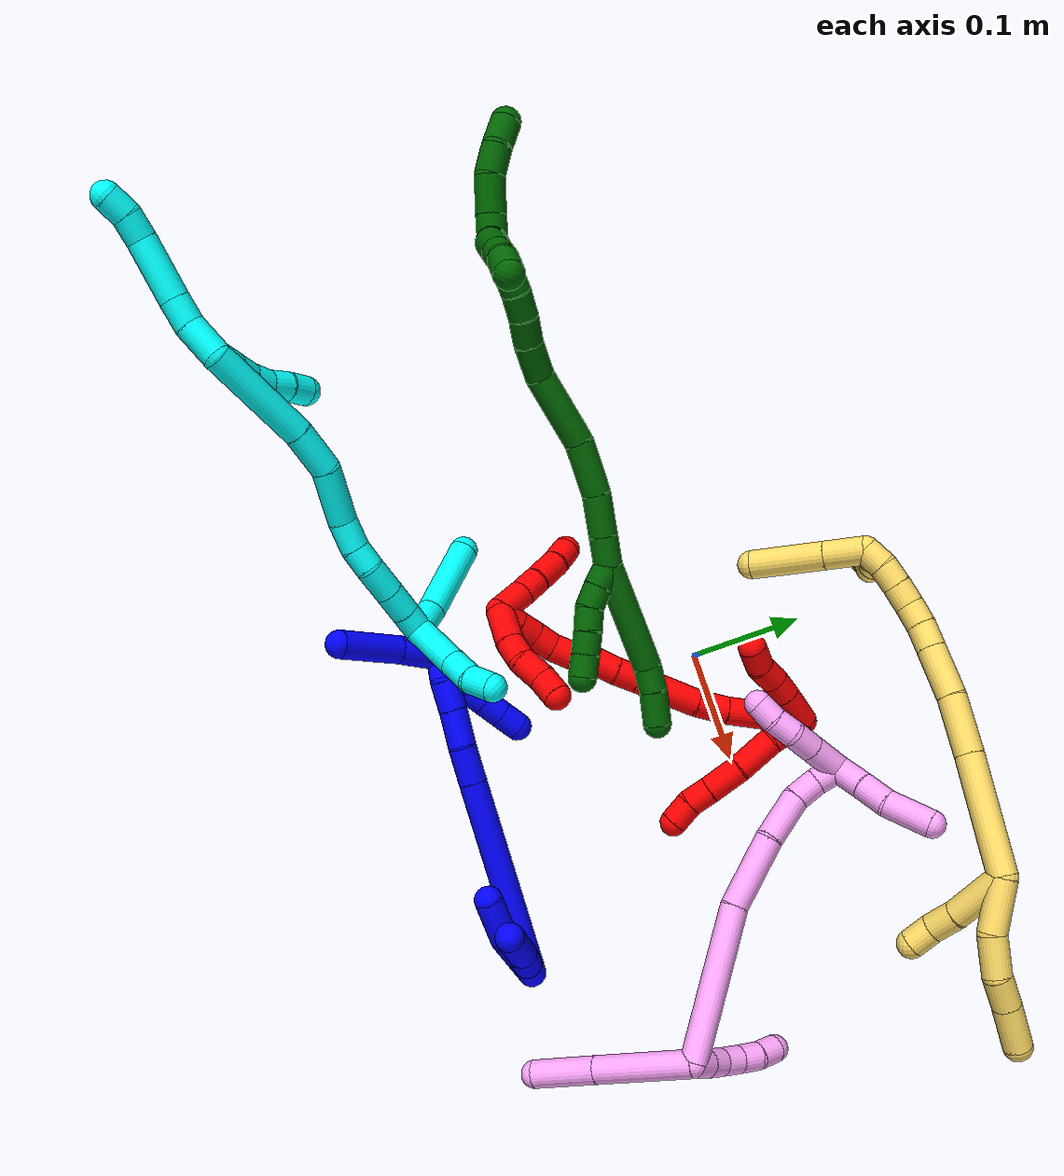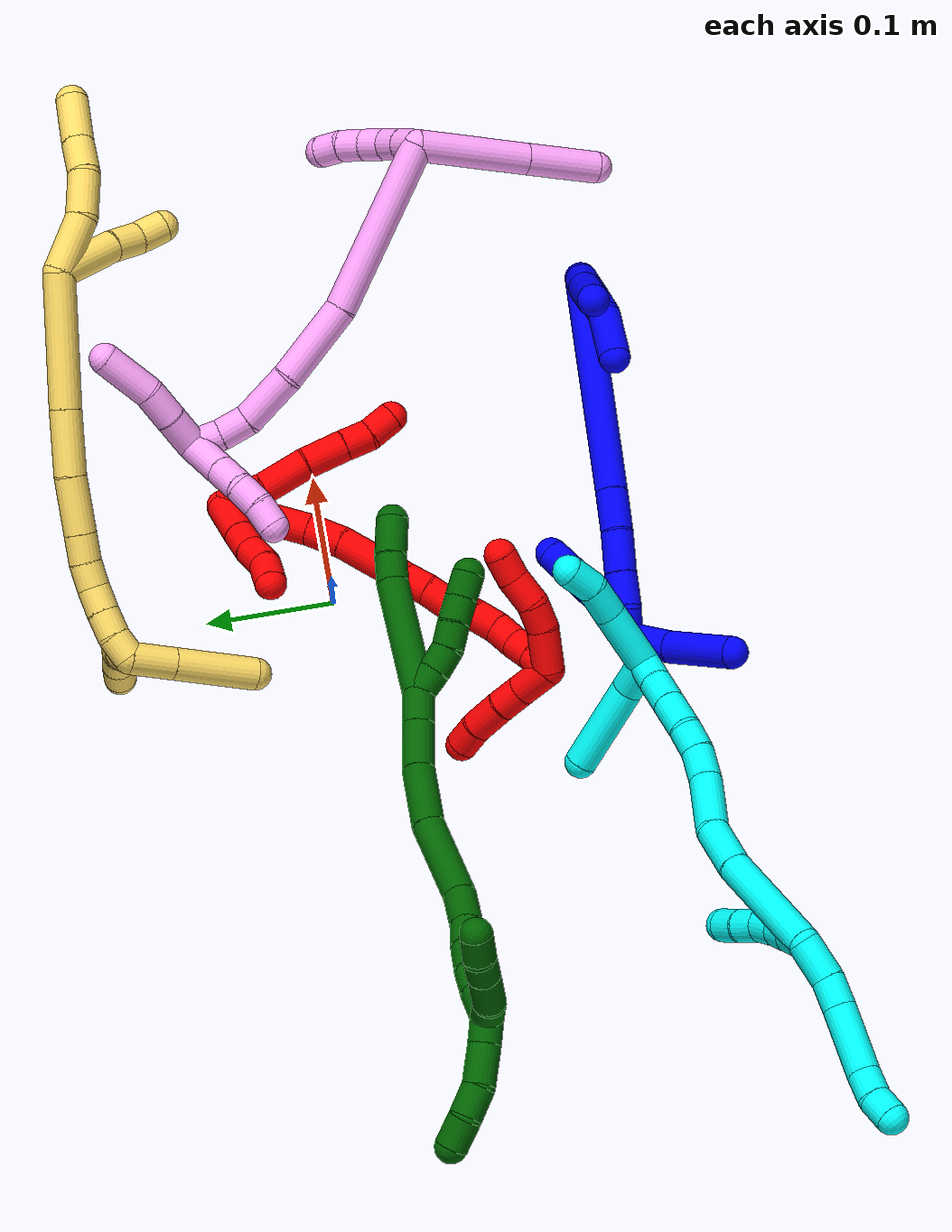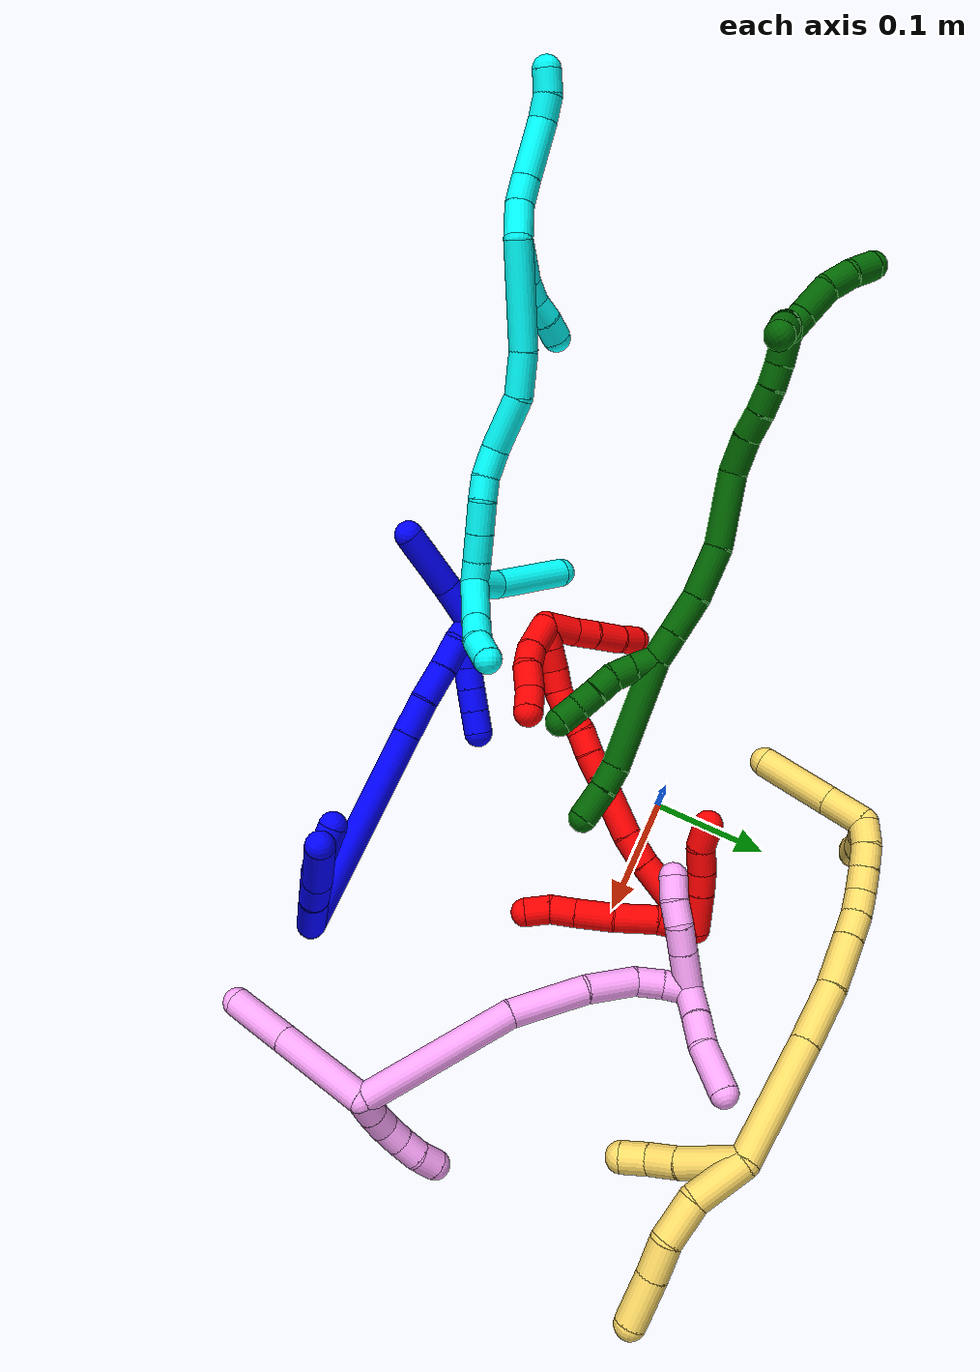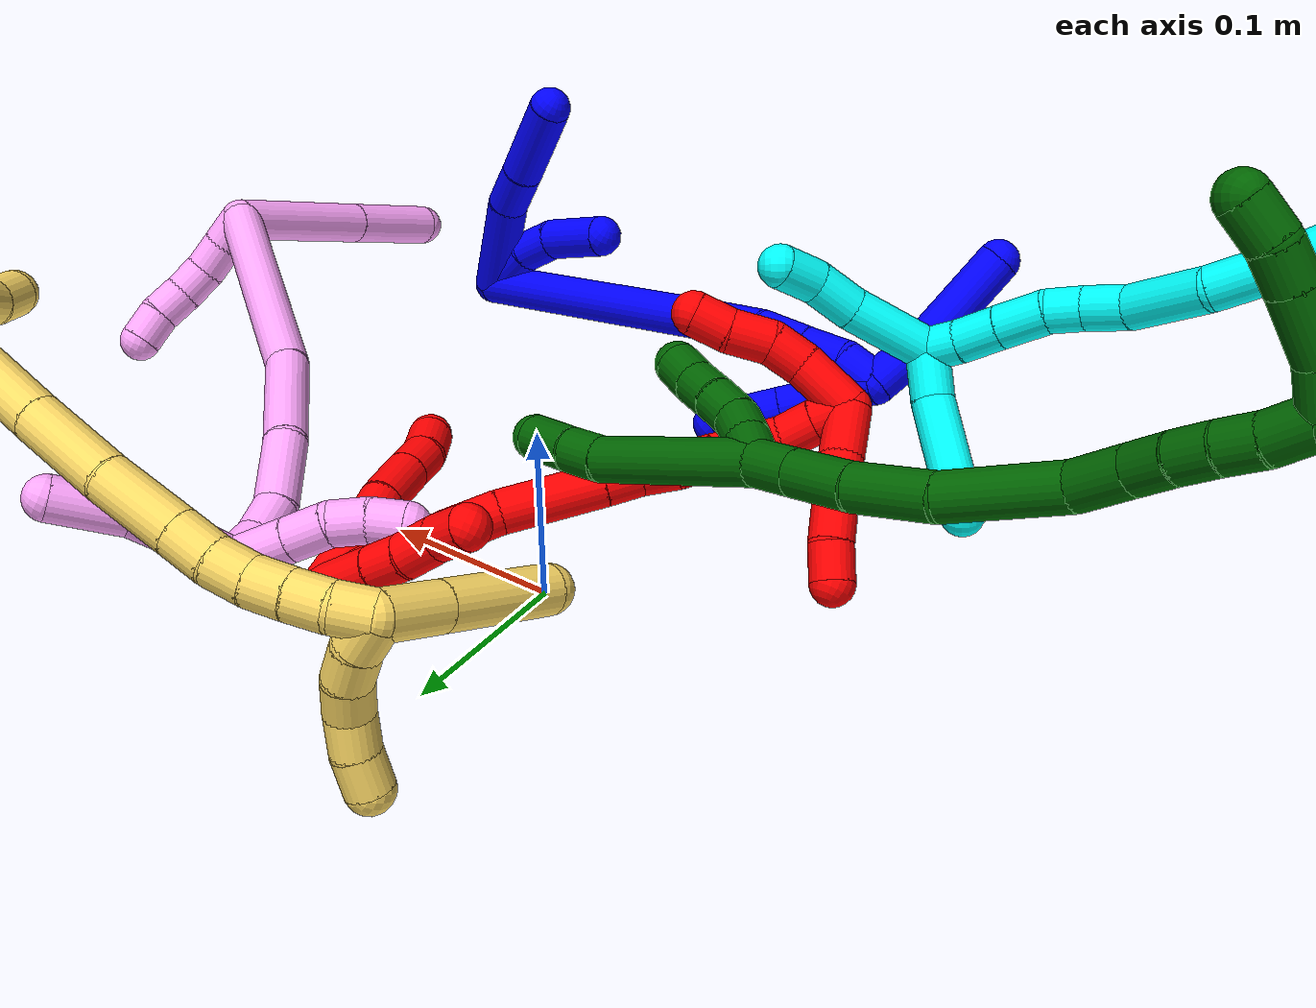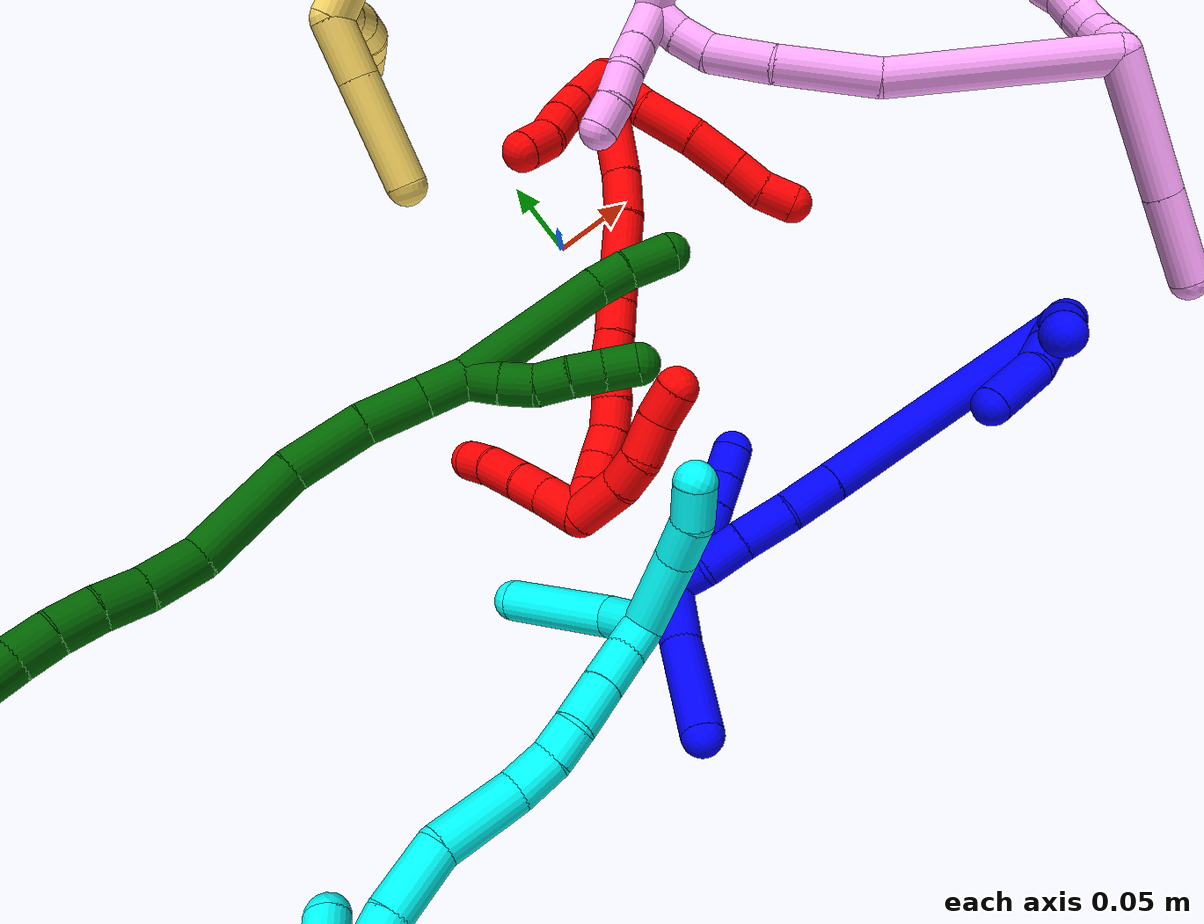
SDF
<sdf version="1.7">
 <world name="default">
  <plugin name="TubeGeneratorPlugin" filename="libtube_generator_plugin.so"/>
  <model name="photoneo_s_sensor">
   <static>1</static>
   <pose>0 0 2 1.57079 1.57079 3.14159</pose>
   <link name="link">
    <inertial><mass>0.1</mass></inertial>
    <sensor name="sensor" type="depth">
     <update_rate>30</update_rate>
     <camera>
      <horizontal_fov>1.22</horizontal_fov>
      <image><width>1920</width><height>1200</height><format>B8G8R8</format></image>
      <clip><near>0.1</near><far>4</far></clip>
      <depth_camera><output>points</output></depth_camera>
     </camera>
     <plugin name="camera_plugin" filename="libgazebo_ros_depth_camera.so">
      <baseline>0.2</baseline>
      <alwaysOn>1</alwaysOn>
      <updateRate>0.0</updateRate>
      <cameraName>camera_ir</cameraName>
      <imageTopicName>/camera/color/image_raw</imageTopicName>
      <cameraInfoTopicName>/camera/color/camera_info</cameraInfoTopicName>
      <depthImageTopicName>/camera/depth/image_raw</depthImageTopicName>
      <depthImageCameraInfoTopicName>/camera/depth/camera_info</depthImageCameraInfoTopicName>
      <pointCloudTopicName>/camera/depth/points</pointCloudTopicName>
      <frameName>fr_optical</frameName>
      <pointCloudCutoff>0.1</pointCloudCutoff>
      <pointCloudCutoffMax>2.0</pointCloudCutoffMax>
      <distortionK1>0</distortionK1>
      <distortionK2>0</distortionK2>
      <distortionK3>0</distortionK3>
      <distortionT1>0</distortionT1>
      <distortionT2>0</distortionT2>
      <CxPrime>0</CxPrime>
      <Cx>0</Cx>
      <Cy>0</Cy>
      <focalLength>0</focalLength>
      <hackBaseline>0</hackBaseline>
     </plugin>
    </sensor>
   </link>
  </model>
  <gravity>0 0 -9.8</gravity>
  <magnetic_field>6e-06 2.3e-05 -4.2e-05</magnetic_field>
  <atmosphere type="adiabatic"/>
  <physics name="default_physics" default="0" type="ode">
   <max_step_size>0.003</max_step_size>
   <real_time_factor>1</real_time_factor>
   <real_time_update_rate>1000</real_time_update_rate>
   <max_contacts>10000</max_contacts>
   <ode>
    <solver>
     <type>quick</type>
     <iters>100</iters>
     <sor>1.3</sor>
     <use_dynamic_moi_rescaling>0</use_dynamic_moi_rescaling>
    </solver>
    <constraints>
     <contact_max_correcting_vel>0</contact_max_correcting_vel>
     <contact_surface_layer>0.001</contact_surface_layer>
     <cfm>0</cfm>
     <erp>0.2</erp>
    </constraints>
   </ode>
  </physics>
  <scene><ambient>0.4 0.4 0.4 1</ambient><background>0.7 0.7 0.7 1</background><shadows>0</shadows></scene>
  <audio><device>default</device></audio>
  <spherical_coordinates>
   <surface_model>EARTH_WGS84</surface_model>
   <latitude_deg>0</latitude_deg>
   <longitude_deg>0</longitude_deg>
   <elevation>0</elevation>
   <heading_deg>0</heading_deg>
  </spherical_coordinates>
  <model name="bin">
   <static>1</static>
   <link name="bottom">
    <collision name="collision-bottom">
     <pose>0 0 -0.01 0 -0 0</pose>
     <geometry><box><size>0.8 0.6 0.02</size></box></geometry>
     <surface>
      <friction><ode><mu>100</mu><mu2>100</mu2></ode></friction>
      <contact><collide_bitmask>65535</collide_bitmask></contact>
     </surface>
    </collision>
   </link>
   <link name="west_wall">
    <collision name="collision-west_wall">
     <pose>-0.41 0 0.1 0 -0 0</pose>
     <geometry><box><size>0.02 0.6 0.2</size></box></geometry>
     <surface>
      <friction><ode><mu>100</mu><mu2>100</mu2></ode></friction>
      <contact><collide_bitmask>65535</collide_bitmask></contact>
     </surface>
    </collision>
   </link>
   <link name="east_wall">
    <collision name="collision-east_wall">
     <pose>0.41 0 0.1 0 -0 0</pose>
     <geometry><box><size>0.02 0.6 0.2</size></box></geometry>
     <surface>
      <friction><ode><mu>100</mu><mu2>100</mu2></ode></friction>
      <contact><collide_bitmask>65535</collide_bitmask></contact>
     </surface>
    </collision>
   </link>
   <link name="south_wall">
    <collision name="collision-south_wall">
     <pose>0 -0.31 0.1 0 -0 0</pose>
     <geometry><box><size>0.8 0.02 0.2</size></box></geometry>
     <surface>
      <friction><ode><mu>100</mu><mu2>100</mu2></ode></friction>
      <contact><collide_bitmask>65535</collide_bitmask></contact>
     </surface>
    </collision>
   </link>
   <link name="north_wall">
    <collision name="collision-north_wall">
     <pose>0 0.31 0.1 0 -0 0</pose>
     <geometry><box><size>0.8 0.02 0.2</size></box></geometry>
     <surface>
      <friction><ode><mu>100</mu><mu2>100</mu2></ode></friction>
      <contact><collide_bitmask>65535</collide_bitmask></contact>
     </surface>
    </collision>
   </link>
  </model>
  <model name="1">
   <static>0</static>
   <link name="1">
    <collision name="collision-cylinder-e_1_2_8">
     <pose>0.009609 -0.005706 -0.031764 2.96385 0.289403 2.04393</pose>
     <geometry><cylinder><radius>0.0125</radius><length>0.067344</length></cylinder></geometry>
     <surface>
      <friction><ode><mu>1.16</mu><mu2>1.16</mu2><slip1>0</slip1><slip2>0</slip2></ode></friction>
      <contact><ode><kp>1e+06</kp><kd>1</kd><max_vel>0</max_vel><min_depth>0.001</min_depth></ode></contact>
     </surface>
    </collision>
    <visual name="visual-cylinder-e_1_2_8">
     <pose>0.009609 -0.005706 -0.031764 2.96385 0.289403 2.04393</pose>
     <geometry><cylinder><radius>0.0125</radius><length>0.067344</length></cylinder></geometry>
     <material><ambient>0 0 1 1</ambient></material>
    </visual>
    <collision name="collision-cylinder-e_2_8_9">
     <pose>0.020447 -0.013903 -0.077914 2.97014 0.083916 0.908836</pose>
     <geometry><cylinder><radius>0.0125</radius><length>0.029306</length></cylinder></geometry>
     <surface>
      <friction><ode><mu>1.16</mu><mu2>1.16</mu2><slip1>0</slip1><slip2>0</slip2></ode></friction>
      <contact><ode><kp>1e+06</kp><kd>1</kd><max_vel>0</max_vel><min_depth>0.001</min_depth></ode></contact>
     </surface>
    </collision>
    <visual name="visual-cylinder-e_2_8_9">
     <pose>0.020447 -0.013903 -0.077914 2.97014 0.083916 0.908836</pose>
     <geometry><cylinder><radius>0.0125</radius><length>0.029306</length></cylinder></geometry>
     <material><ambient>0 0 1 1</ambient></material>
    </visual>
    <collision name="collision-cylinder-e_3_9_6">
     <pose>0.024711 -0.019417 -0.11863 3.02731 0.114047 1.56876</pose>
     <geometry><cylinder><radius>0.0125</radius><length>0.05335</length></cylinder></geometry>
     <surface>
      <friction><ode><mu>1.16</mu><mu2>1.16</mu2><slip1>0</slip1><slip2>0</slip2></ode></friction>
      <contact><ode><kp>1e+06</kp><kd>1</kd><max_vel>0</max_vel><min_depth>0.001</min_depth></ode></contact>
     </surface>
    </collision>
    <visual name="visual-cylinder-e_3_9_6">
     <pose>0.024711 -0.019417 -0.11863 3.02731 0.114047 1.56876</pose>
     <geometry><cylinder><radius>0.0125</radius><length>0.05335</length></cylinder></geometry>
     <material><ambient>0 0 1 1</ambient></material>
    </visual>
    <collision name="collision-cylinder-e_1_2_10">
     <pose>-0.002754 -0.000758 -0.018035 3.0996 -0.151418 -2.60142</pose>
     <geometry><cylinder><radius>0.0125</radius><length>0.036519</length></cylinder></geometry>
     <surface>
      <friction><ode><mu>1.16</mu><mu2>1.16</mu2><slip1>0</slip1><slip2>0</slip2></ode></friction>
      <contact><ode><kp>1e+06</kp><kd>1</kd><max_vel>0</max_vel><min_depth>0.001</min_depth></ode></contact>
     </surface>
    </collision>
    <visual name="visual-cylinder-e_1_2_10">
     <pose>-0.002754 -0.000758 -0.018035 3.0996 -0.151418 -2.60142</pose>
     <geometry><cylinder><radius>0.0125</radius><length>0.036519</length></cylinder></geometry>
     <material><ambient>0 0 1 1</ambient></material>
    </visual>
    <collision name="collision-cylinder-e_2_10_11">
     <pose>-0.010425 -0.001142 -0.046685 -3.10642 -0.433492 2.9822</pose>
     <geometry><cylinder><radius>0.0125</radius><length>0.023408</length></cylinder></geometry>
     <surface>
      <friction><ode><mu>1.16</mu><mu2>1.16</mu2><slip1>0</slip1><slip2>0</slip2></ode></friction>
      <contact><ode><kp>1e+06</kp><kd>1</kd><max_vel>0</max_vel><min_depth>0.001</min_depth></ode></contact>
     </surface>
    </collision>
    <visual name="visual-cylinder-e_2_10_11">
     <pose>-0.010425 -0.001142 -0.046685 -3.10642 -0.433492 2.9822</pose>
     <geometry><cylinder><radius>0.0125</radius><length>0.023408</length></cylinder></geometry>
     <material><ambient>0 0 1 1</ambient></material>
    </visual>
    <collision name="collision-cylinder-e_3_11_5">
     <pose>-0.027944 -0.004275 -0.072476 2.91457 -0.680265 -2.5183</pose>
     <geometry><cylinder><radius>0.0125</radius><length>0.040072</length></cylinder></geometry>
     <surface>
      <friction><ode><mu>1.16</mu><mu2>1.16</mu2><slip1>0</slip1><slip2>0</slip2></ode></friction>
      <contact><ode><kp>1e+06</kp><kd>1</kd><max_vel>0</max_vel><min_depth>0.001</min_depth></ode></contact>
     </surface>
    </collision>
    <visual name="visual-cylinder-e_3_11_5">
     <pose>-0.027944 -0.004275 -0.072476 2.91457 -0.680265 -2.5183</pose>
     <geometry><cylinder><radius>0.0125</radius><length>0.040072</length></cylinder></geometry>
     <material><ambient>0 0 1 1</ambient></material>
    </visual>
    <collision name="collision-cylinder-e_1_2_12">
     <pose>-0.066679 -0.022113 -0.059428 2.78538 -0.810526 -2.34701</pose>
     <geometry><cylinder><radius>0.0125</radius><length>0.18403</length></cylinder></geometry>
     <surface>
      <friction><ode><mu>1.16</mu><mu2>1.16</mu2><slip1>0</slip1><slip2>0</slip2></ode></friction>
      <contact><ode><kp>1e+06</kp><kd>1</kd><max_vel>0</max_vel><min_depth>0.001</min_depth></ode></contact>
     </surface>
    </collision>
    <visual name="visual-cylinder-e_1_2_12">
     <pose>-0.066679 -0.022113 -0.059428 2.78538 -0.810526 -2.34701</pose>
     <geometry><cylinder><radius>0.0125</radius><length>0.18403</length></cylinder></geometry>
     <material><ambient>0 0 1 1</ambient></material>
    </visual>
    <collision name="collision-cylinder-e_2_12_13">
     <pose>-0.145496 -0.048334 -0.129393 2.76977 -0.820778 -2.32555</pose>
     <geometry><cylinder><radius>0.0125</radius><length>0.033181</length></cylinder></geometry>
     <surface>
      <friction><ode><mu>1.16</mu><mu2>1.16</mu2><slip1>0</slip1><slip2>0</slip2></ode></friction>
      <contact><ode><kp>1e+06</kp><kd>1</kd><max_vel>0</max_vel><min_depth>0.001</min_depth></ode></contact>
     </surface>
    </collision>
    <visual name="visual-cylinder-e_2_12_13">
     <pose>-0.145496 -0.048334 -0.129393 2.76977 -0.820778 -2.32555</pose>
     <geometry><cylinder><radius>0.0125</radius><length>0.033181</length></cylinder></geometry>
     <material><ambient>0 0 1 1</ambient></material>
    </visual>
    <collision name="collision-cylinder-e_3_13_14">
     <pose>-0.171077 -0.056986 -0.148232 2.64093 -0.95732 -2.22593</pose>
     <geometry><cylinder><radius>0.0125</radius><length>0.032881</length></cylinder></geometry>
     <surface>
      <friction><ode><mu>1.16</mu><mu2>1.16</mu2><slip1>0</slip1><slip2>0</slip2></ode></friction>
      <contact><ode><kp>1e+06</kp><kd>1</kd><max_vel>0</max_vel><min_depth>0.001</min_depth></ode></contact>
     </surface>
    </collision>
    <visual name="visual-cylinder-e_3_13_14">
     <pose>-0.171077 -0.056986 -0.148232 2.64093 -0.95732 -2.22593</pose>
     <geometry><cylinder><radius>0.0125</radius><length>0.032881</length></cylinder></geometry>
     <material><ambient>0 0 1 1</ambient></material>
    </visual>
    <collision name="collision-cylinder-e_4_14_15">
     <pose>-0.195733 -0.064568 -0.163388 2.72422 -0.981547 -2.38698</pose>
     <geometry><cylinder><radius>0.0125</radius><length>0.026975</length></cylinder></geometry>
     <surface>
      <friction><ode><mu>1.16</mu><mu2>1.16</mu2><slip1>0</slip1><slip2>0</slip2></ode></friction>
      <contact><ode><kp>1e+06</kp><kd>1</kd><max_vel>0</max_vel><min_depth>0.001</min_depth></ode></contact>
     </surface>
    </collision>
    <visual name="visual-cylinder-e_4_14_15">
     <pose>-0.195733 -0.064568 -0.163388 2.72422 -0.981547 -2.38698</pose>
     <geometry><cylinder><radius>0.0125</radius><length>0.026975</length></cylinder></geometry>
     <material><ambient>0 0 1 1</ambient></material>
    </visual>
    <collision name="collision-cylinder-e_5_15_1">
     <pose>-0.217487 -0.071018 -0.173194 2.28431 -1.16625 -1.92989</pose>
     <geometry><cylinder><radius>0.0125</radius><length>0.022933</length></cylinder></geometry>
     <surface>
      <friction><ode><mu>1.16</mu><mu2>1.16</mu2><slip1>0</slip1><slip2>0</slip2></ode></friction>
      <contact><ode><kp>1e+06</kp><kd>1</kd><max_vel>0</max_vel><min_depth>0.001</min_depth></ode></contact>
     </surface>
    </collision>
    <visual name="visual-cylinder-e_5_15_1">
     <pose>-0.217487 -0.071018 -0.173194 2.28431 -1.16625 -1.92989</pose>
     <geometry><cylinder><radius>0.0125</radius><length>0.022933</length></cylinder></geometry>
     <material><ambient>0 0 1 1</ambient></material>
    </visual>
    <collision name="collision-cylinder-e_1_1_16">
     <pose>-0.231515 -0.061627 -0.191334 -2.44111 -0.173785 0.468189</pose>
     <geometry><cylinder><radius>0.0125</radius><length>0.040334</length></cylinder></geometry>
     <surface>
      <friction><ode><mu>1.16</mu><mu2>1.16</mu2><slip1>0</slip1><slip2>0</slip2></ode></friction>
      <contact><ode><kp>1e+06</kp><kd>1</kd><max_vel>0</max_vel><min_depth>0.001</min_depth></ode></contact>
     </surface>
    </collision>
    <visual name="visual-cylinder-e_1_1_16">
     <pose>-0.231515 -0.061627 -0.191334 -2.44111 -0.173785 0.468189</pose>
     <geometry><cylinder><radius>0.0125</radius><length>0.040334</length></cylinder></geometry>
     <material><ambient>0 0 1 1</ambient></material>
    </visual>
    <collision name="collision-cylinder-e_2_16_4">
     <pose>-0.235929 -0.030977 -0.230409 -2.49997 -0.031068 0.093437</pose>
     <geometry><cylinder><radius>0.0125</radius><length>0.059666</length></cylinder></geometry>
     <surface>
      <friction><ode><mu>1.16</mu><mu2>1.16</mu2><slip1>0</slip1><slip2>0</slip2></ode></friction>
      <contact><ode><kp>1e+06</kp><kd>1</kd><max_vel>0</max_vel><min_depth>0.001</min_depth></ode></contact>
     </surface>
    </collision>
    <visual name="visual-cylinder-e_2_16_4">
     <pose>-0.235929 -0.030977 -0.230409 -2.49997 -0.031068 0.093437</pose>
     <geometry><cylinder><radius>0.0125</radius><length>0.059666</length></cylinder></geometry>
     <material><ambient>0 0 1 1</ambient></material>
    </visual>
    <collision name="collision-cylinder-e_1_1_17">
     <pose>-0.222341 -0.074451 -0.167922 0.002482 0.604921 0.000775</pose>
     <geometry><cylinder><radius>0.0125</radius><length>0.02</length></cylinder></geometry>
     <surface>
      <friction><ode><mu>1.16</mu><mu2>1.16</mu2><slip1>0</slip1><slip2>0</slip2></ode></friction>
      <contact><ode><kp>1e+06</kp><kd>1</kd><max_vel>0</max_vel><min_depth>0.001</min_depth></ode></contact>
     </surface>
    </collision>
    <visual name="visual-cylinder-e_1_1_17">
     <pose>-0.222341 -0.074451 -0.167922 0.002482 0.604921 0.000775</pose>
     <geometry><cylinder><radius>0.0125</radius><length>0.02</length></cylinder></geometry>
     <material><ambient>0 0 1 1</ambient></material>
    </visual>
    <collision name="collision-cylinder-e_2_17_18">
     <pose>-0.212096 -0.076004 -0.150929 0.173032 0.473308 0.041829</pose>
     <geometry><cylinder><radius>0.0125</radius><length>0.02</length></cylinder></geometry>
     <surface>
      <friction><ode><mu>1.16</mu><mu2>1.16</mu2><slip1>0</slip1><slip2>0</slip2></ode></friction>
      <contact><ode><kp>1e+06</kp><kd>1</kd><max_vel>0</max_vel><min_depth>0.001</min_depth></ode></contact>
     </surface>
    </collision>
    <visual name="visual-cylinder-e_2_17_18">
     <pose>-0.212096 -0.076004 -0.150929 0.173032 0.473308 0.041829</pose>
     <geometry><cylinder><radius>0.0125</radius><length>0.02</length></cylinder></geometry>
     <material><ambient>0 0 1 1</ambient></material>
    </visual>
    <collision name="collision-cylinder-e_3_18_19">
     <pose>-0.201584 -0.081133 -0.134976 0.464089 0.637662 0.155687</pose>
     <geometry><cylinder><radius>0.0125</radius><length>0.02</length></cylinder></geometry>
     <surface>
      <friction><ode><mu>1.16</mu><mu2>1.16</mu2><slip1>0</slip1><slip2>0</slip2></ode></friction>
      <contact><ode><kp>1e+06</kp><kd>1</kd><max_vel>0</max_vel><min_depth>0.001</min_depth></ode></contact>
     </surface>
    </collision>
    <visual name="visual-cylinder-e_3_18_19">
     <pose>-0.201584 -0.081133 -0.134976 0.464089 0.637662 0.155687</pose>
     <geometry><cylinder><radius>0.0125</radius><length>0.02</length></cylinder></geometry>
     <material><ambient>0 0 1 1</ambient></material>
    </visual>
    <collision name="collision-cylinder-e_4_19_20">
     <pose>-0.189665 -0.088298 -0.120603 0.460831 0.639215 0.154961</pose>
     <geometry><cylinder><radius>0.0125</radius><length>0.02</length></cylinder></geometry>
     <surface>
      <friction><ode><mu>1.16</mu><mu2>1.16</mu2><slip1>0</slip1><slip2>0</slip2></ode></friction>
      <contact><ode><kp>1e+06</kp><kd>1</kd><max_vel>0</max_vel><min_depth>0.001</min_depth></ode></contact>
     </surface>
    </collision>
    <visual name="visual-cylinder-e_4_19_20">
     <pose>-0.189665 -0.088298 -0.120603 0.460831 0.639215 0.154961</pose>
     <geometry><cylinder><radius>0.0125</radius><length>0.02</length></cylinder></geometry>
     <material><ambient>0 0 1 1</ambient></material>
    </visual>
    <collision name="collision-cylinder-e_5_20_3">
     <pose>-0.17768 -0.095516 -0.106312 0.474491 0.645966 0.16151</pose>
     <geometry><cylinder><radius>0.0125</radius><length>0.02</length></cylinder></geometry>
     <surface>
      <friction><ode><mu>1.16</mu><mu2>1.16</mu2><slip1>0</slip1><slip2>0</slip2></ode></friction>
      <contact><ode><kp>1e+06</kp><kd>1</kd><max_vel>0</max_vel><min_depth>0.001</min_depth></ode></contact>
     </surface>
    </collision>
    <visual name="visual-cylinder-e_5_20_3">
     <pose>-0.17768 -0.095516 -0.106312 0.474491 0.645966 0.16151</pose>
     <geometry><cylinder><radius>0.0125</radius><length>0.02</length></cylinder></geometry>
     <material><ambient>0 0 1 1</ambient></material>
    </visual>
    <collision name="collision-sphere-3">
     <pose>-0.17166 -0.099164 -0.099208 0 -0 0</pose>
     <geometry><sphere><radius>0.0125</radius></sphere></geometry>
     <surface>
      <friction><ode><mu>1.16</mu><mu2>1.16</mu2><slip1>0</slip1><slip2>0</slip2></ode></friction>
      <contact><ode><kp>1e+06</kp><kd>1</kd><max_vel>0</max_vel><min_depth>0.001</min_depth></ode></contact>
     </surface>
    </collision>
    <visual name="visual-sphere-3">
     <pose>-0.17166 -0.099164 -0.099208 0 -0 0</pose>
     <geometry><sphere><radius>0.0125</radius></sphere></geometry>
     <material><ambient>0 0 1 1</ambient></material>
    </visual>
    <collision name="collision-sphere-20">
     <pose>-0.1837 -0.091867 -0.113415 0 -0 0</pose>
     <geometry><sphere><radius>0.0125</radius></sphere></geometry>
     <surface>
      <friction><ode><mu>1.16</mu><mu2>1.16</mu2><slip1>0</slip1><slip2>0</slip2></ode></friction>
      <contact><ode><kp>1e+06</kp><kd>1</kd><max_vel>0</max_vel><min_depth>0.001</min_depth></ode></contact>
     </surface>
    </collision>
    <visual name="visual-sphere-20">
     <pose>-0.1837 -0.091867 -0.113415 0 -0 0</pose>
     <geometry><sphere><radius>0.0125</radius></sphere></geometry>
     <material><ambient>0 0 1 1</ambient></material>
    </visual>
    <collision name="collision-sphere-19">
     <pose>-0.195631 -0.084729 -0.127791 0 -0 0</pose>
     <geometry><sphere><radius>0.0125</radius></sphere></geometry>
     <surface>
      <friction><ode><mu>1.16</mu><mu2>1.16</mu2><slip1>0</slip1><slip2>0</slip2></ode></friction>
      <contact><ode><kp>1e+06</kp><kd>1</kd><max_vel>0</max_vel><min_depth>0.001</min_depth></ode></contact>
     </surface>
    </collision>
    <visual name="visual-sphere-19">
     <pose>-0.195631 -0.084729 -0.127791 0 -0 0</pose>
     <geometry><sphere><radius>0.0125</radius></sphere></geometry>
     <material><ambient>0 0 1 1</ambient></material>
    </visual>
    <collision name="collision-sphere-11">
     <pose>-0.015341 -0.000769 -0.0573 0 -0 0</pose>
     <geometry><sphere><radius>0.0125</radius></sphere></geometry>
     <surface>
      <friction><ode><mu>1.16</mu><mu2>1.16</mu2><slip1>0</slip1><slip2>0</slip2></ode></friction>
      <contact><ode><kp>1e+06</kp><kd>1</kd><max_vel>0</max_vel><min_depth>0.001</min_depth></ode></contact>
     </surface>
    </collision>
    <visual name="visual-sphere-11">
     <pose>-0.015341 -0.000769 -0.0573 0 -0 0</pose>
     <geometry><sphere><radius>0.0125</radius></sphere></geometry>
     <material><ambient>0 0 1 1</ambient></material>
    </visual>
    <collision name="collision-sphere-10">
     <pose>-0.005509 -0.001516 -0.03607 0 -0 0</pose>
     <geometry><sphere><radius>0.0125</radius></sphere></geometry>
     <surface>
      <friction><ode><mu>1.16</mu><mu2>1.16</mu2><slip1>0</slip1><slip2>0</slip2></ode></friction>
      <contact><ode><kp>1e+06</kp><kd>1</kd><max_vel>0</max_vel><min_depth>0.001</min_depth></ode></contact>
     </surface>
    </collision>
    <visual name="visual-sphere-10">
     <pose>-0.005509 -0.001516 -0.03607 0 -0 0</pose>
     <geometry><sphere><radius>0.0125</radius></sphere></geometry>
     <material><ambient>0 0 1 1</ambient></material>
    </visual>
    <collision name="collision-sphere-6">
     <pose>0.027746 -0.022439 -0.144959 0 -0 0</pose>
     <geometry><sphere><radius>0.0125</radius></sphere></geometry>
     <surface>
      <friction><ode><mu>1.16</mu><mu2>1.16</mu2><slip1>0</slip1><slip2>0</slip2></ode></friction>
      <contact><ode><kp>1e+06</kp><kd>1</kd><max_vel>0</max_vel><min_depth>0.001</min_depth></ode></contact>
     </surface>
    </collision>
    <visual name="visual-sphere-6">
     <pose>0.027746 -0.022439 -0.144959 0 -0 0</pose>
     <geometry><sphere><radius>0.0125</radius></sphere></geometry>
     <material><ambient>0 0 1 1</ambient></material>
    </visual>
    <collision name="collision-sphere-9">
     <pose>0.021675 -0.016395 -0.092301 0 -0 0</pose>
     <geometry><sphere><radius>0.0125</radius></sphere></geometry>
     <surface>
      <friction><ode><mu>1.16</mu><mu2>1.16</mu2><slip1>0</slip1><slip2>0</slip2></ode></friction>
      <contact><ode><kp>1e+06</kp><kd>1</kd><max_vel>0</max_vel><min_depth>0.001</min_depth></ode></contact>
     </surface>
    </collision>
    <visual name="visual-sphere-9">
     <pose>0.021675 -0.016395 -0.092301 0 -0 0</pose>
     <geometry><sphere><radius>0.0125</radius></sphere></geometry>
     <material><ambient>0 0 1 1</ambient></material>
    </visual>
    <collision name="collision-sphere-2">
     <geometry><sphere><radius>0.0125</radius></sphere></geometry>
     <surface>
      <friction><ode><mu>1.16</mu><mu2>1.16</mu2><slip1>0</slip1><slip2>0</slip2></ode></friction>
      <contact><ode><kp>1e+06</kp><kd>1</kd><max_vel>0</max_vel><min_depth>0.001</min_depth></ode></contact>
     </surface>
    </collision>
    <visual name="visual-sphere-2">
     <geometry><sphere><radius>0.0125</radius></sphere></geometry>
     <material><ambient>0 0 1 1</ambient></material>
    </visual>
    <collision name="collision-sphere-8">
     <pose>0.019219 -0.011412 -0.063527 0 -0 0</pose>
     <geometry><sphere><radius>0.0125</radius></sphere></geometry>
     <surface>
      <friction><ode><mu>1.16</mu><mu2>1.16</mu2><slip1>0</slip1><slip2>0</slip2></ode></friction>
      <contact><ode><kp>1e+06</kp><kd>1</kd><max_vel>0</max_vel><min_depth>0.001</min_depth></ode></contact>
     </surface>
    </collision>
    <visual name="visual-sphere-8">
     <pose>0.019219 -0.011412 -0.063527 0 -0 0</pose>
     <geometry><sphere><radius>0.0125</radius></sphere></geometry>
     <material><ambient>0 0 1 1</ambient></material>
    </visual>
    <collision name="collision-sphere-5">
     <pose>-0.040547 -0.00778 -0.087653 0 -0 0</pose>
     <geometry><sphere><radius>0.0125</radius></sphere></geometry>
     <surface>
      <friction><ode><mu>1.16</mu><mu2>1.16</mu2><slip1>0</slip1><slip2>0</slip2></ode></friction>
      <contact><ode><kp>1e+06</kp><kd>1</kd><max_vel>0</max_vel><min_depth>0.001</min_depth></ode></contact>
     </surface>
    </collision>
    <visual name="visual-sphere-5">
     <pose>-0.040547 -0.00778 -0.087653 0 -0 0</pose>
     <geometry><sphere><radius>0.0125</radius></sphere></geometry>
     <material><ambient>0 0 1 1</ambient></material>
    </visual>
    <collision name="collision-sphere-12">
     <pose>-0.133357 -0.044225 -0.118857 0 -0 0</pose>
     <geometry><sphere><radius>0.0125</radius></sphere></geometry>
     <surface>
      <friction><ode><mu>1.16</mu><mu2>1.16</mu2><slip1>0</slip1><slip2>0</slip2></ode></friction>
      <contact><ode><kp>1e+06</kp><kd>1</kd><max_vel>0</max_vel><min_depth>0.001</min_depth></ode></contact>
     </surface>
    </collision>
    <visual name="visual-sphere-12">
     <pose>-0.133357 -0.044225 -0.118857 0 -0 0</pose>
     <geometry><sphere><radius>0.0125</radius></sphere></geometry>
     <material><ambient>0 0 1 1</ambient></material>
    </visual>
    <collision name="collision-sphere-13">
     <pose>-0.157635 -0.052443 -0.139929 0 -0 0</pose>
     <geometry><sphere><radius>0.0125</radius></sphere></geometry>
     <surface>
      <friction><ode><mu>1.16</mu><mu2>1.16</mu2><slip1>0</slip1><slip2>0</slip2></ode></friction>
      <contact><ode><kp>1e+06</kp><kd>1</kd><max_vel>0</max_vel><min_depth>0.001</min_depth></ode></contact>
     </surface>
    </collision>
    <visual name="visual-sphere-13">
     <pose>-0.157635 -0.052443 -0.139929 0 -0 0</pose>
     <geometry><sphere><radius>0.0125</radius></sphere></geometry>
     <material><ambient>0 0 1 1</ambient></material>
    </visual>
    <collision name="collision-sphere-14">
     <pose>-0.18452 -0.061529 -0.156536 0 -0 0</pose>
     <geometry><sphere><radius>0.0125</radius></sphere></geometry>
     <surface>
      <friction><ode><mu>1.16</mu><mu2>1.16</mu2><slip1>0</slip1><slip2>0</slip2></ode></friction>
      <contact><ode><kp>1e+06</kp><kd>1</kd><max_vel>0</max_vel><min_depth>0.001</min_depth></ode></contact>
     </surface>
    </collision>
    <visual name="visual-sphere-14">
     <pose>-0.18452 -0.061529 -0.156536 0 -0 0</pose>
     <geometry><sphere><radius>0.0125</radius></sphere></geometry>
     <material><ambient>0 0 1 1</ambient></material>
    </visual>
    <collision name="collision-sphere-15">
     <pose>-0.206946 -0.067606 -0.17024 0 -0 0</pose>
     <geometry><sphere><radius>0.0125</radius></sphere></geometry>
     <surface>
      <friction><ode><mu>1.16</mu><mu2>1.16</mu2><slip1>0</slip1><slip2>0</slip2></ode></friction>
      <contact><ode><kp>1e+06</kp><kd>1</kd><max_vel>0</max_vel><min_depth>0.001</min_depth></ode></contact>
     </surface>
    </collision>
    <visual name="visual-sphere-15">
     <pose>-0.206946 -0.067606 -0.17024 0 -0 0</pose>
     <geometry><sphere><radius>0.0125</radius></sphere></geometry>
     <material><ambient>0 0 1 1</ambient></material>
    </visual>
    <collision name="collision-sphere-1">
     <pose>-0.228028 -0.074431 -0.176148 0 -0 0</pose>
     <geometry><sphere><radius>0.0125</radius></sphere></geometry>
     <surface>
      <friction><ode><mu>1.16</mu><mu2>1.16</mu2><slip1>0</slip1><slip2>0</slip2></ode></friction>
      <contact><ode><kp>1e+06</kp><kd>1</kd><max_vel>0</max_vel><min_depth>0.001</min_depth></ode></contact>
     </surface>
    </collision>
    <visual name="visual-sphere-1">
     <pose>-0.228028 -0.074431 -0.176148 0 -0 0</pose>
     <geometry><sphere><radius>0.0125</radius></sphere></geometry>
     <material><ambient>0 0 1 1</ambient></material>
    </visual>
    <collision name="collision-sphere-18">
     <pose>-0.207537 -0.077536 -0.142161 0 -0 0</pose>
     <geometry><sphere><radius>0.0125</radius></sphere></geometry>
     <surface>
      <friction><ode><mu>1.16</mu><mu2>1.16</mu2><slip1>0</slip1><slip2>0</slip2></ode></friction>
      <contact><ode><kp>1e+06</kp><kd>1</kd><max_vel>0</max_vel><min_depth>0.001</min_depth></ode></contact>
     </surface>
    </collision>
    <visual name="visual-sphere-18">
     <pose>-0.207537 -0.077536 -0.142161 0 -0 0</pose>
     <geometry><sphere><radius>0.0125</radius></sphere></geometry>
     <material><ambient>0 0 1 1</ambient></material>
    </visual>
    <collision name="collision-sphere-16">
     <pose>-0.235002 -0.048824 -0.20652 0 -0 0</pose>
     <geometry><sphere><radius>0.0125</radius></sphere></geometry>
     <surface>
      <friction><ode><mu>1.16</mu><mu2>1.16</mu2><slip1>0</slip1><slip2>0</slip2></ode></friction>
      <contact><ode><kp>1e+06</kp><kd>1</kd><max_vel>0</max_vel><min_depth>0.001</min_depth></ode></contact>
     </surface>
    </collision>
    <visual name="visual-sphere-16">
     <pose>-0.235002 -0.048824 -0.20652 0 -0 0</pose>
     <geometry><sphere><radius>0.0125</radius></sphere></geometry>
     <material><ambient>0 0 1 1</ambient></material>
    </visual>
    <collision name="collision-sphere-4">
     <pose>-0.236856 -0.013131 -0.254297 0 -0 0</pose>
     <geometry><sphere><radius>0.0125</radius></sphere></geometry>
     <surface>
      <friction><ode><mu>1.16</mu><mu2>1.16</mu2><slip1>0</slip1><slip2>0</slip2></ode></friction>
      <contact><ode><kp>1e+06</kp><kd>1</kd><max_vel>0</max_vel><min_depth>0.001</min_depth></ode></contact>
     </surface>
    </collision>
    <visual name="visual-sphere-4">
     <pose>-0.236856 -0.013131 -0.254297 0 -0 0</pose>
     <geometry><sphere><radius>0.0125</radius></sphere></geometry>
     <material><ambient>0 0 1 1</ambient></material>
    </visual>
    <collision name="collision-sphere-17">
     <pose>-0.216654 -0.074472 -0.159697 0 -0 0</pose>
     <geometry><sphere><radius>0.0125</radius></sphere></geometry>
     <surface>
      <friction><ode><mu>1.16</mu><mu2>1.16</mu2><slip1>0</slip1><slip2>0</slip2></ode></friction>
      <contact><ode><kp>1e+06</kp><kd>1</kd><max_vel>0</max_vel><min_depth>0.001</min_depth></ode></contact>
     </surface>
    </collision>
    <visual name="visual-sphere-17">
     <pose>-0.216654 -0.074472 -0.159697 0 -0 0</pose>
     <geometry><sphere><radius>0.0125</radius></sphere></geometry>
     <material><ambient>0 0 1 1</ambient></material>
    </visual>
    <inertial>
     <pose>-0.100498 -0.03415 -0.105293 0 -0 0</pose>
     <mass>0.75</mass>
     <inertia>
      <ixx>-0.000487</ixx>
      <ixy>0</ixy>
      <ixz>0</ixz>
      <iyy>0.000234</iyy>
      <iyz>0</iyz>
      <izz>0.000478</izz>
     </inertia>
    </inertial>
   </link>
   <pose>0.221035 -0.232847 0.0115 -3.06304 -0.556092 0.146145</pose>
  </model>
  <model name="2">
   <static>0</static>
   <link name="2">
    <collision name="collision-cylinder-e_1_2_8">
     <pose>0.004506 -0.007192 0.015294 0.439599 0.260555 0.058525</pose>
     <geometry><cylinder><radius>0.0125</radius><length>0.034982</length></cylinder></geometry>
     <surface>
      <friction><ode><mu>1.16</mu><mu2>1.16</mu2><slip1>0</slip1><slip2>0</slip2></ode></friction>
      <contact><ode><kp>1e+06</kp><kd>1</kd><max_vel>0</max_vel><min_depth>0.001</min_depth></ode></contact>
     </surface>
    </collision>
    <visual name="visual-cylinder-e_1_2_8">
     <pose>0.004506 -0.007192 0.015294 0.439599 0.260555 0.058525</pose>
     <geometry><cylinder><radius>0.0125</radius><length>0.034982</length></cylinder></geometry>
     <material><ambient>1 0 0 1</ambient></material>
    </visual>
    <collision name="collision-cylinder-e_2_8_9">
     <pose>0.017592 -0.023187 0.044802 0.554452 0.474136 0.137287</pose>
     <geometry><cylinder><radius>0.0125</radius><length>0.037584</length></cylinder></geometry>
     <surface>
      <friction><ode><mu>1.16</mu><mu2>1.16</mu2><slip1>0</slip1><slip2>0</slip2></ode></friction>
      <contact><ode><kp>1e+06</kp><kd>1</kd><max_vel>0</max_vel><min_depth>0.001</min_depth></ode></contact>
     </surface>
    </collision>
    <visual name="visual-cylinder-e_2_8_9">
     <pose>0.017592 -0.023187 0.044802 0.554452 0.474136 0.137287</pose>
     <geometry><cylinder><radius>0.0125</radius><length>0.037584</length></cylinder></geometry>
     <material><ambient>1 0 0 1</ambient></material>
    </visual>
    <collision name="collision-cylinder-e_3_9_10">
     <pose>0.032942 -0.041651 0.070695 0.691152 0.420047 0.15319</pose>
     <geometry><cylinder><radius>0.0125</radius><length>0.033203</length></cylinder></geometry>
     <surface>
      <friction><ode><mu>1.16</mu><mu2>1.16</mu2><slip1>0</slip1><slip2>0</slip2></ode></friction>
      <contact><ode><kp>1e+06</kp><kd>1</kd><max_vel>0</max_vel><min_depth>0.001</min_depth></ode></contact>
     </surface>
    </collision>
    <visual name="visual-cylinder-e_3_9_10">
     <pose>0.032942 -0.041651 0.070695 0.691152 0.420047 0.15319</pose>
     <geometry><cylinder><radius>0.0125</radius><length>0.033203</length></cylinder></geometry>
     <material><ambient>1 0 0 1</ambient></material>
    </visual>
    <collision name="collision-cylinder-e_4_10_11">
     <pose>0.043875 -0.057934 0.090061 0.711015 0.389469 0.146198</pose>
     <geometry><cylinder><radius>0.0125</radius><length>0.02193</length></cylinder></geometry>
     <surface>
      <friction><ode><mu>1.16</mu><mu2>1.16</mu2><slip1>0</slip1><slip2>0</slip2></ode></friction>
      <contact><ode><kp>1e+06</kp><kd>1</kd><max_vel>0</max_vel><min_depth>0.001</min_depth></ode></contact>
     </surface>
    </collision>
    <visual name="visual-cylinder-e_4_10_11">
     <pose>0.043875 -0.057934 0.090061 0.711015 0.389469 0.146198</pose>
     <geometry><cylinder><radius>0.0125</radius><length>0.02193</length></cylinder></geometry>
     <material><ambient>1 0 0 1</ambient></material>
    </visual>
    <collision name="collision-cylinder-e_5_11_6">
     <pose>0.054752 -0.069593 0.105088 0.601581 0.646045 0.206937</pose>
     <geometry><cylinder><radius>0.0125</radius><length>0.022301</length></cylinder></geometry>
     <surface>
      <friction><ode><mu>1.16</mu><mu2>1.16</mu2><slip1>0</slip1><slip2>0</slip2></ode></friction>
      <contact><ode><kp>1e+06</kp><kd>1</kd><max_vel>0</max_vel><min_depth>0.001</min_depth></ode></contact>
     </surface>
    </collision>
    <visual name="visual-cylinder-e_5_11_6">
     <pose>0.054752 -0.069593 0.105088 0.601581 0.646045 0.206937</pose>
     <geometry><cylinder><radius>0.0125</radius><length>0.022301</length></cylinder></geometry>
     <material><ambient>1 0 0 1</ambient></material>
    </visual>
    <collision name="collision-cylinder-e_1_2_12">
     <pose>-0.015446 0.000532 0.008745 -0.060721 -1.05486 0.035375</pose>
     <geometry><cylinder><radius>0.0125</radius><length>0.035515</length></cylinder></geometry>
     <surface>
      <friction><ode><mu>1.16</mu><mu2>1.16</mu2><slip1>0</slip1><slip2>0</slip2></ode></friction>
      <contact><ode><kp>1e+06</kp><kd>1</kd><max_vel>0</max_vel><min_depth>0.001</min_depth></ode></contact>
     </surface>
    </collision>
    <visual name="visual-cylinder-e_1_2_12">
     <pose>-0.015446 0.000532 0.008745 -0.060721 -1.05486 0.035375</pose>
     <geometry><cylinder><radius>0.0125</radius><length>0.035515</length></cylinder></geometry>
     <material><ambient>1 0 0 1</ambient></material>
    </visual>
    <collision name="collision-cylinder-e_2_12_13">
     <pose>-0.039542 0.00094 0.022642 0.023931 -1.03336 -0.013597</pose>
     <geometry><cylinder><radius>0.0125</radius><length>0.020137</length></cylinder></geometry>
     <surface>
      <friction><ode><mu>1.16</mu><mu2>1.16</mu2><slip1>0</slip1><slip2>0</slip2></ode></friction>
      <contact><ode><kp>1e+06</kp><kd>1</kd><max_vel>0</max_vel><min_depth>0.001</min_depth></ode></contact>
     </surface>
    </collision>
    <visual name="visual-cylinder-e_2_12_13">
     <pose>-0.039542 0.00094 0.022642 0.023931 -1.03336 -0.013597</pose>
     <geometry><cylinder><radius>0.0125</radius><length>0.020137</length></cylinder></geometry>
     <material><ambient>1 0 0 1</ambient></material>
    </visual>
    <collision name="collision-cylinder-e_3_13_14">
     <pose>-0.056657 0.000551 0.034641 0.038786 -0.890511 -0.018511</pose>
     <geometry><cylinder><radius>0.0125</radius><length>0.021782</length></cylinder></geometry>
     <surface>
      <friction><ode><mu>1.16</mu><mu2>1.16</mu2><slip1>0</slip1><slip2>0</slip2></ode></friction>
      <contact><ode><kp>1e+06</kp><kd>1</kd><max_vel>0</max_vel><min_depth>0.001</min_depth></ode></contact>
     </surface>
    </collision>
    <visual name="visual-cylinder-e_3_13_14">
     <pose>-0.056657 0.000551 0.034641 0.038786 -0.890511 -0.018511</pose>
     <geometry><cylinder><radius>0.0125</radius><length>0.021782</length></cylinder></geometry>
     <material><ambient>1 0 0 1</ambient></material>
    </visual>
    <collision name="collision-cylinder-e_4_14_5">
     <pose>-0.075408 0.002155 0.045733 -0.414682 -1.14694 0.270083</pose>
     <geometry><cylinder><radius>0.0125</radius><length>0.022566</length></cylinder></geometry>
     <surface>
      <friction><ode><mu>1.16</mu><mu2>1.16</mu2><slip1>0</slip1><slip2>0</slip2></ode></friction>
      <contact><ode><kp>1e+06</kp><kd>1</kd><max_vel>0</max_vel><min_depth>0.001</min_depth></ode></contact>
     </surface>
    </collision>
    <visual name="visual-cylinder-e_4_14_5">
     <pose>-0.075408 0.002155 0.045733 -0.414682 -1.14694 0.270083</pose>
     <geometry><cylinder><radius>0.0125</radius><length>0.022566</length></cylinder></geometry>
     <material><ambient>1 0 0 1</ambient></material>
    </visual>
    <collision name="collision-cylinder-e_1_2_15">
     <pose>-0.01342 -0.01954 0.027008 0.626314 -0.382723 -0.125302</pose>
     <geometry><cylinder><radius>0.0125</radius><length>0.07187</length></cylinder></geometry>
     <surface>
      <friction><ode><mu>1.16</mu><mu2>1.16</mu2><slip1>0</slip1><slip2>0</slip2></ode></friction>
      <contact><ode><kp>1e+06</kp><kd>1</kd><max_vel>0</max_vel><min_depth>0.001</min_depth></ode></contact>
     </surface>
    </collision>
    <visual name="visual-cylinder-e_1_2_15">
     <pose>-0.01342 -0.01954 0.027008 0.626314 -0.382723 -0.125302</pose>
     <geometry><cylinder><radius>0.0125</radius><length>0.07187</length></cylinder></geometry>
     <material><ambient>1 0 0 1</ambient></material>
    </visual>
    <collision name="collision-cylinder-e_2_15_16">
     <pose>-0.03351 -0.046476 0.064134 0.63124 -0.489048 -0.162593</pose>
     <geometry><cylinder><radius>0.0125</radius><length>0.028395</length></cylinder></geometry>
     <surface>
      <friction><ode><mu>1.16</mu><mu2>1.16</mu2><slip1>0</slip1><slip2>0</slip2></ode></friction>
      <contact><ode><kp>1e+06</kp><kd>1</kd><max_vel>0</max_vel><min_depth>0.001</min_depth></ode></contact>
     </surface>
    </collision>
    <visual name="visual-cylinder-e_2_15_16">
     <pose>-0.03351 -0.046476 0.064134 0.63124 -0.489048 -0.162593</pose>
     <geometry><cylinder><radius>0.0125</radius><length>0.028395</length></cylinder></geometry>
     <material><ambient>1 0 0 1</ambient></material>
    </visual>
    <collision name="collision-cylinder-e_3_16_17">
     <pose>-0.056954 -0.069018 0.092334 0.697237 -0.618178 -0.231091</pose>
     <geometry><cylinder><radius>0.0125</radius><length>0.057887</length></cylinder></geometry>
     <surface>
      <friction><ode><mu>1.16</mu><mu2>1.16</mu2><slip1>0</slip1><slip2>0</slip2></ode></friction>
      <contact><ode><kp>1e+06</kp><kd>1</kd><max_vel>0</max_vel><min_depth>0.001</min_depth></ode></contact>
     </surface>
    </collision>
    <visual name="visual-cylinder-e_3_16_17">
     <pose>-0.056954 -0.069018 0.092334 0.697237 -0.618178 -0.231091</pose>
     <geometry><cylinder><radius>0.0125</radius><length>0.057887</length></cylinder></geometry>
     <material><ambient>1 0 0 1</ambient></material>
    </visual>
    <collision name="collision-cylinder-e_4_17_18">
     <pose>-0.079408 -0.089372 0.116969 0.67164 -0.596255 -0.213694</pose>
     <geometry><cylinder><radius>0.0125</radius><length>0.020231</length></cylinder></geometry>
     <surface>
      <friction><ode><mu>1.16</mu><mu2>1.16</mu2><slip1>0</slip1><slip2>0</slip2></ode></friction>
      <contact><ode><kp>1e+06</kp><kd>1</kd><max_vel>0</max_vel><min_depth>0.001</min_depth></ode></contact>
     </surface>
    </collision>
    <visual name="visual-cylinder-e_4_17_18">
     <pose>-0.079408 -0.089372 0.116969 0.67164 -0.596255 -0.213694</pose>
     <geometry><cylinder><radius>0.0125</radius><length>0.020231</length></cylinder></geometry>
     <material><ambient>1 0 0 1</ambient></material>
    </visual>
    <collision name="collision-cylinder-e_5_18_19">
     <pose>-0.091591 -0.100255 0.129161 0.788497 -0.682432 -0.293347</pose>
     <geometry><cylinder><radius>0.0125</radius><length>0.02062</length></cylinder></geometry>
     <surface>
      <friction><ode><mu>1.16</mu><mu2>1.16</mu2><slip1>0</slip1><slip2>0</slip2></ode></friction>
      <contact><ode><kp>1e+06</kp><kd>1</kd><max_vel>0</max_vel><min_depth>0.001</min_depth></ode></contact>
     </surface>
    </collision>
    <visual name="visual-cylinder-e_5_18_19">
     <pose>-0.091591 -0.100255 0.129161 0.788497 -0.682432 -0.293347</pose>
     <geometry><cylinder><radius>0.0125</radius><length>0.02062</length></cylinder></geometry>
     <material><ambient>1 0 0 1</ambient></material>
    </visual>
    <collision name="collision-cylinder-e_6_19_20">
     <pose>-0.102527 -0.112338 0.14169 0.749181 -0.440351 -0.175526</pose>
     <geometry><cylinder><radius>0.0125</radius><length>0.020801</length></cylinder></geometry>
     <surface>
      <friction><ode><mu>1.16</mu><mu2>1.16</mu2><slip1>0</slip1><slip2>0</slip2></ode></friction>
      <contact><ode><kp>1e+06</kp><kd>1</kd><max_vel>0</max_vel><min_depth>0.001</min_depth></ode></contact>
     </surface>
    </collision>
    <visual name="visual-cylinder-e_6_19_20">
     <pose>-0.102527 -0.112338 0.14169 0.749181 -0.440351 -0.175526</pose>
     <geometry><cylinder><radius>0.0125</radius><length>0.020801</length></cylinder></geometry>
     <material><ambient>1 0 0 1</ambient></material>
    </visual>
    <collision name="collision-cylinder-e_7_20_21">
     <pose>-0.112739 -0.124365 0.154545 0.755583 -0.614171 -0.250382</pose>
     <geometry><cylinder><radius>0.0125</radius><length>0.020057</length></cylinder></geometry>
     <surface>
      <friction><ode><mu>1.16</mu><mu2>1.16</mu2><slip1>0</slip1><slip2>0</slip2></ode></friction>
      <contact><ode><kp>1e+06</kp><kd>1</kd><max_vel>0</max_vel><min_depth>0.001</min_depth></ode></contact>
     </surface>
    </collision>
    <visual name="visual-cylinder-e_7_20_21">
     <pose>-0.112739 -0.124365 0.154545 0.755583 -0.614171 -0.250382</pose>
     <geometry><cylinder><radius>0.0125</radius><length>0.020057</length></cylinder></geometry>
     <material><ambient>1 0 0 1</ambient></material>
    </visual>
    <collision name="collision-cylinder-e_8_21_22">
     <pose>-0.126075 -0.133086 0.166372 0.486531 -0.850556 -0.223871</pose>
     <geometry><cylinder><radius>0.0125</radius><length>0.020108</length></cylinder></geometry>
     <surface>
      <friction><ode><mu>1.16</mu><mu2>1.16</mu2><slip1>0</slip1><slip2>0</slip2></ode></friction>
      <contact><ode><kp>1e+06</kp><kd>1</kd><max_vel>0</max_vel><min_depth>0.001</min_depth></ode></contact>
     </surface>
    </collision>
    <visual name="visual-cylinder-e_8_21_22">
     <pose>-0.126075 -0.133086 0.166372 0.486531 -0.850556 -0.223871</pose>
     <geometry><cylinder><radius>0.0125</radius><length>0.020108</length></cylinder></geometry>
     <material><ambient>1 0 0 1</ambient></material>
    </visual>
    <collision name="collision-cylinder-e_9_22_23">
     <pose>-0.140728 -0.137693 0.179125 0.215289 -0.788337 -0.089833</pose>
     <geometry><cylinder><radius>0.0125</radius><length>0.020012</length></cylinder></geometry>
     <surface>
      <friction><ode><mu>1.16</mu><mu2>1.16</mu2><slip1>0</slip1><slip2>0</slip2></ode></friction>
      <contact><ode><kp>1e+06</kp><kd>1</kd><max_vel>0</max_vel><min_depth>0.001</min_depth></ode></contact>
     </surface>
    </collision>
    <visual name="visual-cylinder-e_9_22_23">
     <pose>-0.140728 -0.137693 0.179125 0.215289 -0.788337 -0.089833</pose>
     <geometry><cylinder><radius>0.0125</radius><length>0.020012</length></cylinder></geometry>
     <material><ambient>1 0 0 1</ambient></material>
    </visual>
    <collision name="collision-cylinder-e_10_23_1">
     <pose>-0.155578 -0.140725 0.19216 0.243331 -0.886194 -0.11592</pose>
     <geometry><cylinder><radius>0.0125</radius><length>0.020019</length></cylinder></geometry>
     <surface>
      <friction><ode><mu>1.16</mu><mu2>1.16</mu2><slip1>0</slip1><slip2>0</slip2></ode></friction>
      <contact><ode><kp>1e+06</kp><kd>1</kd><max_vel>0</max_vel><min_depth>0.001</min_depth></ode></contact>
     </surface>
    </collision>
    <visual name="visual-cylinder-e_10_23_1">
     <pose>-0.155578 -0.140725 0.19216 0.243331 -0.886194 -0.11592</pose>
     <geometry><cylinder><radius>0.0125</radius><length>0.020019</length></cylinder></geometry>
     <material><ambient>1 0 0 1</ambient></material>
    </visual>
    <collision name="collision-cylinder-e_1_1_24">
     <pose>-0.15105 -0.132521 0.204658 -0.992235 0.813072 -0.457884</pose>
     <geometry><cylinder><radius>0.0125</radius><length>0.033817</length></cylinder></geometry>
     <surface>
      <friction><ode><mu>1.16</mu><mu2>1.16</mu2><slip1>0</slip1><slip2>0</slip2></ode></friction>
      <contact><ode><kp>1e+06</kp><kd>1</kd><max_vel>0</max_vel><min_depth>0.001</min_depth></ode></contact>
     </surface>
    </collision>
    <visual name="visual-cylinder-e_1_1_24">
     <pose>-0.15105 -0.132521 0.204658 -0.992235 0.813072 -0.457884</pose>
     <geometry><cylinder><radius>0.0125</radius><length>0.033817</length></cylinder></geometry>
     <material><ambient>1 0 0 1</ambient></material>
    </visual>
    <collision name="collision-cylinder-e_2_24_25">
     <pose>-0.131627 -0.115174 0.212995 -1.31611 0.736787 -0.579952</pose>
     <geometry><cylinder><radius>0.0125</radius><length>0.021257</length></cylinder></geometry>
     <surface>
      <friction><ode><mu>1.16</mu><mu2>1.16</mu2><slip1>0</slip1><slip2>0</slip2></ode></friction>
      <contact><ode><kp>1e+06</kp><kd>1</kd><max_vel>0</max_vel><min_depth>0.001</min_depth></ode></contact>
     </surface>
    </collision>
    <visual name="visual-cylinder-e_2_24_25">
     <pose>-0.131627 -0.115174 0.212995 -1.31611 0.736787 -0.579952</pose>
     <geometry><cylinder><radius>0.0125</radius><length>0.021257</length></cylinder></geometry>
     <material><ambient>1 0 0 1</ambient></material>
    </visual>
    <collision name="collision-cylinder-e_3_25_26">
     <pose>-0.116125 -0.098973 0.213172 -1.77828 0.761394 -0.916457</pose>
     <geometry><cylinder><radius>0.0125</radius><length>0.024235</length></cylinder></geometry>
     <surface>
      <friction><ode><mu>1.16</mu><mu2>1.16</mu2><slip1>0</slip1><slip2>0</slip2></ode></friction>
      <contact><ode><kp>1e+06</kp><kd>1</kd><max_vel>0</max_vel><min_depth>0.001</min_depth></ode></contact>
     </surface>
    </collision>
    <visual name="visual-cylinder-e_3_25_26">
     <pose>-0.116125 -0.098973 0.213172 -1.77828 0.761394 -0.916457</pose>
     <geometry><cylinder><radius>0.0125</radius><length>0.024235</length></cylinder></geometry>
     <material><ambient>1 0 0 1</ambient></material>
    </visual>
    <collision name="collision-cylinder-e_4_26_4">
     <pose>-0.100504 -0.083036 0.211857 -1.50398 0.778006 -0.732191</pose>
     <geometry><cylinder><radius>0.0125</radius><length>0.020692</length></cylinder></geometry>
     <surface>
      <friction><ode><mu>1.16</mu><mu2>1.16</mu2><slip1>0</slip1><slip2>0</slip2></ode></friction>
      <contact><ode><kp>1e+06</kp><kd>1</kd><max_vel>0</max_vel><min_depth>0.001</min_depth></ode></contact>
     </surface>
    </collision>
    <visual name="visual-cylinder-e_4_26_4">
     <pose>-0.100504 -0.083036 0.211857 -1.50398 0.778006 -0.732191</pose>
     <geometry><cylinder><radius>0.0125</radius><length>0.020692</length></cylinder></geometry>
     <material><ambient>1 0 0 1</ambient></material>
    </visual>
    <collision name="collision-cylinder-e_1_1_27">
     <pose>-0.16695 -0.142747 0.183959 3.10698 -0.246898 -2.86439</pose>
     <geometry><cylinder><radius>0.0125</radius><length>0.029603</length></cylinder></geometry>
     <surface>
      <friction><ode><mu>1.16</mu><mu2>1.16</mu2><slip1>0</slip1><slip2>0</slip2></ode></friction>
      <contact><ode><kp>1e+06</kp><kd>1</kd><max_vel>0</max_vel><min_depth>0.001</min_depth></ode></contact>
     </surface>
    </collision>
    <visual name="visual-cylinder-e_1_1_27">
     <pose>-0.16695 -0.142747 0.183959 3.10698 -0.246898 -2.86439</pose>
     <geometry><cylinder><radius>0.0125</radius><length>0.029603</length></cylinder></geometry>
     <material><ambient>1 0 0 1</ambient></material>
    </visual>
    <collision name="collision-cylinder-e_2_27_28">
     <pose>-0.17393 -0.142723 0.159669 -3.08928 -0.325632 2.8257</pose>
     <geometry><cylinder><radius>0.0125</radius><length>0.021024</length></cylinder></geometry>
     <surface>
      <friction><ode><mu>1.16</mu><mu2>1.16</mu2><slip1>0</slip1><slip2>0</slip2></ode></friction>
      <contact><ode><kp>1e+06</kp><kd>1</kd><max_vel>0</max_vel><min_depth>0.001</min_depth></ode></contact>
     </surface>
    </collision>
    <visual name="visual-cylinder-e_2_27_28">
     <pose>-0.17393 -0.142723 0.159669 -3.08928 -0.325632 2.8257</pose>
     <geometry><cylinder><radius>0.0125</radius><length>0.021024</length></cylinder></geometry>
     <material><ambient>1 0 0 1</ambient></material>
    </visual>
    <collision name="collision-cylinder-e_3_28_29">
     <pose>-0.181295 -0.143074 0.136243 3.07699 -0.287987 -2.70308</pose>
     <geometry><cylinder><radius>0.0125</radius><length>0.028175</length></cylinder></geometry>
     <surface>
      <friction><ode><mu>1.16</mu><mu2>1.16</mu2><slip1>0</slip1><slip2>0</slip2></ode></friction>
      <contact><ode><kp>1e+06</kp><kd>1</kd><max_vel>0</max_vel><min_depth>0.001</min_depth></ode></contact>
     </surface>
    </collision>
    <visual name="visual-cylinder-e_3_28_29">
     <pose>-0.181295 -0.143074 0.136243 3.07699 -0.287987 -2.70308</pose>
     <geometry><cylinder><radius>0.0125</radius><length>0.028175</length></cylinder></geometry>
     <material><ambient>1 0 0 1</ambient></material>
    </visual>
    <collision name="collision-cylinder-e_4_29_3">
     <pose>-0.188753 -0.146336 0.113034 2.90068 -0.332242 -1.89102</pose>
     <geometry><cylinder><radius>0.0125</radius><length>0.021197</length></cylinder></geometry>
     <surface>
      <friction><ode><mu>1.16</mu><mu2>1.16</mu2><slip1>0</slip1><slip2>0</slip2></ode></friction>
      <contact><ode><kp>1e+06</kp><kd>1</kd><max_vel>0</max_vel><min_depth>0.001</min_depth></ode></contact>
     </surface>
    </collision>
    <visual name="visual-cylinder-e_4_29_3">
     <pose>-0.188753 -0.146336 0.113034 2.90068 -0.332242 -1.89102</pose>
     <geometry><cylinder><radius>0.0125</radius><length>0.021197</length></cylinder></geometry>
     <material><ambient>1 0 0 1</ambient></material>
    </visual>
    <collision name="collision-sphere-3">
     <pose>-0.192209 -0.148727 0.103305 0 -0 0</pose>
     <geometry><sphere><radius>0.0125</radius></sphere></geometry>
     <surface>
      <friction><ode><mu>1.16</mu><mu2>1.16</mu2><slip1>0</slip1><slip2>0</slip2></ode></friction>
      <contact><ode><kp>1e+06</kp><kd>1</kd><max_vel>0</max_vel><min_depth>0.001</min_depth></ode></contact>
     </surface>
    </collision>
    <visual name="visual-sphere-3">
     <pose>-0.192209 -0.148727 0.103305 0 -0 0</pose>
     <geometry><sphere><radius>0.0125</radius></sphere></geometry>
     <material><ambient>1 0 0 1</ambient></material>
    </visual>
    <collision name="collision-sphere-29">
     <pose>-0.185296 -0.143946 0.122764 0 -0 0</pose>
     <geometry><sphere><radius>0.0125</radius></sphere></geometry>
     <surface>
      <friction><ode><mu>1.16</mu><mu2>1.16</mu2><slip1>0</slip1><slip2>0</slip2></ode></friction>
      <contact><ode><kp>1e+06</kp><kd>1</kd><max_vel>0</max_vel><min_depth>0.001</min_depth></ode></contact>
     </surface>
    </collision>
    <visual name="visual-sphere-29">
     <pose>-0.185296 -0.143946 0.122764 0 -0 0</pose>
     <geometry><sphere><radius>0.0125</radius></sphere></geometry>
     <material><ambient>1 0 0 1</ambient></material>
    </visual>
    <collision name="collision-sphere-28">
     <pose>-0.177293 -0.142202 0.149723 0 -0 0</pose>
     <geometry><sphere><radius>0.0125</radius></sphere></geometry>
     <surface>
      <friction><ode><mu>1.16</mu><mu2>1.16</mu2><slip1>0</slip1><slip2>0</slip2></ode></friction>
      <contact><ode><kp>1e+06</kp><kd>1</kd><max_vel>0</max_vel><min_depth>0.001</min_depth></ode></contact>
     </surface>
    </collision>
    <visual name="visual-sphere-28">
     <pose>-0.177293 -0.142202 0.149723 0 -0 0</pose>
     <geometry><sphere><radius>0.0125</radius></sphere></geometry>
     <material><ambient>1 0 0 1</ambient></material>
    </visual>
    <collision name="collision-sphere-27">
     <pose>-0.170567 -0.143244 0.169615 0 -0 0</pose>
     <geometry><sphere><radius>0.0125</radius></sphere></geometry>
     <surface>
      <friction><ode><mu>1.16</mu><mu2>1.16</mu2><slip1>0</slip1><slip2>0</slip2></ode></friction>
      <contact><ode><kp>1e+06</kp><kd>1</kd><max_vel>0</max_vel><min_depth>0.001</min_depth></ode></contact>
     </surface>
    </collision>
    <visual name="visual-sphere-27">
     <pose>-0.170567 -0.143244 0.169615 0 -0 0</pose>
     <geometry><sphere><radius>0.0125</radius></sphere></geometry>
     <material><ambient>1 0 0 1</ambient></material>
    </visual>
    <collision name="collision-sphere-4">
     <pose>-0.093242 -0.075683 0.212349 0 -0 0</pose>
     <geometry><sphere><radius>0.0125</radius></sphere></geometry>
     <surface>
      <friction><ode><mu>1.16</mu><mu2>1.16</mu2><slip1>0</slip1><slip2>0</slip2></ode></friction>
      <contact><ode><kp>1e+06</kp><kd>1</kd><max_vel>0</max_vel><min_depth>0.001</min_depth></ode></contact>
     </surface>
    </collision>
    <visual name="visual-sphere-4">
     <pose>-0.093242 -0.075683 0.212349 0 -0 0</pose>
     <geometry><sphere><radius>0.0125</radius></sphere></geometry>
     <material><ambient>1 0 0 1</ambient></material>
    </visual>
    <collision name="collision-sphere-26">
     <pose>-0.107765 -0.090389 0.211365 0 -0 0</pose>
     <geometry><sphere><radius>0.0125</radius></sphere></geometry>
     <surface>
      <friction><ode><mu>1.16</mu><mu2>1.16</mu2><slip1>0</slip1><slip2>0</slip2></ode></friction>
      <contact><ode><kp>1e+06</kp><kd>1</kd><max_vel>0</max_vel><min_depth>0.001</min_depth></ode></contact>
     </surface>
    </collision>
    <visual name="visual-sphere-26">
     <pose>-0.107765 -0.090389 0.211365 0 -0 0</pose>
     <geometry><sphere><radius>0.0125</radius></sphere></geometry>
     <material><ambient>1 0 0 1</ambient></material>
    </visual>
    <collision name="collision-sphere-25">
     <pose>-0.124485 -0.107556 0.214979 0 -0 0</pose>
     <geometry><sphere><radius>0.0125</radius></sphere></geometry>
     <surface>
      <friction><ode><mu>1.16</mu><mu2>1.16</mu2><slip1>0</slip1><slip2>0</slip2></ode></friction>
      <contact><ode><kp>1e+06</kp><kd>1</kd><max_vel>0</max_vel><min_depth>0.001</min_depth></ode></contact>
     </surface>
    </collision>
    <visual name="visual-sphere-25">
     <pose>-0.124485 -0.107556 0.214979 0 -0 0</pose>
     <geometry><sphere><radius>0.0125</radius></sphere></geometry>
     <material><ambient>1 0 0 1</ambient></material>
    </visual>
    <collision name="collision-sphere-24">
     <pose>-0.138768 -0.122792 0.211012 0 -0 0</pose>
     <geometry><sphere><radius>0.0125</radius></sphere></geometry>
     <surface>
      <friction><ode><mu>1.16</mu><mu2>1.16</mu2><slip1>0</slip1><slip2>0</slip2></ode></friction>
      <contact><ode><kp>1e+06</kp><kd>1</kd><max_vel>0</max_vel><min_depth>0.001</min_depth></ode></contact>
     </surface>
    </collision>
    <visual name="visual-sphere-24">
     <pose>-0.138768 -0.122792 0.211012 0 -0 0</pose>
     <geometry><sphere><radius>0.0125</radius></sphere></geometry>
     <material><ambient>1 0 0 1</ambient></material>
    </visual>
    <collision name="collision-sphere-1">
     <pose>-0.163332 -0.14225 0.198303 0 -0 0</pose>
     <geometry><sphere><radius>0.0125</radius></sphere></geometry>
     <surface>
      <friction><ode><mu>1.16</mu><mu2>1.16</mu2><slip1>0</slip1><slip2>0</slip2></ode></friction>
      <contact><ode><kp>1e+06</kp><kd>1</kd><max_vel>0</max_vel><min_depth>0.001</min_depth></ode></contact>
     </surface>
    </collision>
    <visual name="visual-sphere-1">
     <pose>-0.163332 -0.14225 0.198303 0 -0 0</pose>
     <geometry><sphere><radius>0.0125</radius></sphere></geometry>
     <material><ambient>1 0 0 1</ambient></material>
    </visual>
    <collision name="collision-sphere-23">
     <pose>-0.147824 -0.1392 0.186017 0 -0 0</pose>
     <geometry><sphere><radius>0.0125</radius></sphere></geometry>
     <surface>
      <friction><ode><mu>1.16</mu><mu2>1.16</mu2><slip1>0</slip1><slip2>0</slip2></ode></friction>
      <contact><ode><kp>1e+06</kp><kd>1</kd><max_vel>0</max_vel><min_depth>0.001</min_depth></ode></contact>
     </surface>
    </collision>
    <visual name="visual-sphere-23">
     <pose>-0.147824 -0.1392 0.186017 0 -0 0</pose>
     <geometry><sphere><radius>0.0125</radius></sphere></geometry>
     <material><ambient>1 0 0 1</ambient></material>
    </visual>
    <collision name="collision-sphere-22">
     <pose>-0.133632 -0.136186 0.172234 0 -0 0</pose>
     <geometry><sphere><radius>0.0125</radius></sphere></geometry>
     <surface>
      <friction><ode><mu>1.16</mu><mu2>1.16</mu2><slip1>0</slip1><slip2>0</slip2></ode></friction>
      <contact><ode><kp>1e+06</kp><kd>1</kd><max_vel>0</max_vel><min_depth>0.001</min_depth></ode></contact>
     </surface>
    </collision>
    <visual name="visual-sphere-22">
     <pose>-0.133632 -0.136186 0.172234 0 -0 0</pose>
     <geometry><sphere><radius>0.0125</radius></sphere></geometry>
     <material><ambient>1 0 0 1</ambient></material>
    </visual>
    <collision name="collision-sphere-21">
     <pose>-0.118518 -0.129985 0.16051 0 -0 0</pose>
     <geometry><sphere><radius>0.0125</radius></sphere></geometry>
     <surface>
      <friction><ode><mu>1.16</mu><mu2>1.16</mu2><slip1>0</slip1><slip2>0</slip2></ode></friction>
      <contact><ode><kp>1e+06</kp><kd>1</kd><max_vel>0</max_vel><min_depth>0.001</min_depth></ode></contact>
     </surface>
    </collision>
    <visual name="visual-sphere-21">
     <pose>-0.118518 -0.129985 0.16051 0 -0 0</pose>
     <geometry><sphere><radius>0.0125</radius></sphere></geometry>
     <material><ambient>1 0 0 1</ambient></material>
    </visual>
    <collision name="collision-sphere-6">
     <pose>0.061465 -0.074631 0.112428 0 -0 0</pose>
     <geometry><sphere><radius>0.0125</radius></sphere></geometry>
     <surface>
      <friction><ode><mu>1.16</mu><mu2>1.16</mu2><slip1>0</slip1><slip2>0</slip2></ode></friction>
      <contact><ode><kp>1e+06</kp><kd>1</kd><max_vel>0</max_vel><min_depth>0.001</min_depth></ode></contact>
     </surface>
    </collision>
    <visual name="visual-sphere-6">
     <pose>0.061465 -0.074631 0.112428 0 -0 0</pose>
     <geometry><sphere><radius>0.0125</radius></sphere></geometry>
     <material><ambient>1 0 0 1</ambient></material>
    </visual>
    <collision name="collision-sphere-11">
     <pose>0.048039 -0.064554 0.097747 0 -0 0</pose>
     <geometry><sphere><radius>0.0125</radius></sphere></geometry>
     <surface>
      <friction><ode><mu>1.16</mu><mu2>1.16</mu2><slip1>0</slip1><slip2>0</slip2></ode></friction>
      <contact><ode><kp>1e+06</kp><kd>1</kd><max_vel>0</max_vel><min_depth>0.001</min_depth></ode></contact>
     </surface>
    </collision>
    <visual name="visual-sphere-11">
     <pose>0.048039 -0.064554 0.097747 0 -0 0</pose>
     <geometry><sphere><radius>0.0125</radius></sphere></geometry>
     <material><ambient>1 0 0 1</ambient></material>
    </visual>
    <collision name="collision-sphere-10">
     <pose>0.039712 -0.051314 0.082375 0 -0 0</pose>
     <geometry><sphere><radius>0.0125</radius></sphere></geometry>
     <surface>
      <friction><ode><mu>1.16</mu><mu2>1.16</mu2><slip1>0</slip1><slip2>0</slip2></ode></friction>
      <contact><ode><kp>1e+06</kp><kd>1</kd><max_vel>0</max_vel><min_depth>0.001</min_depth></ode></contact>
     </surface>
    </collision>
    <visual name="visual-sphere-10">
     <pose>0.039712 -0.051314 0.082375 0 -0 0</pose>
     <geometry><sphere><radius>0.0125</radius></sphere></geometry>
     <material><ambient>1 0 0 1</ambient></material>
    </visual>
    <collision name="collision-sphere-9">
     <pose>0.026172 -0.031989 0.059016 0 -0 0</pose>
     <geometry><sphere><radius>0.0125</radius></sphere></geometry>
     <surface>
      <friction><ode><mu>1.16</mu><mu2>1.16</mu2><slip1>0</slip1><slip2>0</slip2></ode></friction>
      <contact><ode><kp>1e+06</kp><kd>1</kd><max_vel>0</max_vel><min_depth>0.001</min_depth></ode></contact>
     </surface>
    </collision>
    <visual name="visual-sphere-9">
     <pose>0.026172 -0.031989 0.059016 0 -0 0</pose>
     <geometry><sphere><radius>0.0125</radius></sphere></geometry>
     <material><ambient>1 0 0 1</ambient></material>
    </visual>
    <collision name="collision-sphere-2">
     <geometry><sphere><radius>0.0125</radius></sphere></geometry>
     <surface>
      <friction><ode><mu>1.16</mu><mu2>1.16</mu2><slip1>0</slip1><slip2>0</slip2></ode></friction>
      <contact><ode><kp>1e+06</kp><kd>1</kd><max_vel>0</max_vel><min_depth>0.001</min_depth></ode></contact>
     </surface>
    </collision>
    <visual name="visual-sphere-2">
     <geometry><sphere><radius>0.0125</radius></sphere></geometry>
     <material><ambient>1 0 0 1</ambient></material>
    </visual>
    <collision name="collision-sphere-19">
     <pose>-0.098093 -0.10593 0.134801 0 -0 0</pose>
     <geometry><sphere><radius>0.0125</radius></sphere></geometry>
     <surface>
      <friction><ode><mu>1.16</mu><mu2>1.16</mu2><slip1>0</slip1><slip2>0</slip2></ode></friction>
      <contact><ode><kp>1e+06</kp><kd>1</kd><max_vel>0</max_vel><min_depth>0.001</min_depth></ode></contact>
     </surface>
    </collision>
    <visual name="visual-sphere-19">
     <pose>-0.098093 -0.10593 0.134801 0 -0 0</pose>
     <geometry><sphere><radius>0.0125</radius></sphere></geometry>
     <material><ambient>1 0 0 1</ambient></material>
    </visual>
    <collision name="collision-sphere-8">
     <pose>0.009012 -0.014385 0.030587 0 -0 0</pose>
     <geometry><sphere><radius>0.0125</radius></sphere></geometry>
     <surface>
      <friction><ode><mu>1.16</mu><mu2>1.16</mu2><slip1>0</slip1><slip2>0</slip2></ode></friction>
      <contact><ode><kp>1e+06</kp><kd>1</kd><max_vel>0</max_vel><min_depth>0.001</min_depth></ode></contact>
     </surface>
    </collision>
    <visual name="visual-sphere-8">
     <pose>0.009012 -0.014385 0.030587 0 -0 0</pose>
     <geometry><sphere><radius>0.0125</radius></sphere></geometry>
     <material><ambient>1 0 0 1</ambient></material>
    </visual>
    <collision name="collision-sphere-12">
     <pose>-0.030892 0.001063 0.017489 0 -0 0</pose>
     <geometry><sphere><radius>0.0125</radius></sphere></geometry>
     <surface>
      <friction><ode><mu>1.16</mu><mu2>1.16</mu2><slip1>0</slip1><slip2>0</slip2></ode></friction>
      <contact><ode><kp>1e+06</kp><kd>1</kd><max_vel>0</max_vel><min_depth>0.001</min_depth></ode></contact>
     </surface>
    </collision>
    <visual name="visual-sphere-12">
     <pose>-0.030892 0.001063 0.017489 0 -0 0</pose>
     <geometry><sphere><radius>0.0125</radius></sphere></geometry>
     <material><ambient>1 0 0 1</ambient></material>
    </visual>
    <collision name="collision-sphere-13">
     <pose>-0.048191 0.000817 0.027795 0 -0 0</pose>
     <geometry><sphere><radius>0.0125</radius></sphere></geometry>
     <surface>
      <friction><ode><mu>1.16</mu><mu2>1.16</mu2><slip1>0</slip1><slip2>0</slip2></ode></friction>
      <contact><ode><kp>1e+06</kp><kd>1</kd><max_vel>0</max_vel><min_depth>0.001</min_depth></ode></contact>
     </surface>
    </collision>
    <visual name="visual-sphere-13">
     <pose>-0.048191 0.000817 0.027795 0 -0 0</pose>
     <geometry><sphere><radius>0.0125</radius></sphere></geometry>
     <material><ambient>1 0 0 1</ambient></material>
    </visual>
    <collision name="collision-sphere-14">
     <pose>-0.065124 0.000285 0.041486 0 -0 0</pose>
     <geometry><sphere><radius>0.0125</radius></sphere></geometry>
     <surface>
      <friction><ode><mu>1.16</mu><mu2>1.16</mu2><slip1>0</slip1><slip2>0</slip2></ode></friction>
      <contact><ode><kp>1e+06</kp><kd>1</kd><max_vel>0</max_vel><min_depth>0.001</min_depth></ode></contact>
     </surface>
    </collision>
    <visual name="visual-sphere-14">
     <pose>-0.065124 0.000285 0.041486 0 -0 0</pose>
     <geometry><sphere><radius>0.0125</radius></sphere></geometry>
     <material><ambient>1 0 0 1</ambient></material>
    </visual>
    <collision name="collision-sphere-5">
     <pose>-0.085692 0.004025 0.04998 0 -0 0</pose>
     <geometry><sphere><radius>0.0125</radius></sphere></geometry>
     <surface>
      <friction><ode><mu>1.16</mu><mu2>1.16</mu2><slip1>0</slip1><slip2>0</slip2></ode></friction>
      <contact><ode><kp>1e+06</kp><kd>1</kd><max_vel>0</max_vel><min_depth>0.001</min_depth></ode></contact>
     </surface>
    </collision>
    <visual name="visual-sphere-5">
     <pose>-0.085692 0.004025 0.04998 0 -0 0</pose>
     <geometry><sphere><radius>0.0125</radius></sphere></geometry>
     <material><ambient>1 0 0 1</ambient></material>
    </visual>
    <collision name="collision-sphere-15">
     <pose>-0.02684 -0.03908 0.054016 0 -0 0</pose>
     <geometry><sphere><radius>0.0125</radius></sphere></geometry>
     <surface>
      <friction><ode><mu>1.16</mu><mu2>1.16</mu2><slip1>0</slip1><slip2>0</slip2></ode></friction>
      <contact><ode><kp>1e+06</kp><kd>1</kd><max_vel>0</max_vel><min_depth>0.001</min_depth></ode></contact>
     </surface>
    </collision>
    <visual name="visual-sphere-15">
     <pose>-0.02684 -0.03908 0.054016 0 -0 0</pose>
     <geometry><sphere><radius>0.0125</radius></sphere></geometry>
     <material><ambient>1 0 0 1</ambient></material>
    </visual>
    <collision name="collision-sphere-16">
     <pose>-0.040179 -0.053873 0.074252 0 -0 0</pose>
     <geometry><sphere><radius>0.0125</radius></sphere></geometry>
     <surface>
      <friction><ode><mu>1.16</mu><mu2>1.16</mu2><slip1>0</slip1><slip2>0</slip2></ode></friction>
      <contact><ode><kp>1e+06</kp><kd>1</kd><max_vel>0</max_vel><min_depth>0.001</min_depth></ode></contact>
     </surface>
    </collision>
    <visual name="visual-sphere-16">
     <pose>-0.040179 -0.053873 0.074252 0 -0 0</pose>
     <geometry><sphere><radius>0.0125</radius></sphere></geometry>
     <material><ambient>1 0 0 1</ambient></material>
    </visual>
    <collision name="collision-sphere-17">
     <pose>-0.073728 -0.084163 0.110417 0 -0 0</pose>
     <geometry><sphere><radius>0.0125</radius></sphere></geometry>
     <surface>
      <friction><ode><mu>1.16</mu><mu2>1.16</mu2><slip1>0</slip1><slip2>0</slip2></ode></friction>
      <contact><ode><kp>1e+06</kp><kd>1</kd><max_vel>0</max_vel><min_depth>0.001</min_depth></ode></contact>
     </surface>
    </collision>
    <visual name="visual-sphere-17">
     <pose>-0.073728 -0.084163 0.110417 0 -0 0</pose>
     <geometry><sphere><radius>0.0125</radius></sphere></geometry>
     <material><ambient>1 0 0 1</ambient></material>
    </visual>
    <collision name="collision-sphere-18">
     <pose>-0.085089 -0.09458 0.123521 0 -0 0</pose>
     <geometry><sphere><radius>0.0125</radius></sphere></geometry>
     <surface>
      <friction><ode><mu>1.16</mu><mu2>1.16</mu2><slip1>0</slip1><slip2>0</slip2></ode></friction>
      <contact><ode><kp>1e+06</kp><kd>1</kd><max_vel>0</max_vel><min_depth>0.001</min_depth></ode></contact>
     </surface>
    </collision>
    <visual name="visual-sphere-18">
     <pose>-0.085089 -0.09458 0.123521 0 -0 0</pose>
     <geometry><sphere><radius>0.0125</radius></sphere></geometry>
     <material><ambient>1 0 0 1</ambient></material>
    </visual>
    <collision name="collision-sphere-20">
     <pose>-0.10696 -0.118745 0.148579 0 -0 0</pose>
     <geometry><sphere><radius>0.0125</radius></sphere></geometry>
     <surface>
      <friction><ode><mu>1.16</mu><mu2>1.16</mu2><slip1>0</slip1><slip2>0</slip2></ode></friction>
      <contact><ode><kp>1e+06</kp><kd>1</kd><max_vel>0</max_vel><min_depth>0.001</min_depth></ode></contact>
     </surface>
    </collision>
    <visual name="visual-sphere-20">
     <pose>-0.10696 -0.118745 0.148579 0 -0 0</pose>
     <geometry><sphere><radius>0.0125</radius></sphere></geometry>
     <material><ambient>1 0 0 1</ambient></material>
    </visual>
    <inertial>
     <pose>-0.069681 -0.072414 0.104579 0 -0 0</pose>
     <mass>0.75</mass>
     <inertia><ixx>5.1e-05</ixx><ixy>0</ixy><ixz>0</ixz><iyy>6.9e-05</iyy><iyz>0</iyz><izz>8.7e-05</izz></inertia>
    </inertial>
   </link>
   <pose>0.088169 0.072525 0.011376 0.866292 0.237172 -0.116671</pose>
  </model>
  <model name="3">
   <static>0</static>
   <link name="3">
    <collision name="collision-cylinder-e_1_2_8">
     <pose>0.000597 -0.001765 0.016006 0.109822 0.037066 0.002038</pose>
     <geometry><cylinder><radius>0.0125</radius><length>0.032228</length></cylinder></geometry>
     <surface>
      <friction><ode><mu>1.16</mu><mu2>1.16</mu2><slip1>0</slip1><slip2>0</slip2></ode></friction>
      <contact><ode><kp>1e+06</kp><kd>1</kd><max_vel>0</max_vel><min_depth>0.001</min_depth></ode></contact>
     </surface>
    </collision>
    <visual name="visual-cylinder-e_1_2_8">
     <pose>0.000597 -0.001765 0.016006 0.109822 0.037066 0.002038</pose>
     <geometry><cylinder><radius>0.0125</radius><length>0.032228</length></cylinder></geometry>
     <material><ambient>0.003922 1 0.996078 1</ambient></material>
    </visual>
    <collision name="collision-cylinder-e_2_8_9">
     <pose>-0.000765 -0.006404 0.043136 0.252819 -0.168927 -0.021519</pose>
     <geometry><cylinder><radius>0.0125</radius><length>0.02331</length></cylinder></geometry>
     <surface>
      <friction><ode><mu>1.16</mu><mu2>1.16</mu2><slip1>0</slip1><slip2>0</slip2></ode></friction>
      <contact><ode><kp>1e+06</kp><kd>1</kd><max_vel>0</max_vel><min_depth>0.001</min_depth></ode></contact>
     </surface>
    </collision>
    <visual name="visual-cylinder-e_2_8_9">
     <pose>-0.000765 -0.006404 0.043136 0.252819 -0.168927 -0.021519</pose>
     <geometry><cylinder><radius>0.0125</radius><length>0.02331</length></cylinder></geometry>
     <material><ambient>0.003922 1 0.996078 1</ambient></material>
    </visual>
    <collision name="collision-cylinder-e_3_9_10">
     <pose>-0.008085 -0.016206 0.078914 0.273954 -0.20634 -0.028541</pose>
     <geometry><cylinder><radius>0.0125</radius><length>0.052328</length></cylinder></geometry>
     <surface>
      <friction><ode><mu>1.16</mu><mu2>1.16</mu2><slip1>0</slip1><slip2>0</slip2></ode></friction>
      <contact><ode><kp>1e+06</kp><kd>1</kd><max_vel>0</max_vel><min_depth>0.001</min_depth></ode></contact>
     </surface>
    </collision>
    <visual name="visual-cylinder-e_3_9_10">
     <pose>-0.008085 -0.016206 0.078914 0.273954 -0.20634 -0.028541</pose>
     <geometry><cylinder><radius>0.0125</radius><length>0.052328</length></cylinder></geometry>
     <material><ambient>0.003922 1 0.996078 1</ambient></material>
    </visual>
    <collision name="collision-cylinder-e_4_10_11">
     <pose>-0.018066 -0.024517 0.113426 0.139343 -0.434596 -0.030812</pose>
     <geometry><cylinder><radius>0.0125</radius><length>0.021948</length></cylinder></geometry>
     <surface>
      <friction><ode><mu>1.16</mu><mu2>1.16</mu2><slip1>0</slip1><slip2>0</slip2></ode></friction>
      <contact><ode><kp>1e+06</kp><kd>1</kd><max_vel>0</max_vel><min_depth>0.001</min_depth></ode></contact>
     </surface>
    </collision>
    <visual name="visual-cylinder-e_4_10_11">
     <pose>-0.018066 -0.024517 0.113426 0.139343 -0.434596 -0.030812</pose>
     <geometry><cylinder><radius>0.0125</radius><length>0.021948</length></cylinder></geometry>
     <material><ambient>0.003922 1 0.996078 1</ambient></material>
    </visual>
    <collision name="collision-cylinder-e_5_11_6">
     <pose>-0.025878 -0.024616 0.132771 -0.134444 -0.321774 0.021851</pose>
     <geometry><cylinder><radius>0.0125</radius><length>0.020186</length></cylinder></geometry>
     <surface>
      <friction><ode><mu>1.16</mu><mu2>1.16</mu2><slip1>0</slip1><slip2>0</slip2></ode></friction>
      <contact><ode><kp>1e+06</kp><kd>1</kd><max_vel>0</max_vel><min_depth>0.001</min_depth></ode></contact>
     </surface>
    </collision>
    <visual name="visual-cylinder-e_5_11_6">
     <pose>-0.025878 -0.024616 0.132771 -0.134444 -0.321774 0.021851</pose>
     <geometry><cylinder><radius>0.0125</radius><length>0.020186</length></cylinder></geometry>
     <material><ambient>0.003922 1 0.996078 1</ambient></material>
    </visual>
    <collision name="collision-cylinder-e_1_2_12">
     <pose>0.006964 -0.004071 -0.00591 2.53836 0.770407 1.83262</pose>
     <geometry><cylinder><radius>0.0125</radius><length>0.02</length></cylinder></geometry>
     <surface>
      <friction><ode><mu>1.16</mu><mu2>1.16</mu2><slip1>0</slip1><slip2>0</slip2></ode></friction>
      <contact><ode><kp>1e+06</kp><kd>1</kd><max_vel>0</max_vel><min_depth>0.001</min_depth></ode></contact>
     </surface>
    </collision>
    <visual name="visual-cylinder-e_1_2_12">
     <pose>0.006964 -0.004071 -0.00591 2.53836 0.770407 1.83262</pose>
     <geometry><cylinder><radius>0.0125</radius><length>0.02</length></cylinder></geometry>
     <material><ambient>0.003922 1 0.996078 1</ambient></material>
    </visual>
    <collision name="collision-cylinder-e_2_12_13">
     <pose>0.020896 -0.012168 -0.017756 2.54576 0.7709 1.84597</pose>
     <geometry><cylinder><radius>0.0125</radius><length>0.02</length></cylinder></geometry>
     <surface>
      <friction><ode><mu>1.16</mu><mu2>1.16</mu2><slip1>0</slip1><slip2>0</slip2></ode></friction>
      <contact><ode><kp>1e+06</kp><kd>1</kd><max_vel>0</max_vel><min_depth>0.001</min_depth></ode></contact>
     </surface>
    </collision>
    <visual name="visual-cylinder-e_2_12_13">
     <pose>0.020896 -0.012168 -0.017756 2.54576 0.7709 1.84597</pose>
     <geometry><cylinder><radius>0.0125</radius><length>0.02</length></cylinder></geometry>
     <material><ambient>0.003922 1 0.996078 1</ambient></material>
    </visual>
    <collision name="collision-cylinder-e_3_13_14">
     <pose>0.03346 -0.02148 -0.030075 2.44977 0.593902 1.40789</pose>
     <geometry><cylinder><radius>0.0125</radius><length>0.02</length></cylinder></geometry>
     <surface>
      <friction><ode><mu>1.16</mu><mu2>1.16</mu2><slip1>0</slip1><slip2>0</slip2></ode></friction>
      <contact><ode><kp>1e+06</kp><kd>1</kd><max_vel>0</max_vel><min_depth>0.001</min_depth></ode></contact>
     </surface>
    </collision>
    <visual name="visual-cylinder-e_3_13_14">
     <pose>0.03346 -0.02148 -0.030075 2.44977 0.593902 1.40789</pose>
     <geometry><cylinder><radius>0.0125</radius><length>0.02</length></cylinder></geometry>
     <material><ambient>0.003922 1 0.996078 1</ambient></material>
    </visual>
    <collision name="collision-cylinder-e_4_14_15">
     <pose>0.043509 -0.033997 -0.041739 2.20174 0.461521 0.866574</pose>
     <geometry><cylinder><radius>0.0125</radius><length>0.02</length></cylinder></geometry>
     <surface>
      <friction><ode><mu>1.16</mu><mu2>1.16</mu2><slip1>0</slip1><slip2>0</slip2></ode></friction>
      <contact><ode><kp>1e+06</kp><kd>1</kd><max_vel>0</max_vel><min_depth>0.001</min_depth></ode></contact>
     </surface>
    </collision>
    <visual name="visual-cylinder-e_4_14_15">
     <pose>0.043509 -0.033997 -0.041739 2.20174 0.461521 0.866574</pose>
     <geometry><cylinder><radius>0.0125</radius><length>0.02</length></cylinder></geometry>
     <material><ambient>0.003922 1 0.996078 1</ambient></material>
    </visual>
    <collision name="collision-cylinder-e_5_15_5">
     <pose>0.053437 -0.04761 -0.052433 2.27409 0.579337 1.14359</pose>
     <geometry><cylinder><radius>0.0125</radius><length>0.02</length></cylinder></geometry>
     <surface>
      <friction><ode><mu>1.16</mu><mu2>1.16</mu2><slip1>0</slip1><slip2>0</slip2></ode></friction>
      <contact><ode><kp>1e+06</kp><kd>1</kd><max_vel>0</max_vel><min_depth>0.001</min_depth></ode></contact>
     </surface>
    </collision>
    <visual name="visual-cylinder-e_5_15_5">
     <pose>0.053437 -0.04761 -0.052433 2.27409 0.579337 1.14359</pose>
     <geometry><cylinder><radius>0.0125</radius><length>0.02</length></cylinder></geometry>
     <material><ambient>0.003922 1 0.996078 1</ambient></material>
    </visual>
    <collision name="collision-cylinder-e_1_2_16">
     <pose>0.019473 -0.00716 -0.040913 2.96834 0.438406 2.39822</pose>
     <geometry><cylinder><radius>0.0125</radius><length>0.091745</length></cylinder></geometry>
     <surface>
      <friction><ode><mu>1.16</mu><mu2>1.16</mu2><slip1>0</slip1><slip2>0</slip2></ode></friction>
      <contact><ode><kp>1e+06</kp><kd>1</kd><max_vel>0</max_vel><min_depth>0.001</min_depth></ode></contact>
     </surface>
    </collision>
    <visual name="visual-cylinder-e_1_2_16">
     <pose>0.019473 -0.00716 -0.040913 2.96834 0.438406 2.39822</pose>
     <geometry><cylinder><radius>0.0125</radius><length>0.091745</length></cylinder></geometry>
     <material><ambient>0.003922 1 0.996078 1</ambient></material>
    </visual>
    <collision name="collision-cylinder-e_2_16_17">
     <pose>0.047945 -0.014459 -0.099012 3.13349 0.482348 3.10866</pose>
     <geometry><cylinder><radius>0.0125</radius><length>0.038801</length></cylinder></geometry>
     <surface>
      <friction><ode><mu>1.16</mu><mu2>1.16</mu2><slip1>0</slip1><slip2>0</slip2></ode></friction>
      <contact><ode><kp>1e+06</kp><kd>1</kd><max_vel>0</max_vel><min_depth>0.001</min_depth></ode></contact>
     </surface>
    </collision>
    <visual name="visual-cylinder-e_2_16_17">
     <pose>0.047945 -0.014459 -0.099012 3.13349 0.482348 3.10866</pose>
     <geometry><cylinder><radius>0.0125</radius><length>0.038801</length></cylinder></geometry>
     <material><ambient>0.003922 1 0.996078 1</ambient></material>
    </visual>
    <collision name="collision-cylinder-e_3_17_18">
     <pose>0.071999 -0.008281 -0.134868 -2.81531 0.652296 -2.23574</pose>
     <geometry><cylinder><radius>0.0125</radius><length>0.049603</length></cylinder></geometry>
     <surface>
      <friction><ode><mu>1.16</mu><mu2>1.16</mu2><slip1>0</slip1><slip2>0</slip2></ode></friction>
      <contact><ode><kp>1e+06</kp><kd>1</kd><max_vel>0</max_vel><min_depth>0.001</min_depth></ode></contact>
     </surface>
    </collision>
    <visual name="visual-cylinder-e_3_17_18">
     <pose>0.071999 -0.008281 -0.134868 -2.81531 0.652296 -2.23574</pose>
     <geometry><cylinder><radius>0.0125</radius><length>0.049603</length></cylinder></geometry>
     <material><ambient>0.003922 1 0.996078 1</ambient></material>
    </visual>
    <collision name="collision-cylinder-e_4_18_19">
     <pose>0.091735 0.001582 -0.164994 -2.84146 0.372186 -1.78832</pose>
     <geometry><cylinder><radius>0.0125</radius><length>0.025747</length></cylinder></geometry>
     <surface>
      <friction><ode><mu>1.16</mu><mu2>1.16</mu2><slip1>0</slip1><slip2>0</slip2></ode></friction>
      <contact><ode><kp>1e+06</kp><kd>1</kd><max_vel>0</max_vel><min_depth>0.001</min_depth></ode></contact>
     </surface>
    </collision>
    <visual name="visual-cylinder-e_4_18_19">
     <pose>0.091735 0.001582 -0.164994 -2.84146 0.372186 -1.78832</pose>
     <geometry><cylinder><radius>0.0125</radius><length>0.025747</length></cylinder></geometry>
     <material><ambient>0.003922 1 0.996078 1</ambient></material>
    </visual>
    <collision name="collision-cylinder-e_5_19_20">
     <pose>0.098943 0.006205 -0.186399 -3.03376 0.24731 -2.32228</pose>
     <geometry><cylinder><radius>0.0125</radius><length>0.020642</length></cylinder></geometry>
     <surface>
      <friction><ode><mu>1.16</mu><mu2>1.16</mu2><slip1>0</slip1><slip2>0</slip2></ode></friction>
      <contact><ode><kp>1e+06</kp><kd>1</kd><max_vel>0</max_vel><min_depth>0.001</min_depth></ode></contact>
     </surface>
    </collision>
    <visual name="visual-cylinder-e_5_19_20">
     <pose>0.098943 0.006205 -0.186399 -3.03376 0.24731 -2.32228</pose>
     <geometry><cylinder><radius>0.0125</radius><length>0.020642</length></cylinder></geometry>
     <material><ambient>0.003922 1 0.996078 1</ambient></material>
    </visual>
    <collision name="collision-cylinder-e_6_20_21">
     <pose>0.107941 0.00704 -0.208957 3.12243 0.474113 3.06233</pose>
     <geometry><cylinder><radius>0.0125</radius><length>0.02835</length></cylinder></geometry>
     <surface>
      <friction><ode><mu>1.16</mu><mu2>1.16</mu2><slip1>0</slip1><slip2>0</slip2></ode></friction>
      <contact><ode><kp>1e+06</kp><kd>1</kd><max_vel>0</max_vel><min_depth>0.001</min_depth></ode></contact>
     </surface>
    </collision>
    <visual name="visual-cylinder-e_6_20_21">
     <pose>0.107941 0.00704 -0.208957 3.12243 0.474113 3.06233</pose>
     <geometry><cylinder><radius>0.0125</radius><length>0.02835</length></cylinder></geometry>
     <material><ambient>0.003922 1 0.996078 1</ambient></material>
    </visual>
    <collision name="collision-cylinder-e_7_21_22">
     <pose>0.120353 0.006569 -0.232545 3.12071 0.495849 3.05912</pose>
     <geometry><cylinder><radius>0.0125</radius><length>0.02497</length></cylinder></geometry>
     <surface>
      <friction><ode><mu>1.16</mu><mu2>1.16</mu2><slip1>0</slip1><slip2>0</slip2></ode></friction>
      <contact><ode><kp>1e+06</kp><kd>1</kd><max_vel>0</max_vel><min_depth>0.001</min_depth></ode></contact>
     </surface>
    </collision>
    <visual name="visual-cylinder-e_7_21_22">
     <pose>0.120353 0.006569 -0.232545 3.12071 0.495849 3.05912</pose>
     <geometry><cylinder><radius>0.0125</radius><length>0.02497</length></cylinder></geometry>
     <material><ambient>0.003922 1 0.996078 1</ambient></material>
    </visual>
    <collision name="collision-cylinder-e_8_22_1">
     <pose>0.130322 0.006551 -0.252751 -3.11872 0.411558 -3.03212</pose>
     <geometry><cylinder><radius>0.0125</radius><length>0.020141</length></cylinder></geometry>
     <surface>
      <friction><ode><mu>1.16</mu><mu2>1.16</mu2><slip1>0</slip1><slip2>0</slip2></ode></friction>
      <contact><ode><kp>1e+06</kp><kd>1</kd><max_vel>0</max_vel><min_depth>0.001</min_depth></ode></contact>
     </surface>
    </collision>
    <visual name="visual-cylinder-e_8_22_1">
     <pose>0.130322 0.006551 -0.252751 -3.11872 0.411558 -3.03212</pose>
     <geometry><cylinder><radius>0.0125</radius><length>0.020141</length></cylinder></geometry>
     <material><ambient>0.003922 1 0.996078 1</ambient></material>
    </visual>
    <collision name="collision-cylinder-e_1_1_23">
     <pose>0.121739 0.011421 -0.282747 -2.92091 -0.534891 2.37313</pose>
     <geometry><cylinder><radius>0.0125</radius><length>0.049481</length></cylinder></geometry>
     <surface>
      <friction><ode><mu>1.16</mu><mu2>1.16</mu2><slip1>0</slip1><slip2>0</slip2></ode></friction>
      <contact><ode><kp>1e+06</kp><kd>1</kd><max_vel>0</max_vel><min_depth>0.001</min_depth></ode></contact>
     </surface>
    </collision>
    <visual name="visual-cylinder-e_1_1_23">
     <pose>0.121739 0.011421 -0.282747 -2.92091 -0.534891 2.37313</pose>
     <geometry><cylinder><radius>0.0125</radius><length>0.049481</length></cylinder></geometry>
     <material><ambient>0.003922 1 0.996078 1</ambient></material>
    </visual>
    <collision name="collision-cylinder-e_2_23_24">
     <pose>0.100886 0.018933 -0.313387 -2.86021 -0.675998 2.37552</pose>
     <geometry><cylinder><radius>0.0125</radius><length>0.026344</length></cylinder></geometry>
     <surface>
      <friction><ode><mu>1.16</mu><mu2>1.16</mu2><slip1>0</slip1><slip2>0</slip2></ode></friction>
      <contact><ode><kp>1e+06</kp><kd>1</kd><max_vel>0</max_vel><min_depth>0.001</min_depth></ode></contact>
     </surface>
    </collision>
    <visual name="visual-cylinder-e_2_23_24">
     <pose>0.100886 0.018933 -0.313387 -2.86021 -0.675998 2.37552</pose>
     <geometry><cylinder><radius>0.0125</radius><length>0.026344</length></cylinder></geometry>
     <material><ambient>0.003922 1 0.996078 1</ambient></material>
    </visual>
    <collision name="collision-cylinder-e_3_24_4">
     <pose>0.084694 0.020618 -0.332288 3.01292 -0.717858 -2.80147</pose>
     <geometry><cylinder><radius>0.0125</radius><length>0.024175</length></cylinder></geometry>
     <surface>
      <friction><ode><mu>1.16</mu><mu2>1.16</mu2><slip1>0</slip1><slip2>0</slip2></ode></friction>
      <contact><ode><kp>1e+06</kp><kd>1</kd><max_vel>0</max_vel><min_depth>0.001</min_depth></ode></contact>
     </surface>
    </collision>
    <visual name="visual-cylinder-e_3_24_4">
     <pose>0.084694 0.020618 -0.332288 3.01292 -0.717858 -2.80147</pose>
     <geometry><cylinder><radius>0.0125</radius><length>0.024175</length></cylinder></geometry>
     <material><ambient>0.003922 1 0.996078 1</ambient></material>
    </visual>
    <collision name="collision-cylinder-e_1_1_25">
     <pose>0.141371 -0.006089 -0.26025 1.43709 0.496252 0.436057</pose>
     <geometry><cylinder><radius>0.0125</radius><length>0.029491</length></cylinder></geometry>
     <surface>
      <friction><ode><mu>1.16</mu><mu2>1.16</mu2><slip1>0</slip1><slip2>0</slip2></ode></friction>
      <contact><ode><kp>1e+06</kp><kd>1</kd><max_vel>0</max_vel><min_depth>0.001</min_depth></ode></contact>
     </surface>
    </collision>
    <visual name="visual-cylinder-e_1_1_25">
     <pose>0.141371 -0.006089 -0.26025 1.43709 0.496252 0.436057</pose>
     <geometry><cylinder><radius>0.0125</radius><length>0.029491</length></cylinder></geometry>
     <material><ambient>0.003922 1 0.996078 1</ambient></material>
    </visual>
    <collision name="collision-cylinder-e_2_25_3">
     <pose>0.154209 -0.052729 -0.250314 1.33251 0.165757 0.130428</pose>
     <geometry><cylinder><radius>0.0125</radius><length>0.070509</length></cylinder></geometry>
     <surface>
      <friction><ode><mu>1.16</mu><mu2>1.16</mu2><slip1>0</slip1><slip2>0</slip2></ode></friction>
      <contact><ode><kp>1e+06</kp><kd>1</kd><max_vel>0</max_vel><min_depth>0.001</min_depth></ode></contact>
     </surface>
    </collision>
    <visual name="visual-cylinder-e_2_25_3">
     <pose>0.154209 -0.052729 -0.250314 1.33251 0.165757 0.130428</pose>
     <geometry><cylinder><radius>0.0125</radius><length>0.070509</length></cylinder></geometry>
     <material><ambient>0.003922 1 0.996078 1</ambient></material>
    </visual>
    <collision name="collision-sphere-3">
     <pose>0.160026 -0.086518 -0.242107 0 -0 0</pose>
     <geometry><sphere><radius>0.0125</radius></sphere></geometry>
     <surface>
      <friction><ode><mu>1.16</mu><mu2>1.16</mu2><slip1>0</slip1><slip2>0</slip2></ode></friction>
      <contact><ode><kp>1e+06</kp><kd>1</kd><max_vel>0</max_vel><min_depth>0.001</min_depth></ode></contact>
     </surface>
    </collision>
    <visual name="visual-sphere-3">
     <pose>0.160026 -0.086518 -0.242107 0 -0 0</pose>
     <geometry><sphere><radius>0.0125</radius></sphere></geometry>
     <material><ambient>0.003922 1 0.996078 1</ambient></material>
    </visual>
    <collision name="collision-sphere-25">
     <pose>0.148392 -0.018941 -0.258522 0 -0 0</pose>
     <geometry><sphere><radius>0.0125</radius></sphere></geometry>
     <surface>
      <friction><ode><mu>1.16</mu><mu2>1.16</mu2><slip1>0</slip1><slip2>0</slip2></ode></friction>
      <contact><ode><kp>1e+06</kp><kd>1</kd><max_vel>0</max_vel><min_depth>0.001</min_depth></ode></contact>
     </surface>
    </collision>
    <visual name="visual-sphere-25">
     <pose>0.148392 -0.018941 -0.258522 0 -0 0</pose>
     <geometry><sphere><radius>0.0125</radius></sphere></geometry>
     <material><ambient>0.003922 1 0.996078 1</ambient></material>
    </visual>
    <collision name="collision-sphere-4">
     <pose>0.076743 0.01945 -0.341317 0 -0 0</pose>
     <geometry><sphere><radius>0.0125</radius></sphere></geometry>
     <surface>
      <friction><ode><mu>1.16</mu><mu2>1.16</mu2><slip1>0</slip1><slip2>0</slip2></ode></friction>
      <contact><ode><kp>1e+06</kp><kd>1</kd><max_vel>0</max_vel><min_depth>0.001</min_depth></ode></contact>
     </surface>
    </collision>
    <visual name="visual-sphere-4">
     <pose>0.076743 0.01945 -0.341317 0 -0 0</pose>
     <geometry><sphere><radius>0.0125</radius></sphere></geometry>
     <material><ambient>0.003922 1 0.996078 1</ambient></material>
    </visual>
    <collision name="collision-sphere-24">
     <pose>0.092645 0.021787 -0.323258 0 -0 0</pose>
     <geometry><sphere><radius>0.0125</radius></sphere></geometry>
     <surface>
      <friction><ode><mu>1.16</mu><mu2>1.16</mu2><slip1>0</slip1><slip2>0</slip2></ode></friction>
      <contact><ode><kp>1e+06</kp><kd>1</kd><max_vel>0</max_vel><min_depth>0.001</min_depth></ode></contact>
     </surface>
    </collision>
    <visual name="visual-sphere-24">
     <pose>0.092645 0.021787 -0.323258 0 -0 0</pose>
     <geometry><sphere><radius>0.0125</radius></sphere></geometry>
     <material><ambient>0.003922 1 0.996078 1</ambient></material>
    </visual>
    <collision name="collision-sphere-23">
     <pose>0.109128 0.01608 -0.303516 0 -0 0</pose>
     <geometry><sphere><radius>0.0125</radius></sphere></geometry>
     <surface>
      <friction><ode><mu>1.16</mu><mu2>1.16</mu2><slip1>0</slip1><slip2>0</slip2></ode></friction>
      <contact><ode><kp>1e+06</kp><kd>1</kd><max_vel>0</max_vel><min_depth>0.001</min_depth></ode></contact>
     </surface>
    </collision>
    <visual name="visual-sphere-23">
     <pose>0.109128 0.01608 -0.303516 0 -0 0</pose>
     <geometry><sphere><radius>0.0125</radius></sphere></geometry>
     <material><ambient>0.003922 1 0.996078 1</ambient></material>
    </visual>
    <collision name="collision-sphere-1">
     <pose>0.13435 0.006762 -0.261979 0 -0 0</pose>
     <geometry><sphere><radius>0.0125</radius></sphere></geometry>
     <surface>
      <friction><ode><mu>1.16</mu><mu2>1.16</mu2><slip1>0</slip1><slip2>0</slip2></ode></friction>
      <contact><ode><kp>1e+06</kp><kd>1</kd><max_vel>0</max_vel><min_depth>0.001</min_depth></ode></contact>
     </surface>
    </collision>
    <visual name="visual-sphere-1">
     <pose>0.13435 0.006762 -0.261979 0 -0 0</pose>
     <geometry><sphere><radius>0.0125</radius></sphere></geometry>
     <material><ambient>0.003922 1 0.996078 1</ambient></material>
    </visual>
    <collision name="collision-sphere-22">
     <pose>0.126293 0.00634 -0.243524 0 -0 0</pose>
     <geometry><sphere><radius>0.0125</radius></sphere></geometry>
     <surface>
      <friction><ode><mu>1.16</mu><mu2>1.16</mu2><slip1>0</slip1><slip2>0</slip2></ode></friction>
      <contact><ode><kp>1e+06</kp><kd>1</kd><max_vel>0</max_vel><min_depth>0.001</min_depth></ode></contact>
     </surface>
    </collision>
    <visual name="visual-sphere-22">
     <pose>0.126293 0.00634 -0.243524 0 -0 0</pose>
     <geometry><sphere><radius>0.0125</radius></sphere></geometry>
     <material><ambient>0.003922 1 0.996078 1</ambient></material>
    </visual>
    <collision name="collision-sphere-21">
     <pose>0.114413 0.006798 -0.221567 0 -0 0</pose>
     <geometry><sphere><radius>0.0125</radius></sphere></geometry>
     <surface>
      <friction><ode><mu>1.16</mu><mu2>1.16</mu2><slip1>0</slip1><slip2>0</slip2></ode></friction>
      <contact><ode><kp>1e+06</kp><kd>1</kd><max_vel>0</max_vel><min_depth>0.001</min_depth></ode></contact>
     </surface>
    </collision>
    <visual name="visual-sphere-21">
     <pose>0.114413 0.006798 -0.221567 0 -0 0</pose>
     <geometry><sphere><radius>0.0125</radius></sphere></geometry>
     <material><ambient>0.003922 1 0.996078 1</ambient></material>
    </visual>
    <collision name="collision-sphere-6">
     <pose>-0.02907 -0.023332 0.14226 0 -0 0</pose>
     <geometry><sphere><radius>0.0125</radius></sphere></geometry>
     <surface>
      <friction><ode><mu>1.16</mu><mu2>1.16</mu2><slip1>0</slip1><slip2>0</slip2></ode></friction>
      <contact><ode><kp>1e+06</kp><kd>1</kd><max_vel>0</max_vel><min_depth>0.001</min_depth></ode></contact>
     </surface>
    </collision>
    <visual name="visual-sphere-6">
     <pose>-0.02907 -0.023332 0.14226 0 -0 0</pose>
     <geometry><sphere><radius>0.0125</radius></sphere></geometry>
     <material><ambient>0.003922 1 0.996078 1</ambient></material>
    </visual>
    <collision name="collision-sphere-11">
     <pose>-0.022687 -0.025899 0.123283 0 -0 0</pose>
     <geometry><sphere><radius>0.0125</radius></sphere></geometry>
     <surface>
      <friction><ode><mu>1.16</mu><mu2>1.16</mu2><slip1>0</slip1><slip2>0</slip2></ode></friction>
      <contact><ode><kp>1e+06</kp><kd>1</kd><max_vel>0</max_vel><min_depth>0.001</min_depth></ode></contact>
     </surface>
    </collision>
    <visual name="visual-sphere-11">
     <pose>-0.022687 -0.025899 0.123283 0 -0 0</pose>
     <geometry><sphere><radius>0.0125</radius></sphere></geometry>
     <material><ambient>0.003922 1 0.996078 1</ambient></material>
    </visual>
    <collision name="collision-sphere-10">
     <pose>-0.013446 -0.023134 0.103568 0 -0 0</pose>
     <geometry><sphere><radius>0.0125</radius></sphere></geometry>
     <surface>
      <friction><ode><mu>1.16</mu><mu2>1.16</mu2><slip1>0</slip1><slip2>0</slip2></ode></friction>
      <contact><ode><kp>1e+06</kp><kd>1</kd><max_vel>0</max_vel><min_depth>0.001</min_depth></ode></contact>
     </surface>
    </collision>
    <visual name="visual-sphere-10">
     <pose>-0.013446 -0.023134 0.103568 0 -0 0</pose>
     <geometry><sphere><radius>0.0125</radius></sphere></geometry>
     <material><ambient>0.003922 1 0.996078 1</ambient></material>
    </visual>
    <collision name="collision-sphere-9">
     <pose>-0.002725 -0.009278 0.05426 0 -0 0</pose>
     <geometry><sphere><radius>0.0125</radius></sphere></geometry>
     <surface>
      <friction><ode><mu>1.16</mu><mu2>1.16</mu2><slip1>0</slip1><slip2>0</slip2></ode></friction>
      <contact><ode><kp>1e+06</kp><kd>1</kd><max_vel>0</max_vel><min_depth>0.001</min_depth></ode></contact>
     </surface>
    </collision>
    <visual name="visual-sphere-9">
     <pose>-0.002725 -0.009278 0.05426 0 -0 0</pose>
     <geometry><sphere><radius>0.0125</radius></sphere></geometry>
     <material><ambient>0.003922 1 0.996078 1</ambient></material>
    </visual>
    <collision name="collision-sphere-2">
     <geometry><sphere><radius>0.0125</radius></sphere></geometry>
     <surface>
      <friction><ode><mu>1.16</mu><mu2>1.16</mu2><slip1>0</slip1><slip2>0</slip2></ode></friction>
      <contact><ode><kp>1e+06</kp><kd>1</kd><max_vel>0</max_vel><min_depth>0.001</min_depth></ode></contact>
     </surface>
    </collision>
    <visual name="visual-sphere-2">
     <geometry><sphere><radius>0.0125</radius></sphere></geometry>
     <material><ambient>0.003922 1 0.996078 1</ambient></material>
    </visual>
    <collision name="collision-sphere-19">
     <pose>0.096417 0.005128 -0.17645 0 -0 0</pose>
     <geometry><sphere><radius>0.0125</radius></sphere></geometry>
     <surface>
      <friction><ode><mu>1.16</mu><mu2>1.16</mu2><slip1>0</slip1><slip2>0</slip2></ode></friction>
      <contact><ode><kp>1e+06</kp><kd>1</kd><max_vel>0</max_vel><min_depth>0.001</min_depth></ode></contact>
     </surface>
    </collision>
    <visual name="visual-sphere-19">
     <pose>0.096417 0.005128 -0.17645 0 -0 0</pose>
     <geometry><sphere><radius>0.0125</radius></sphere></geometry>
     <material><ambient>0.003922 1 0.996078 1</ambient></material>
    </visual>
    <collision name="collision-sphere-8">
     <pose>0.001194 -0.00353 0.032012 0 -0 0</pose>
     <geometry><sphere><radius>0.0125</radius></sphere></geometry>
     <surface>
      <friction><ode><mu>1.16</mu><mu2>1.16</mu2><slip1>0</slip1><slip2>0</slip2></ode></friction>
      <contact><ode><kp>1e+06</kp><kd>1</kd><max_vel>0</max_vel><min_depth>0.001</min_depth></ode></contact>
     </surface>
    </collision>
    <visual name="visual-sphere-8">
     <pose>0.001194 -0.00353 0.032012 0 -0 0</pose>
     <geometry><sphere><radius>0.0125</radius></sphere></geometry>
     <material><ambient>0.003922 1 0.996078 1</ambient></material>
    </visual>
    <collision name="collision-sphere-12">
     <pose>0.013929 -0.008142 -0.011819 0 -0 0</pose>
     <geometry><sphere><radius>0.0125</radius></sphere></geometry>
     <surface>
      <friction><ode><mu>1.16</mu><mu2>1.16</mu2><slip1>0</slip1><slip2>0</slip2></ode></friction>
      <contact><ode><kp>1e+06</kp><kd>1</kd><max_vel>0</max_vel><min_depth>0.001</min_depth></ode></contact>
     </surface>
    </collision>
    <visual name="visual-sphere-12">
     <pose>0.013929 -0.008142 -0.011819 0 -0 0</pose>
     <geometry><sphere><radius>0.0125</radius></sphere></geometry>
     <material><ambient>0.003922 1 0.996078 1</ambient></material>
    </visual>
    <collision name="collision-sphere-13">
     <pose>0.027864 -0.016193 -0.023693 0 -0 0</pose>
     <geometry><sphere><radius>0.0125</radius></sphere></geometry>
     <surface>
      <friction><ode><mu>1.16</mu><mu2>1.16</mu2><slip1>0</slip1><slip2>0</slip2></ode></friction>
      <contact><ode><kp>1e+06</kp><kd>1</kd><max_vel>0</max_vel><min_depth>0.001</min_depth></ode></contact>
     </surface>
    </collision>
    <visual name="visual-sphere-13">
     <pose>0.027864 -0.016193 -0.023693 0 -0 0</pose>
     <geometry><sphere><radius>0.0125</radius></sphere></geometry>
     <material><ambient>0.003922 1 0.996078 1</ambient></material>
    </visual>
    <collision name="collision-sphere-14">
     <pose>0.039056 -0.026767 -0.036457 0 -0 0</pose>
     <geometry><sphere><radius>0.0125</radius></sphere></geometry>
     <surface>
      <friction><ode><mu>1.16</mu><mu2>1.16</mu2><slip1>0</slip1><slip2>0</slip2></ode></friction>
      <contact><ode><kp>1e+06</kp><kd>1</kd><max_vel>0</max_vel><min_depth>0.001</min_depth></ode></contact>
     </surface>
    </collision>
    <visual name="visual-sphere-14">
     <pose>0.039056 -0.026767 -0.036457 0 -0 0</pose>
     <geometry><sphere><radius>0.0125</radius></sphere></geometry>
     <material><ambient>0.003922 1 0.996078 1</ambient></material>
    </visual>
    <collision name="collision-sphere-15">
     <pose>0.047962 -0.041227 -0.047021 0 -0 0</pose>
     <geometry><sphere><radius>0.0125</radius></sphere></geometry>
     <surface>
      <friction><ode><mu>1.16</mu><mu2>1.16</mu2><slip1>0</slip1><slip2>0</slip2></ode></friction>
      <contact><ode><kp>1e+06</kp><kd>1</kd><max_vel>0</max_vel><min_depth>0.001</min_depth></ode></contact>
     </surface>
    </collision>
    <visual name="visual-sphere-15">
     <pose>0.047962 -0.041227 -0.047021 0 -0 0</pose>
     <geometry><sphere><radius>0.0125</radius></sphere></geometry>
     <material><ambient>0.003922 1 0.996078 1</ambient></material>
    </visual>
    <collision name="collision-sphere-5">
     <pose>0.058912 -0.053992 -0.057845 0 -0 0</pose>
     <geometry><sphere><radius>0.0125</radius></sphere></geometry>
     <surface>
      <friction><ode><mu>1.16</mu><mu2>1.16</mu2><slip1>0</slip1><slip2>0</slip2></ode></friction>
      <contact><ode><kp>1e+06</kp><kd>1</kd><max_vel>0</max_vel><min_depth>0.001</min_depth></ode></contact>
     </surface>
    </collision>
    <visual name="visual-sphere-5">
     <pose>0.058912 -0.053992 -0.057845 0 -0 0</pose>
     <geometry><sphere><radius>0.0125</radius></sphere></geometry>
     <material><ambient>0.003922 1 0.996078 1</ambient></material>
    </visual>
    <collision name="collision-sphere-16">
     <pose>0.038946 -0.01432 -0.081826 0 -0 0</pose>
     <geometry><sphere><radius>0.0125</radius></sphere></geometry>
     <surface>
      <friction><ode><mu>1.16</mu><mu2>1.16</mu2><slip1>0</slip1><slip2>0</slip2></ode></friction>
      <contact><ode><kp>1e+06</kp><kd>1</kd><max_vel>0</max_vel><min_depth>0.001</min_depth></ode></contact>
     </surface>
    </collision>
    <visual name="visual-sphere-16">
     <pose>0.038946 -0.01432 -0.081826 0 -0 0</pose>
     <geometry><sphere><radius>0.0125</radius></sphere></geometry>
     <material><ambient>0.003922 1 0.996078 1</ambient></material>
    </visual>
    <collision name="collision-sphere-17">
     <pose>0.056944 -0.014598 -0.116198 0 -0 0</pose>
     <geometry><sphere><radius>0.0125</radius></sphere></geometry>
     <surface>
      <friction><ode><mu>1.16</mu><mu2>1.16</mu2><slip1>0</slip1><slip2>0</slip2></ode></friction>
      <contact><ode><kp>1e+06</kp><kd>1</kd><max_vel>0</max_vel><min_depth>0.001</min_depth></ode></contact>
     </surface>
    </collision>
    <visual name="visual-sphere-17">
     <pose>0.056944 -0.014598 -0.116198 0 -0 0</pose>
     <geometry><sphere><radius>0.0125</radius></sphere></geometry>
     <material><ambient>0.003922 1 0.996078 1</ambient></material>
    </visual>
    <collision name="collision-sphere-18">
     <pose>0.087054 -0.001963 -0.153538 0 -0 0</pose>
     <geometry><sphere><radius>0.0125</radius></sphere></geometry>
     <surface>
      <friction><ode><mu>1.16</mu><mu2>1.16</mu2><slip1>0</slip1><slip2>0</slip2></ode></friction>
      <contact><ode><kp>1e+06</kp><kd>1</kd><max_vel>0</max_vel><min_depth>0.001</min_depth></ode></contact>
     </surface>
    </collision>
    <visual name="visual-sphere-18">
     <pose>0.087054 -0.001963 -0.153538 0 -0 0</pose>
     <geometry><sphere><radius>0.0125</radius></sphere></geometry>
     <material><ambient>0.003922 1 0.996078 1</ambient></material>
    </visual>
    <collision name="collision-sphere-20">
     <pose>0.10147 0.007282 -0.196348 0 -0 0</pose>
     <geometry><sphere><radius>0.0125</radius></sphere></geometry>
     <surface>
      <friction><ode><mu>1.16</mu><mu2>1.16</mu2><slip1>0</slip1><slip2>0</slip2></ode></friction>
      <contact><ode><kp>1e+06</kp><kd>1</kd><max_vel>0</max_vel><min_depth>0.001</min_depth></ode></contact>
     </surface>
    </collision>
    <visual name="visual-sphere-20">
     <pose>0.10147 0.007282 -0.196348 0 -0 0</pose>
     <geometry><sphere><radius>0.0125</radius></sphere></geometry>
     <material><ambient>0.003922 1 0.996078 1</ambient></material>
    </visual>
    <inertial>
     <pose>0.063878 -0.010367 -0.115926 0 -0 0</pose>
     <mass>0.75</mass>
     <inertia>
      <ixx>4.2e-05</ixx>
      <ixy>0</ixy>
      <ixz>0</ixz>
      <iyy>0.000161</iyy>
      <iyz>0</iyz>
      <izz>-1.3e-05</izz>
     </inertia>
    </inertial>
   </link>
   <pose>-0.351067 -0.292098 0.212567 1.38894 1.19217 -1.25675</pose>
  </model>
  <model name="4">
   <static>0</static>
   <link name="4">
    <collision name="collision-cylinder-e_1_2_8">
     <pose>-0.016572 -0.022882 -0.035444 2.56834 -0.374292 -1.14212</pose>
     <geometry><cylinder><radius>0.0125</radius><length>0.090652</length></cylinder></geometry>
     <surface>
      <friction><ode><mu>1.16</mu><mu2>1.16</mu2><slip1>0</slip1><slip2>0</slip2></ode></friction>
      <contact><ode><kp>1e+06</kp><kd>1</kd><max_vel>0</max_vel><min_depth>0.001</min_depth></ode></contact>
     </surface>
    </collision>
    <visual name="visual-cylinder-e_1_2_8">
     <pose>-0.016572 -0.022882 -0.035444 2.56834 -0.374292 -1.14212</pose>
     <geometry><cylinder><radius>0.0125</radius><length>0.090652</length></cylinder></geometry>
     <material><ambient>1 0.65098 0.996078 1</ambient></material>
    </visual>
    <collision name="collision-cylinder-e_2_8_6">
     <pose>-0.04407 -0.060788 -0.094027 2.56568 -0.377072 -1.14456</pose>
     <geometry><cylinder><radius>0.0125</radius><length>0.059348</length></cylinder></geometry>
     <surface>
      <friction><ode><mu>1.16</mu><mu2>1.16</mu2><slip1>0</slip1><slip2>0</slip2></ode></friction>
      <contact><ode><kp>1e+06</kp><kd>1</kd><max_vel>0</max_vel><min_depth>0.001</min_depth></ode></contact>
     </surface>
    </collision>
    <visual name="visual-cylinder-e_2_8_6">
     <pose>-0.04407 -0.060788 -0.094027 2.56568 -0.377072 -1.14456</pose>
     <geometry><cylinder><radius>0.0125</radius><length>0.059348</length></cylinder></geometry>
     <material><ambient>1 0.65098 0.996078 1</ambient></material>
    </visual>
    <collision name="collision-cylinder-e_1_2_9">
     <pose>0.009133 -0.003706 0.001688 1.14351 1.15136 0.791182</pose>
     <geometry><cylinder><radius>0.0125</radius><length>0.02</length></cylinder></geometry>
     <surface>
      <friction><ode><mu>1.16</mu><mu2>1.16</mu2><slip1>0</slip1><slip2>0</slip2></ode></friction>
      <contact><ode><kp>1e+06</kp><kd>1</kd><max_vel>0</max_vel><min_depth>0.001</min_depth></ode></contact>
     </surface>
    </collision>
    <visual name="visual-cylinder-e_1_2_9">
     <pose>0.009133 -0.003706 0.001688 1.14351 1.15136 0.791182</pose>
     <geometry><cylinder><radius>0.0125</radius><length>0.02</length></cylinder></geometry>
     <material><ambient>1 0.65098 0.996078 1</ambient></material>
    </visual>
    <collision name="collision-cylinder-e_2_9_10">
     <pose>0.027681 -0.010258 0.005186 1.00397 1.22682 0.737482</pose>
     <geometry><cylinder><radius>0.0125</radius><length>0.02</length></cylinder></geometry>
     <surface>
      <friction><ode><mu>1.16</mu><mu2>1.16</mu2><slip1>0</slip1><slip2>0</slip2></ode></friction>
      <contact><ode><kp>1e+06</kp><kd>1</kd><max_vel>0</max_vel><min_depth>0.001</min_depth></ode></contact>
     </surface>
    </collision>
    <visual name="visual-cylinder-e_2_9_10">
     <pose>0.027681 -0.010258 0.005186 1.00397 1.22682 0.737482</pose>
     <geometry><cylinder><radius>0.0125</radius><length>0.02</length></cylinder></geometry>
     <material><ambient>1 0.65098 0.996078 1</ambient></material>
    </visual>
    <collision name="collision-cylinder-e_3_10_11">
     <pose>0.046457 -0.013918 0.010416 0.234068 1.2116 0.162521</pose>
     <geometry><cylinder><radius>0.0125</radius><length>0.02</length></cylinder></geometry>
     <surface>
      <friction><ode><mu>1.16</mu><mu2>1.16</mu2><slip1>0</slip1><slip2>0</slip2></ode></friction>
      <contact><ode><kp>1e+06</kp><kd>1</kd><max_vel>0</max_vel><min_depth>0.001</min_depth></ode></contact>
     </surface>
    </collision>
    <visual name="visual-cylinder-e_3_10_11">
     <pose>0.046457 -0.013918 0.010416 0.234068 1.2116 0.162521</pose>
     <geometry><cylinder><radius>0.0125</radius><length>0.02</length></cylinder></geometry>
     <material><ambient>1 0.65098 0.996078 1</ambient></material>
    </visual>
    <collision name="collision-cylinder-e_4_11_12">
     <pose>0.064927 -0.014346 0.017946 -0.093987 1.14525 -0.060617</pose>
     <geometry><cylinder><radius>0.0125</radius><length>0.02</length></cylinder></geometry>
     <surface>
      <friction><ode><mu>1.16</mu><mu2>1.16</mu2><slip1>0</slip1><slip2>0</slip2></ode></friction>
      <contact><ode><kp>1e+06</kp><kd>1</kd><max_vel>0</max_vel><min_depth>0.001</min_depth></ode></contact>
     </surface>
    </collision>
    <visual name="visual-cylinder-e_4_11_12">
     <pose>0.064927 -0.014346 0.017946 -0.093987 1.14525 -0.060617</pose>
     <geometry><cylinder><radius>0.0125</radius><length>0.02</length></cylinder></geometry>
     <material><ambient>1 0.65098 0.996078 1</ambient></material>
    </visual>
    <collision name="collision-cylinder-e_5_12_5">
     <pose>0.083804 -0.01329 0.024084 -0.318253 1.35556 -0.256952</pose>
     <geometry><cylinder><radius>0.0125</radius><length>0.02</length></cylinder></geometry>
     <surface>
      <friction><ode><mu>1.16</mu><mu2>1.16</mu2><slip1>0</slip1><slip2>0</slip2></ode></friction>
      <contact><ode><kp>1e+06</kp><kd>1</kd><max_vel>0</max_vel><min_depth>0.001</min_depth></ode></contact>
     </surface>
    </collision>
    <visual name="visual-cylinder-e_5_12_5">
     <pose>0.083804 -0.01329 0.024084 -0.318253 1.35556 -0.256952</pose>
     <geometry><cylinder><radius>0.0125</radius><length>0.02</length></cylinder></geometry>
     <material><ambient>1 0.65098 0.996078 1</ambient></material>
    </visual>
    <collision name="collision-cylinder-e_1_2_13">
     <pose>0.039139 0.05243 -0.024657 -2.0104 0.594116 -0.898683</pose>
     <geometry><cylinder><radius>0.0125</radius><length>0.139839</length></cylinder></geometry>
     <surface>
      <friction><ode><mu>1.16</mu><mu2>1.16</mu2><slip1>0</slip1><slip2>0</slip2></ode></friction>
      <contact><ode><kp>1e+06</kp><kd>1</kd><max_vel>0</max_vel><min_depth>0.001</min_depth></ode></contact>
     </surface>
    </collision>
    <visual name="visual-cylinder-e_1_2_13">
     <pose>0.039139 0.05243 -0.024657 -2.0104 0.594116 -0.898683</pose>
     <geometry><cylinder><radius>0.0125</radius><length>0.139839</length></cylinder></geometry>
     <material><ambient>1 0.65098 0.996078 1</ambient></material>
    </visual>
    <collision name="collision-cylinder-e_2_13_14">
     <pose>0.099371 0.13067 -0.054041 -1.75189 0.677074 -0.799357</pose>
     <geometry><cylinder><radius>0.0125</radius><length>0.067331</length></cylinder></geometry>
     <surface>
      <friction><ode><mu>1.16</mu><mu2>1.16</mu2><slip1>0</slip1><slip2>0</slip2></ode></friction>
      <contact><ode><kp>1e+06</kp><kd>1</kd><max_vel>0</max_vel><min_depth>0.001</min_depth></ode></contact>
     </surface>
    </collision>
    <visual name="visual-cylinder-e_2_13_14">
     <pose>0.099371 0.13067 -0.054041 -1.75189 0.677074 -0.799357</pose>
     <geometry><cylinder><radius>0.0125</radius><length>0.067331</length></cylinder></geometry>
     <material><ambient>1 0.65098 0.996078 1</ambient></material>
    </visual>
    <collision name="collision-cylinder-e_3_14_15">
     <pose>0.138144 0.170347 -0.06142 -1.75984 0.896951 -1.05411</pose>
     <geometry><cylinder><radius>0.0125</radius><length>0.045254</length></cylinder></geometry>
     <surface>
      <friction><ode><mu>1.16</mu><mu2>1.16</mu2><slip1>0</slip1><slip2>0</slip2></ode></friction>
      <contact><ode><kp>1e+06</kp><kd>1</kd><max_vel>0</max_vel><min_depth>0.001</min_depth></ode></contact>
     </surface>
    </collision>
    <visual name="visual-cylinder-e_3_14_15">
     <pose>0.138144 0.170347 -0.06142 -1.75984 0.896951 -1.05411</pose>
     <geometry><cylinder><radius>0.0125</radius><length>0.045254</length></cylinder></geometry>
     <material><ambient>1 0.65098 0.996078 1</ambient></material>
    </visual>
    <collision name="collision-cylinder-e_4_15_16">
     <pose>0.165264 0.191724 -0.061584 -1.2507 0.873223 -0.649966</pose>
     <geometry><cylinder><radius>0.0125</radius><length>0.024632</length></cylinder></geometry>
     <surface>
      <friction><ode><mu>1.16</mu><mu2>1.16</mu2><slip1>0</slip1><slip2>0</slip2></ode></friction>
      <contact><ode><kp>1e+06</kp><kd>1</kd><max_vel>0</max_vel><min_depth>0.001</min_depth></ode></contact>
     </surface>
    </collision>
    <visual name="visual-cylinder-e_4_15_16">
     <pose>0.165264 0.191724 -0.061584 -1.2507 0.873223 -0.649966</pose>
     <geometry><cylinder><radius>0.0125</radius><length>0.024632</length></cylinder></geometry>
     <material><ambient>1 0.65098 0.996078 1</ambient></material>
    </visual>
    <collision name="collision-cylinder-e_5_16_1">
     <pose>0.182237 0.20661 -0.054574 -1.02098 0.716477 -0.413333</pose>
     <geometry><cylinder><radius>0.0125</radius><length>0.022944</length></cylinder></geometry>
     <surface>
      <friction><ode><mu>1.16</mu><mu2>1.16</mu2><slip1>0</slip1><slip2>0</slip2></ode></friction>
      <contact><ode><kp>1e+06</kp><kd>1</kd><max_vel>0</max_vel><min_depth>0.001</min_depth></ode></contact>
     </surface>
    </collision>
    <visual name="visual-cylinder-e_5_16_1">
     <pose>0.182237 0.20661 -0.054574 -1.02098 0.716477 -0.413333</pose>
     <geometry><cylinder><radius>0.0125</radius><length>0.022944</length></cylinder></geometry>
     <material><ambient>1 0.65098 0.996078 1</ambient></material>
    </visual>
    <collision name="collision-cylinder-e_1_1_17">
     <pose>0.188234 0.214255 -0.035281 -0.018192 -0.103655 0.000944</pose>
     <geometry><cylinder><radius>0.0125</radius><length>0.02971</length></cylinder></geometry>
     <surface>
      <friction><ode><mu>1.16</mu><mu2>1.16</mu2><slip1>0</slip1><slip2>0</slip2></ode></friction>
      <contact><ode><kp>1e+06</kp><kd>1</kd><max_vel>0</max_vel><min_depth>0.001</min_depth></ode></contact>
     </surface>
    </collision>
    <visual name="visual-cylinder-e_1_1_17">
     <pose>0.188234 0.214255 -0.035281 -0.018192 -0.103655 0.000944</pose>
     <geometry><cylinder><radius>0.0125</radius><length>0.02971</length></cylinder></geometry>
     <material><ambient>1 0.65098 0.996078 1</ambient></material>
    </visual>
    <collision name="collision-cylinder-e_2_17_18">
     <pose>0.186168 0.213867 -0.006914 0.048312 -0.038848 -0.000939</pose>
     <geometry><cylinder><radius>0.0125</radius><length>0.027239</length></cylinder></geometry>
     <surface>
      <friction><ode><mu>1.16</mu><mu2>1.16</mu2><slip1>0</slip1><slip2>0</slip2></ode></friction>
      <contact><ode><kp>1e+06</kp><kd>1</kd><max_vel>0</max_vel><min_depth>0.001</min_depth></ode></contact>
     </surface>
    </collision>
    <visual name="visual-cylinder-e_2_17_18">
     <pose>0.186168 0.213867 -0.006914 0.048312 -0.038848 -0.000939</pose>
     <geometry><cylinder><radius>0.0125</radius><length>0.027239</length></cylinder></geometry>
     <material><ambient>1 0.65098 0.996078 1</ambient></material>
    </visual>
    <collision name="collision-cylinder-e_3_18_4">
     <pose>0.189606 0.214035 0.02782 -0.039037 0.185348 -0.003629</pose>
     <geometry><cylinder><radius>0.0125</radius><length>0.043051</length></cylinder></geometry>
     <surface>
      <friction><ode><mu>1.16</mu><mu2>1.16</mu2><slip1>0</slip1><slip2>0</slip2></ode></friction>
      <contact><ode><kp>1e+06</kp><kd>1</kd><max_vel>0</max_vel><min_depth>0.001</min_depth></ode></contact>
     </surface>
    </collision>
    <visual name="visual-cylinder-e_3_18_4">
     <pose>0.189606 0.214035 0.02782 -0.039037 0.185348 -0.003629</pose>
     <geometry><cylinder><radius>0.0125</radius><length>0.043051</length></cylinder></geometry>
     <material><ambient>1 0.65098 0.996078 1</ambient></material>
    </visual>
    <collision name="collision-cylinder-e_1_1_19">
     <pose>0.178571 0.222682 -0.060502 -2.4475 -0.689166 1.56306</pose>
     <geometry><cylinder><radius>0.0125</radius><length>0.035227</length></cylinder></geometry>
     <surface>
      <friction><ode><mu>1.16</mu><mu2>1.16</mu2><slip1>0</slip1><slip2>0</slip2></ode></friction>
      <contact><ode><kp>1e+06</kp><kd>1</kd><max_vel>0</max_vel><min_depth>0.001</min_depth></ode></contact>
     </surface>
    </collision>
    <visual name="visual-cylinder-e_1_1_19">
     <pose>0.178571 0.222682 -0.060502 -2.4475 -0.689166 1.56306</pose>
     <geometry><cylinder><radius>0.0125</radius><length>0.035227</length></cylinder></geometry>
     <material><ambient>1 0.65098 0.996078 1</ambient></material>
    </visual>
    <collision name="collision-cylinder-e_2_19_20">
     <pose>0.159893 0.237217 -0.077931 -2.44504 -0.687784 1.55705</pose>
     <geometry><cylinder><radius>0.0125</radius><length>0.023557</length></cylinder></geometry>
     <surface>
      <friction><ode><mu>1.16</mu><mu2>1.16</mu2><slip1>0</slip1><slip2>0</slip2></ode></friction>
      <contact><ode><kp>1e+06</kp><kd>1</kd><max_vel>0</max_vel><min_depth>0.001</min_depth></ode></contact>
     </surface>
    </collision>
    <visual name="visual-cylinder-e_2_19_20">
     <pose>0.159893 0.237217 -0.077931 -2.44504 -0.687784 1.55705</pose>
     <geometry><cylinder><radius>0.0125</radius><length>0.023557</length></cylinder></geometry>
     <material><ambient>1 0.65098 0.996078 1</ambient></material>
    </visual>
    <collision name="collision-cylinder-e_3_20_21">
     <pose>0.147722 0.24679 -0.093473 -2.73022 -0.465666 1.69847</pose>
     <geometry><cylinder><radius>0.0125</radius><length>0.020906</length></cylinder></geometry>
     <surface>
      <friction><ode><mu>1.16</mu><mu2>1.16</mu2><slip1>0</slip1><slip2>0</slip2></ode></friction>
      <contact><ode><kp>1e+06</kp><kd>1</kd><max_vel>0</max_vel><min_depth>0.001</min_depth></ode></contact>
     </surface>
    </collision>
    <visual name="visual-cylinder-e_3_20_21">
     <pose>0.147722 0.24679 -0.093473 -2.73022 -0.465666 1.69847</pose>
     <geometry><cylinder><radius>0.0125</radius><length>0.020906</length></cylinder></geometry>
     <material><ambient>1 0.65098 0.996078 1</ambient></material>
    </visual>
    <collision name="collision-cylinder-e_4_21_3">
     <pose>0.140419 0.254907 -0.110815 -2.67876 -0.259874 1.01266</pose>
     <geometry><cylinder><radius>0.0125</radius><length>0.02031</length></cylinder></geometry>
     <surface>
      <friction><ode><mu>1.16</mu><mu2>1.16</mu2><slip1>0</slip1><slip2>0</slip2></ode></friction>
      <contact><ode><kp>1e+06</kp><kd>1</kd><max_vel>0</max_vel><min_depth>0.001</min_depth></ode></contact>
     </surface>
    </collision>
    <visual name="visual-cylinder-e_4_21_3">
     <pose>0.140419 0.254907 -0.110815 -2.67876 -0.259874 1.01266</pose>
     <geometry><cylinder><radius>0.0125</radius><length>0.02031</length></cylinder></geometry>
     <material><ambient>1 0.65098 0.996078 1</ambient></material>
    </visual>
    <collision name="collision-sphere-3">
     <pose>0.13781 0.259289 -0.119596 0 -0 0</pose>
     <geometry><sphere><radius>0.0125</radius></sphere></geometry>
     <surface>
      <friction><ode><mu>1.16</mu><mu2>1.16</mu2><slip1>0</slip1><slip2>0</slip2></ode></friction>
      <contact><ode><kp>1e+06</kp><kd>1</kd><max_vel>0</max_vel><min_depth>0.001</min_depth></ode></contact>
     </surface>
    </collision>
    <visual name="visual-sphere-3">
     <pose>0.13781 0.259289 -0.119596 0 -0 0</pose>
     <geometry><sphere><radius>0.0125</radius></sphere></geometry>
     <material><ambient>1 0.65098 0.996078 1</ambient></material>
    </visual>
    <collision name="collision-sphere-21">
     <pose>0.143029 0.250525 -0.102034 0 -0 0</pose>
     <geometry><sphere><radius>0.0125</radius></sphere></geometry>
     <surface>
      <friction><ode><mu>1.16</mu><mu2>1.16</mu2><slip1>0</slip1><slip2>0</slip2></ode></friction>
      <contact><ode><kp>1e+06</kp><kd>1</kd><max_vel>0</max_vel><min_depth>0.001</min_depth></ode></contact>
     </surface>
    </collision>
    <visual name="visual-sphere-21">
     <pose>0.143029 0.250525 -0.102034 0 -0 0</pose>
     <geometry><sphere><radius>0.0125</radius></sphere></geometry>
     <material><ambient>1 0.65098 0.996078 1</ambient></material>
    </visual>
    <collision name="collision-sphere-20">
     <pose>0.152416 0.243056 -0.084912 0 -0 0</pose>
     <geometry><sphere><radius>0.0125</radius></sphere></geometry>
     <surface>
      <friction><ode><mu>1.16</mu><mu2>1.16</mu2><slip1>0</slip1><slip2>0</slip2></ode></friction>
      <contact><ode><kp>1e+06</kp><kd>1</kd><max_vel>0</max_vel><min_depth>0.001</min_depth></ode></contact>
     </surface>
    </collision>
    <visual name="visual-sphere-20">
     <pose>0.152416 0.243056 -0.084912 0 -0 0</pose>
     <geometry><sphere><radius>0.0125</radius></sphere></geometry>
     <material><ambient>1 0.65098 0.996078 1</ambient></material>
    </visual>
    <collision name="collision-sphere-19">
     <pose>0.167371 0.231378 -0.070951 0 -0 0</pose>
     <geometry><sphere><radius>0.0125</radius></sphere></geometry>
     <surface>
      <friction><ode><mu>1.16</mu><mu2>1.16</mu2><slip1>0</slip1><slip2>0</slip2></ode></friction>
      <contact><ode><kp>1e+06</kp><kd>1</kd><max_vel>0</max_vel><min_depth>0.001</min_depth></ode></contact>
     </surface>
    </collision>
    <visual name="visual-sphere-19">
     <pose>0.167371 0.231378 -0.070951 0 -0 0</pose>
     <geometry><sphere><radius>0.0125</radius></sphere></geometry>
     <material><ambient>1 0.65098 0.996078 1</ambient></material>
    </visual>
    <collision name="collision-sphere-11">
     <pose>0.055818 -0.014733 0.013836 0 -0 0</pose>
     <geometry><sphere><radius>0.0125</radius></sphere></geometry>
     <surface>
      <friction><ode><mu>1.16</mu><mu2>1.16</mu2><slip1>0</slip1><slip2>0</slip2></ode></friction>
      <contact><ode><kp>1e+06</kp><kd>1</kd><max_vel>0</max_vel><min_depth>0.001</min_depth></ode></contact>
     </surface>
    </collision>
    <visual name="visual-sphere-11">
     <pose>0.055818 -0.014733 0.013836 0 -0 0</pose>
     <geometry><sphere><radius>0.0125</radius></sphere></geometry>
     <material><ambient>1 0.65098 0.996078 1</ambient></material>
    </visual>
    <collision name="collision-sphere-10">
     <pose>0.037095 -0.013102 0.006997 0 -0 0</pose>
     <geometry><sphere><radius>0.0125</radius></sphere></geometry>
     <surface>
      <friction><ode><mu>1.16</mu><mu2>1.16</mu2><slip1>0</slip1><slip2>0</slip2></ode></friction>
      <contact><ode><kp>1e+06</kp><kd>1</kd><max_vel>0</max_vel><min_depth>0.001</min_depth></ode></contact>
     </surface>
    </collision>
    <visual name="visual-sphere-10">
     <pose>0.037095 -0.013102 0.006997 0 -0 0</pose>
     <geometry><sphere><radius>0.0125</radius></sphere></geometry>
     <material><ambient>1 0.65098 0.996078 1</ambient></material>
    </visual>
    <collision name="collision-sphere-6">
     <pose>-0.054996 -0.075813 -0.117166 0 -0 0</pose>
     <geometry><sphere><radius>0.0125</radius></sphere></geometry>
     <surface>
      <friction><ode><mu>1.16</mu><mu2>1.16</mu2><slip1>0</slip1><slip2>0</slip2></ode></friction>
      <contact><ode><kp>1e+06</kp><kd>1</kd><max_vel>0</max_vel><min_depth>0.001</min_depth></ode></contact>
     </surface>
    </collision>
    <visual name="visual-sphere-6">
     <pose>-0.054996 -0.075813 -0.117166 0 -0 0</pose>
     <geometry><sphere><radius>0.0125</radius></sphere></geometry>
     <material><ambient>1 0.65098 0.996078 1</ambient></material>
    </visual>
    <collision name="collision-sphere-9">
     <pose>0.018266 -0.007413 0.003375 0 -0 0</pose>
     <geometry><sphere><radius>0.0125</radius></sphere></geometry>
     <surface>
      <friction><ode><mu>1.16</mu><mu2>1.16</mu2><slip1>0</slip1><slip2>0</slip2></ode></friction>
      <contact><ode><kp>1e+06</kp><kd>1</kd><max_vel>0</max_vel><min_depth>0.001</min_depth></ode></contact>
     </surface>
    </collision>
    <visual name="visual-sphere-9">
     <pose>0.018266 -0.007413 0.003375 0 -0 0</pose>
     <geometry><sphere><radius>0.0125</radius></sphere></geometry>
     <material><ambient>1 0.65098 0.996078 1</ambient></material>
    </visual>
    <collision name="collision-sphere-2">
     <geometry><sphere><radius>0.0125</radius></sphere></geometry>
     <surface>
      <friction><ode><mu>1.16</mu><mu2>1.16</mu2><slip1>0</slip1><slip2>0</slip2></ode></friction>
      <contact><ode><kp>1e+06</kp><kd>1</kd><max_vel>0</max_vel><min_depth>0.001</min_depth></ode></contact>
     </surface>
    </collision>
    <visual name="visual-sphere-2">
     <geometry><sphere><radius>0.0125</radius></sphere></geometry>
     <material><ambient>1 0.65098 0.996078 1</ambient></material>
    </visual>
    <collision name="collision-sphere-8">
     <pose>-0.033144 -0.045763 -0.070888 0 -0 0</pose>
     <geometry><sphere><radius>0.0125</radius></sphere></geometry>
     <surface>
      <friction><ode><mu>1.16</mu><mu2>1.16</mu2><slip1>0</slip1><slip2>0</slip2></ode></friction>
      <contact><ode><kp>1e+06</kp><kd>1</kd><max_vel>0</max_vel><min_depth>0.001</min_depth></ode></contact>
     </surface>
    </collision>
    <visual name="visual-sphere-8">
     <pose>-0.033144 -0.045763 -0.070888 0 -0 0</pose>
     <geometry><sphere><radius>0.0125</radius></sphere></geometry>
     <material><ambient>1 0.65098 0.996078 1</ambient></material>
    </visual>
    <collision name="collision-sphere-12">
     <pose>0.074035 -0.013958 0.022056 0 -0 0</pose>
     <geometry><sphere><radius>0.0125</radius></sphere></geometry>
     <surface>
      <friction><ode><mu>1.16</mu><mu2>1.16</mu2><slip1>0</slip1><slip2>0</slip2></ode></friction>
      <contact><ode><kp>1e+06</kp><kd>1</kd><max_vel>0</max_vel><min_depth>0.001</min_depth></ode></contact>
     </surface>
    </collision>
    <visual name="visual-sphere-12">
     <pose>0.074035 -0.013958 0.022056 0 -0 0</pose>
     <geometry><sphere><radius>0.0125</radius></sphere></geometry>
     <material><ambient>1 0.65098 0.996078 1</ambient></material>
    </visual>
    <collision name="collision-sphere-5">
     <pose>0.093573 -0.012622 0.026113 0 -0 0</pose>
     <geometry><sphere><radius>0.0125</radius></sphere></geometry>
     <surface>
      <friction><ode><mu>1.16</mu><mu2>1.16</mu2><slip1>0</slip1><slip2>0</slip2></ode></friction>
      <contact><ode><kp>1e+06</kp><kd>1</kd><max_vel>0</max_vel><min_depth>0.001</min_depth></ode></contact>
     </surface>
    </collision>
    <visual name="visual-sphere-5">
     <pose>0.093573 -0.012622 0.026113 0 -0 0</pose>
     <geometry><sphere><radius>0.0125</radius></sphere></geometry>
     <material><ambient>1 0.65098 0.996078 1</ambient></material>
    </visual>
    <collision name="collision-sphere-13">
     <pose>0.078279 0.10486 -0.049315 0 -0 0</pose>
     <geometry><sphere><radius>0.0125</radius></sphere></geometry>
     <surface>
      <friction><ode><mu>1.16</mu><mu2>1.16</mu2><slip1>0</slip1><slip2>0</slip2></ode></friction>
      <contact><ode><kp>1e+06</kp><kd>1</kd><max_vel>0</max_vel><min_depth>0.001</min_depth></ode></contact>
     </surface>
    </collision>
    <visual name="visual-sphere-13">
     <pose>0.078279 0.10486 -0.049315 0 -0 0</pose>
     <geometry><sphere><radius>0.0125</radius></sphere></geometry>
     <material><ambient>1 0.65098 0.996078 1</ambient></material>
    </visual>
    <collision name="collision-sphere-14">
     <pose>0.120463 0.15648 -0.058767 0 -0 0</pose>
     <geometry><sphere><radius>0.0125</radius></sphere></geometry>
     <surface>
      <friction><ode><mu>1.16</mu><mu2>1.16</mu2><slip1>0</slip1><slip2>0</slip2></ode></friction>
      <contact><ode><kp>1e+06</kp><kd>1</kd><max_vel>0</max_vel><min_depth>0.001</min_depth></ode></contact>
     </surface>
    </collision>
    <visual name="visual-sphere-14">
     <pose>0.120463 0.15648 -0.058767 0 -0 0</pose>
     <geometry><sphere><radius>0.0125</radius></sphere></geometry>
     <material><ambient>1 0.65098 0.996078 1</ambient></material>
    </visual>
    <collision name="collision-sphere-15">
     <pose>0.155825 0.184215 -0.064073 0 -0 0</pose>
     <geometry><sphere><radius>0.0125</radius></sphere></geometry>
     <surface>
      <friction><ode><mu>1.16</mu><mu2>1.16</mu2><slip1>0</slip1><slip2>0</slip2></ode></friction>
      <contact><ode><kp>1e+06</kp><kd>1</kd><max_vel>0</max_vel><min_depth>0.001</min_depth></ode></contact>
     </surface>
    </collision>
    <visual name="visual-sphere-15">
     <pose>0.155825 0.184215 -0.064073 0 -0 0</pose>
     <geometry><sphere><radius>0.0125</radius></sphere></geometry>
     <material><ambient>1 0.65098 0.996078 1</ambient></material>
    </visual>
    <collision name="collision-sphere-16">
     <pose>0.174703 0.199234 -0.059095 0 -0 0</pose>
     <geometry><sphere><radius>0.0125</radius></sphere></geometry>
     <surface>
      <friction><ode><mu>1.16</mu><mu2>1.16</mu2><slip1>0</slip1><slip2>0</slip2></ode></friction>
      <contact><ode><kp>1e+06</kp><kd>1</kd><max_vel>0</max_vel><min_depth>0.001</min_depth></ode></contact>
     </surface>
    </collision>
    <visual name="visual-sphere-16">
     <pose>0.174703 0.199234 -0.059095 0 -0 0</pose>
     <geometry><sphere><radius>0.0125</radius></sphere></geometry>
     <material><ambient>1 0.65098 0.996078 1</ambient></material>
    </visual>
    <collision name="collision-sphere-1">
     <pose>0.189771 0.213986 -0.050053 0 -0 0</pose>
     <geometry><sphere><radius>0.0125</radius></sphere></geometry>
     <surface>
      <friction><ode><mu>1.16</mu><mu2>1.16</mu2><slip1>0</slip1><slip2>0</slip2></ode></friction>
      <contact><ode><kp>1e+06</kp><kd>1</kd><max_vel>0</max_vel><min_depth>0.001</min_depth></ode></contact>
     </surface>
    </collision>
    <visual name="visual-sphere-1">
     <pose>0.189771 0.213986 -0.050053 0 -0 0</pose>
     <geometry><sphere><radius>0.0125</radius></sphere></geometry>
     <material><ambient>1 0.65098 0.996078 1</ambient></material>
    </visual>
    <collision name="collision-sphere-18">
     <pose>0.185639 0.213209 0.006679 0 -0 0</pose>
     <geometry><sphere><radius>0.0125</radius></sphere></geometry>
     <surface>
      <friction><ode><mu>1.16</mu><mu2>1.16</mu2><slip1>0</slip1><slip2>0</slip2></ode></friction>
      <contact><ode><kp>1e+06</kp><kd>1</kd><max_vel>0</max_vel><min_depth>0.001</min_depth></ode></contact>
     </surface>
    </collision>
    <visual name="visual-sphere-18">
     <pose>0.185639 0.213209 0.006679 0 -0 0</pose>
     <geometry><sphere><radius>0.0125</radius></sphere></geometry>
     <material><ambient>1 0.65098 0.996078 1</ambient></material>
    </visual>
    <collision name="collision-sphere-17">
     <pose>0.186697 0.214524 -0.020508 0 -0 0</pose>
     <geometry><sphere><radius>0.0125</radius></sphere></geometry>
     <surface>
      <friction><ode><mu>1.16</mu><mu2>1.16</mu2><slip1>0</slip1><slip2>0</slip2></ode></friction>
      <contact><ode><kp>1e+06</kp><kd>1</kd><max_vel>0</max_vel><min_depth>0.001</min_depth></ode></contact>
     </surface>
    </collision>
    <visual name="visual-sphere-17">
     <pose>0.186697 0.214524 -0.020508 0 -0 0</pose>
     <geometry><sphere><radius>0.0125</radius></sphere></geometry>
     <material><ambient>1 0.65098 0.996078 1</ambient></material>
    </visual>
    <collision name="collision-sphere-4">
     <pose>0.193573 0.214861 0.04896 0 -0 0</pose>
     <geometry><sphere><radius>0.0125</radius></sphere></geometry>
     <surface>
      <friction><ode><mu>1.16</mu><mu2>1.16</mu2><slip1>0</slip1><slip2>0</slip2></ode></friction>
      <contact><ode><kp>1e+06</kp><kd>1</kd><max_vel>0</max_vel><min_depth>0.001</min_depth></ode></contact>
     </surface>
    </collision>
    <visual name="visual-sphere-4">
     <pose>0.193573 0.214861 0.04896 0 -0 0</pose>
     <geometry><sphere><radius>0.0125</radius></sphere></geometry>
     <material><ambient>1 0.65098 0.996078 1</ambient></material>
    </visual>
    <inertial>
     <pose>0.082684 0.095579 -0.037937 0 -0 0</pose>
     <mass>0.75</mass>
     <inertia>
      <ixx>-3.2e-05</ixx>
      <ixy>0</ixy>
      <ixz>0</ixz>
      <iyy>-0.000166</iyy>
      <iyz>0</iyz>
      <izz>-0.000304</izz>
     </inertia>
    </inertial>
   </link>
   <pose>0.331231 -0.12241 0.073422 0.785098 0.806469 1.5983</pose>
  </model>
  <model name="5">
   <static>0</static>
   <link name="5">
    <collision name="collision-cylinder-e_1_2_8">
     <pose>0.020608 -0.009097 -0.0047 2.04767 1.10965 1.58843</pose>
     <geometry><cylinder><radius>0.0125</radius><length>0.046023</length></cylinder></geometry>
     <surface>
      <friction><ode><mu>1.16</mu><mu2>1.16</mu2><slip1>0</slip1><slip2>0</slip2></ode></friction>
      <contact><ode><kp>1e+06</kp><kd>1</kd><max_vel>0</max_vel><min_depth>0.001</min_depth></ode></contact>
     </surface>
    </collision>
    <visual name="visual-cylinder-e_1_2_8">
     <pose>0.020608 -0.009097 -0.0047 2.04767 1.10965 1.58843</pose>
     <geometry><cylinder><radius>0.0125</radius><length>0.046023</length></cylinder></geometry>
     <material><ambient>1 0.858824 0.4 1</ambient></material>
    </visual>
    <collision name="collision-cylinder-e_2_8_9">
     <pose>0.058513 -0.021591 -0.008299 1.25718 1.36724 1.06937</pose>
     <geometry><cylinder><radius>0.0125</radius><length>0.035325</length></cylinder></geometry>
     <surface>
      <friction><ode><mu>1.16</mu><mu2>1.16</mu2><slip1>0</slip1><slip2>0</slip2></ode></friction>
      <contact><ode><kp>1e+06</kp><kd>1</kd><max_vel>0</max_vel><min_depth>0.001</min_depth></ode></contact>
     </surface>
    </collision>
    <visual name="visual-cylinder-e_2_8_9">
     <pose>0.058513 -0.021591 -0.008299 1.25718 1.36724 1.06937</pose>
     <geometry><cylinder><radius>0.0125</radius><length>0.035325</length></cylinder></geometry>
     <material><ambient>1 0.858824 0.4 1</ambient></material>
    </visual>
    <collision name="collision-cylinder-e_3_9_10">
     <pose>0.089731 -0.023003 -0.004982 -0.73036 1.36031 -0.599885</pose>
     <geometry><cylinder><radius>0.0125</radius><length>0.028468</length></cylinder></geometry>
     <surface>
      <friction><ode><mu>1.16</mu><mu2>1.16</mu2><slip1>0</slip1><slip2>0</slip2></ode></friction>
      <contact><ode><kp>1e+06</kp><kd>1</kd><max_vel>0</max_vel><min_depth>0.001</min_depth></ode></contact>
     </surface>
    </collision>
    <visual name="visual-cylinder-e_3_9_10">
     <pose>0.089731 -0.023003 -0.004982 -0.73036 1.36031 -0.599885</pose>
     <geometry><cylinder><radius>0.0125</radius><length>0.028468</length></cylinder></geometry>
     <material><ambient>1 0.858824 0.4 1</ambient></material>
    </visual>
    <collision name="collision-cylinder-e_4_10_6">
     <pose>0.123496 -0.01922 -0.000195 -0.610446 1.41397 -0.525862</pose>
     <geometry><cylinder><radius>0.0125</radius><length>0.040185</length></cylinder></geometry>
     <surface>
      <friction><ode><mu>1.16</mu><mu2>1.16</mu2><slip1>0</slip1><slip2>0</slip2></ode></friction>
      <contact><ode><kp>1e+06</kp><kd>1</kd><max_vel>0</max_vel><min_depth>0.001</min_depth></ode></contact>
     </surface>
    </collision>
    <visual name="visual-cylinder-e_4_10_6">
     <pose>0.123496 -0.01922 -0.000195 -0.610446 1.41397 -0.525862</pose>
     <geometry><cylinder><radius>0.0125</radius><length>0.040185</length></cylinder></geometry>
     <material><ambient>1 0.858824 0.4 1</ambient></material>
    </visual>
    <collision name="collision-cylinder-e_1_2_11">
     <pose>0.01671 -0.000923 -0.020201 3.09593 0.690589 3.0148</pose>
     <geometry><cylinder><radius>0.0125</radius><length>0.052466</length></cylinder></geometry>
     <surface>
      <friction><ode><mu>1.16</mu><mu2>1.16</mu2><slip1>0</slip1><slip2>0</slip2></ode></friction>
      <contact><ode><kp>1e+06</kp><kd>1</kd><max_vel>0</max_vel><min_depth>0.001</min_depth></ode></contact>
     </surface>
    </collision>
    <visual name="visual-cylinder-e_1_2_11">
     <pose>0.01671 -0.000923 -0.020201 3.09593 0.690589 3.0148</pose>
     <geometry><cylinder><radius>0.0125</radius><length>0.052466</length></cylinder></geometry>
     <material><ambient>1 0.858824 0.4 1</ambient></material>
    </visual>
    <collision name="collision-cylinder-e_2_11_12">
     <pose>0.040253 -0.001541 -0.051049 -3.1129 0.570401 -3.04381</pose>
     <geometry><cylinder><radius>0.0125</radius><length>0.02531</length></cylinder></geometry>
     <surface>
      <friction><ode><mu>1.16</mu><mu2>1.16</mu2><slip1>0</slip1><slip2>0</slip2></ode></friction>
      <contact><ode><kp>1e+06</kp><kd>1</kd><max_vel>0</max_vel><min_depth>0.001</min_depth></ode></contact>
     </surface>
    </collision>
    <visual name="visual-cylinder-e_2_11_12">
     <pose>0.040253 -0.001541 -0.051049 -3.1129 0.570401 -3.04381</pose>
     <geometry><cylinder><radius>0.0125</radius><length>0.02531</length></cylinder></geometry>
     <material><ambient>1 0.858824 0.4 1</ambient></material>
    </visual>
    <collision name="collision-cylinder-e_3_12_5">
     <pose>0.053239 -0.004046 -0.070513 2.83293 0.586708 2.19042</pose>
     <geometry><cylinder><radius>0.0125</radius><length>0.022224</length></cylinder></geometry>
     <surface>
      <friction><ode><mu>1.16</mu><mu2>1.16</mu2><slip1>0</slip1><slip2>0</slip2></ode></friction>
      <contact><ode><kp>1e+06</kp><kd>1</kd><max_vel>0</max_vel><min_depth>0.001</min_depth></ode></contact>
     </surface>
    </collision>
    <visual name="visual-cylinder-e_3_12_5">
     <pose>0.053239 -0.004046 -0.070513 2.83293 0.586708 2.19042</pose>
     <geometry><cylinder><radius>0.0125</radius><length>0.022224</length></cylinder></geometry>
     <material><ambient>1 0.858824 0.4 1</ambient></material>
    </visual>
    <collision name="collision-cylinder-e_1_2_13">
     <pose>-0.044232 0.022586 -0.013633 -2.11386 -1.033 1.57694</pose>
     <geometry><cylinder><radius>0.0125</radius><length>0.103003</length></cylinder></geometry>
     <surface>
      <friction><ode><mu>1.16</mu><mu2>1.16</mu2><slip1>0</slip1><slip2>0</slip2></ode></friction>
      <contact><ode><kp>1e+06</kp><kd>1</kd><max_vel>0</max_vel><min_depth>0.001</min_depth></ode></contact>
     </surface>
    </collision>
    <visual name="visual-cylinder-e_1_2_13">
     <pose>-0.044232 0.022586 -0.013633 -2.11386 -1.033 1.57694</pose>
     <geometry><cylinder><radius>0.0125</radius><length>0.103003</length></cylinder></geometry>
     <material><ambient>1 0.858824 0.4 1</ambient></material>
    </visual>
    <collision name="collision-cylinder-e_2_13_14">
     <pose>-0.11018 0.055954 -0.034542 -2.16439 -1.03113 1.63469</pose>
     <geometry><cylinder><radius>0.0125</radius><length>0.05063</length></cylinder></geometry>
     <surface>
      <friction><ode><mu>1.16</mu><mu2>1.16</mu2><slip1>0</slip1><slip2>0</slip2></ode></friction>
      <contact><ode><kp>1e+06</kp><kd>1</kd><max_vel>0</max_vel><min_depth>0.001</min_depth></ode></contact>
     </surface>
    </collision>
    <visual name="visual-cylinder-e_2_13_14">
     <pose>-0.11018 0.055954 -0.034542 -2.16439 -1.03113 1.63469</pose>
     <geometry><cylinder><radius>0.0125</radius><length>0.05063</length></cylinder></geometry>
     <material><ambient>1 0.858824 0.4 1</ambient></material>
    </visual>
    <collision name="collision-cylinder-e_3_14_15">
     <pose>-0.149794 0.076165 -0.050443 -2.31173 -0.950737 1.7259</pose>
     <geometry><cylinder><radius>0.0125</radius><length>0.043981</length></cylinder></geometry>
     <surface>
      <friction><ode><mu>1.16</mu><mu2>1.16</mu2><slip1>0</slip1><slip2>0</slip2></ode></friction>
      <contact><ode><kp>1e+06</kp><kd>1</kd><max_vel>0</max_vel><min_depth>0.001</min_depth></ode></contact>
     </surface>
    </collision>
    <visual name="visual-cylinder-e_3_14_15">
     <pose>-0.149794 0.076165 -0.050443 -2.31173 -0.950737 1.7259</pose>
     <geometry><cylinder><radius>0.0125</radius><length>0.043981</length></cylinder></geometry>
     <material><ambient>1 0.858824 0.4 1</ambient></material>
    </visual>
    <collision name="collision-cylinder-e_4_15_16">
     <pose>-0.176679 0.090461 -0.063481 -2.30739 -0.93954 1.70643</pose>
     <geometry><cylinder><radius>0.0125</radius><length>0.022266</length></cylinder></geometry>
     <surface>
      <friction><ode><mu>1.16</mu><mu2>1.16</mu2><slip1>0</slip1><slip2>0</slip2></ode></friction>
      <contact><ode><kp>1e+06</kp><kd>1</kd><max_vel>0</max_vel><min_depth>0.001</min_depth></ode></contact>
     </surface>
    </collision>
    <visual name="visual-cylinder-e_4_15_16">
     <pose>-0.176679 0.090461 -0.063481 -2.30739 -0.93954 1.70643</pose>
     <geometry><cylinder><radius>0.0125</radius><length>0.022266</length></cylinder></geometry>
     <material><ambient>1 0.858824 0.4 1</ambient></material>
    </visual>
    <collision name="collision-cylinder-e_5_16_17">
     <pose>-0.193849 0.098449 -0.072809 -2.57562 -0.952423 2.1149</pose>
     <geometry><cylinder><radius>0.0125</radius><length>0.020083</length></cylinder></geometry>
     <surface>
      <friction><ode><mu>1.16</mu><mu2>1.16</mu2><slip1>0</slip1><slip2>0</slip2></ode></friction>
      <contact><ode><kp>1e+06</kp><kd>1</kd><max_vel>0</max_vel><min_depth>0.001</min_depth></ode></contact>
     </surface>
    </collision>
    <visual name="visual-cylinder-e_5_16_17">
     <pose>-0.193849 0.098449 -0.072809 -2.57562 -0.952423 2.1149</pose>
     <geometry><cylinder><radius>0.0125</radius><length>0.020083</length></cylinder></geometry>
     <material><ambient>1 0.858824 0.4 1</ambient></material>
    </visual>
    <collision name="collision-cylinder-e_6_17_18">
     <pose>-0.210618 0.103174 -0.082624 -2.82555 -1.0299 2.59261</pose>
     <geometry><cylinder><radius>0.0125</radius><length>0.020034</length></cylinder></geometry>
     <surface>
      <friction><ode><mu>1.16</mu><mu2>1.16</mu2><slip1>0</slip1><slip2>0</slip2></ode></friction>
      <contact><ode><kp>1e+06</kp><kd>1</kd><max_vel>0</max_vel><min_depth>0.001</min_depth></ode></contact>
     </surface>
    </collision>
    <visual name="visual-cylinder-e_6_17_18">
     <pose>-0.210618 0.103174 -0.082624 -2.82555 -1.0299 2.59261</pose>
     <geometry><cylinder><radius>0.0125</radius><length>0.020034</length></cylinder></geometry>
     <material><ambient>1 0.858824 0.4 1</ambient></material>
    </visual>
    <collision name="collision-cylinder-e_7_18_19">
     <pose>-0.227632 0.106073 -0.092753 -2.89855 -1.00218 2.70283</pose>
     <geometry><cylinder><radius>0.0125</radius><length>0.020001</length></cylinder></geometry>
     <surface>
      <friction><ode><mu>1.16</mu><mu2>1.16</mu2><slip1>0</slip1><slip2>0</slip2></ode></friction>
      <contact><ode><kp>1e+06</kp><kd>1</kd><max_vel>0</max_vel><min_depth>0.001</min_depth></ode></contact>
     </surface>
    </collision>
    <visual name="visual-cylinder-e_7_18_19">
     <pose>-0.227632 0.106073 -0.092753 -2.89855 -1.00218 2.70283</pose>
     <geometry><cylinder><radius>0.0125</radius><length>0.020001</length></cylinder></geometry>
     <material><ambient>1 0.858824 0.4 1</ambient></material>
    </visual>
    <collision name="collision-cylinder-e_8_19_1">
     <pose>-0.243141 0.108173 -0.104995 -3.0274 -0.78691 2.86793</pose>
     <geometry><cylinder><radius>0.0125</radius><length>0.020002</length></cylinder></geometry>
     <surface>
      <friction><ode><mu>1.16</mu><mu2>1.16</mu2><slip1>0</slip1><slip2>0</slip2></ode></friction>
      <contact><ode><kp>1e+06</kp><kd>1</kd><max_vel>0</max_vel><min_depth>0.001</min_depth></ode></contact>
     </surface>
    </collision>
    <visual name="visual-cylinder-e_8_19_1">
     <pose>-0.243141 0.108173 -0.104995 -3.0274 -0.78691 2.86793</pose>
     <geometry><cylinder><radius>0.0125</radius><length>0.020002</length></cylinder></geometry>
     <material><ambient>1 0.858824 0.4 1</ambient></material>
    </visual>
    <collision name="collision-cylinder-e_1_1_20">
     <pose>-0.244328 0.117051 -0.111743 -1.53771 0.63046 -0.611212</pose>
     <geometry><cylinder><radius>0.0125</radius><length>0.02</length></cylinder></geometry>
     <surface>
      <friction><ode><mu>1.16</mu><mu2>1.16</mu2><slip1>0</slip1><slip2>0</slip2></ode></friction>
      <contact><ode><kp>1e+06</kp><kd>1</kd><max_vel>0</max_vel><min_depth>0.001</min_depth></ode></contact>
     </surface>
    </collision>
    <visual name="visual-cylinder-e_1_1_20">
     <pose>-0.244328 0.117051 -0.111743 -1.53771 0.63046 -0.611212</pose>
     <geometry><cylinder><radius>0.0125</radius><length>0.02</length></cylinder></geometry>
     <material><ambient>1 0.858824 0.4 1</ambient></material>
    </visual>
    <collision name="collision-cylinder-e_2_20_21">
     <pose>-0.233203 0.133421 -0.113429 -1.80203 0.55033 -0.684941</pose>
     <geometry><cylinder><radius>0.0125</radius><length>0.02</length></cylinder></geometry>
     <surface>
      <friction><ode><mu>1.16</mu><mu2>1.16</mu2><slip1>0</slip1><slip2>0</slip2></ode></friction>
      <contact><ode><kp>1e+06</kp><kd>1</kd><max_vel>0</max_vel><min_depth>0.001</min_depth></ode></contact>
     </surface>
    </collision>
    <visual name="visual-cylinder-e_2_20_21">
     <pose>-0.233203 0.133421 -0.113429 -1.80203 0.55033 -0.684941</pose>
     <geometry><cylinder><radius>0.0125</radius><length>0.02</length></cylinder></geometry>
     <material><ambient>1 0.858824 0.4 1</ambient></material>
    </visual>
    <collision name="collision-cylinder-e_3_21_22">
     <pose>-0.224377 0.150132 -0.119415 -2.01763 0.367901 -0.57457</pose>
     <geometry><cylinder><radius>0.0125</radius><length>0.02</length></cylinder></geometry>
     <surface>
      <friction><ode><mu>1.16</mu><mu2>1.16</mu2><slip1>0</slip1><slip2>0</slip2></ode></friction>
      <contact><ode><kp>1e+06</kp><kd>1</kd><max_vel>0</max_vel><min_depth>0.001</min_depth></ode></contact>
     </surface>
    </collision>
    <visual name="visual-cylinder-e_3_21_22">
     <pose>-0.224377 0.150132 -0.119415 -2.01763 0.367901 -0.57457</pose>
     <geometry><cylinder><radius>0.0125</radius><length>0.02</length></cylinder></geometry>
     <material><ambient>1 0.858824 0.4 1</ambient></material>
    </visual>
    <collision name="collision-cylinder-e_4_22_23">
     <pose>-0.22016 0.167973 -0.126729 -1.90592 0.062083 -0.087334</pose>
     <geometry><cylinder><radius>0.0125</radius><length>0.02</length></cylinder></geometry>
     <surface>
      <friction><ode><mu>1.16</mu><mu2>1.16</mu2><slip1>0</slip1><slip2>0</slip2></ode></friction>
      <contact><ode><kp>1e+06</kp><kd>1</kd><max_vel>0</max_vel><min_depth>0.001</min_depth></ode></contact>
     </surface>
    </collision>
    <visual name="visual-cylinder-e_4_22_23">
     <pose>-0.22016 0.167973 -0.126729 -1.90592 0.062083 -0.087334</pose>
     <geometry><cylinder><radius>0.0125</radius><length>0.02</length></cylinder></geometry>
     <material><ambient>1 0.858824 0.4 1</ambient></material>
    </visual>
    <collision name="collision-cylinder-e_5_23_4">
     <pose>-0.219983 0.186267 -0.13461 -2.04909 -0.044314 0.072869</pose>
     <geometry><cylinder><radius>0.0125</radius><length>0.02</length></cylinder></geometry>
     <surface>
      <friction><ode><mu>1.16</mu><mu2>1.16</mu2><slip1>0</slip1><slip2>0</slip2></ode></friction>
      <contact><ode><kp>1e+06</kp><kd>1</kd><max_vel>0</max_vel><min_depth>0.001</min_depth></ode></contact>
     </surface>
    </collision>
    <visual name="visual-cylinder-e_5_23_4">
     <pose>-0.219983 0.186267 -0.13461 -2.04909 -0.044314 0.072869</pose>
     <geometry><cylinder><radius>0.0125</radius><length>0.02</length></cylinder></geometry>
     <material><ambient>1 0.858824 0.4 1</ambient></material>
    </visual>
    <collision name="collision-cylinder-e_1_1_24">
     <pose>-0.24927 0.107409 -0.129426 3.05173 0.054459 1.08927</pose>
     <geometry><cylinder><radius>0.0125</radius><length>0.035024</length></cylinder></geometry>
     <surface>
      <friction><ode><mu>1.16</mu><mu2>1.16</mu2><slip1>0</slip1><slip2>0</slip2></ode></friction>
      <contact><ode><kp>1e+06</kp><kd>1</kd><max_vel>0</max_vel><min_depth>0.001</min_depth></ode></contact>
     </surface>
    </collision>
    <visual name="visual-cylinder-e_1_1_24">
     <pose>-0.24927 0.107409 -0.129426 3.05173 0.054459 1.08927</pose>
     <geometry><cylinder><radius>0.0125</radius><length>0.035024</length></cylinder></geometry>
     <material><ambient>1 0.858824 0.4 1</ambient></material>
    </visual>
    <collision name="collision-cylinder-e_2_24_3">
     <pose>-0.246613 0.102768 -0.179139 3.04679 0.052476 1.0107</pose>
     <geometry><cylinder><radius>0.0125</radius><length>0.064976</length></cylinder></geometry>
     <surface>
      <friction><ode><mu>1.16</mu><mu2>1.16</mu2><slip1>0</slip1><slip2>0</slip2></ode></friction>
      <contact><ode><kp>1e+06</kp><kd>1</kd><max_vel>0</max_vel><min_depth>0.001</min_depth></ode></contact>
     </surface>
    </collision>
    <visual name="visual-cylinder-e_2_24_3">
     <pose>-0.246613 0.102768 -0.179139 3.04679 0.052476 1.0107</pose>
     <geometry><cylinder><radius>0.0125</radius><length>0.064976</length></cylinder></geometry>
     <material><ambient>1 0.858824 0.4 1</ambient></material>
    </visual>
    <collision name="collision-sphere-3">
     <pose>-0.244909 0.099698 -0.211436 0 -0 0</pose>
     <geometry><sphere><radius>0.0125</radius></sphere></geometry>
     <surface>
      <friction><ode><mu>1.16</mu><mu2>1.16</mu2><slip1>0</slip1><slip2>0</slip2></ode></friction>
      <contact><ode><kp>1e+06</kp><kd>1</kd><max_vel>0</max_vel><min_depth>0.001</min_depth></ode></contact>
     </surface>
    </collision>
    <visual name="visual-sphere-3">
     <pose>-0.244909 0.099698 -0.211436 0 -0 0</pose>
     <geometry><sphere><radius>0.0125</radius></sphere></geometry>
     <material><ambient>1 0.858824 0.4 1</ambient></material>
    </visual>
    <collision name="collision-sphere-24">
     <pose>-0.248317 0.105839 -0.146841 0 -0 0</pose>
     <geometry><sphere><radius>0.0125</radius></sphere></geometry>
     <surface>
      <friction><ode><mu>1.16</mu><mu2>1.16</mu2><slip1>0</slip1><slip2>0</slip2></ode></friction>
      <contact><ode><kp>1e+06</kp><kd>1</kd><max_vel>0</max_vel><min_depth>0.001</min_depth></ode></contact>
     </surface>
    </collision>
    <visual name="visual-sphere-24">
     <pose>-0.248317 0.105839 -0.146841 0 -0 0</pose>
     <geometry><sphere><radius>0.0125</radius></sphere></geometry>
     <material><ambient>1 0.858824 0.4 1</ambient></material>
    </visual>
    <collision name="collision-sphere-4">
     <pose>-0.220426 0.195136 -0.139208 0 -0 0</pose>
     <geometry><sphere><radius>0.0125</radius></sphere></geometry>
     <surface>
      <friction><ode><mu>1.16</mu><mu2>1.16</mu2><slip1>0</slip1><slip2>0</slip2></ode></friction>
      <contact><ode><kp>1e+06</kp><kd>1</kd><max_vel>0</max_vel><min_depth>0.001</min_depth></ode></contact>
     </surface>
    </collision>
    <visual name="visual-sphere-4">
     <pose>-0.220426 0.195136 -0.139208 0 -0 0</pose>
     <geometry><sphere><radius>0.0125</radius></sphere></geometry>
     <material><ambient>1 0.858824 0.4 1</ambient></material>
    </visual>
    <collision name="collision-sphere-23">
     <pose>-0.21954 0.177398 -0.130012 0 -0 0</pose>
     <geometry><sphere><radius>0.0125</radius></sphere></geometry>
     <surface>
      <friction><ode><mu>1.16</mu><mu2>1.16</mu2><slip1>0</slip1><slip2>0</slip2></ode></friction>
      <contact><ode><kp>1e+06</kp><kd>1</kd><max_vel>0</max_vel><min_depth>0.001</min_depth></ode></contact>
     </surface>
    </collision>
    <visual name="visual-sphere-23">
     <pose>-0.21954 0.177398 -0.130012 0 -0 0</pose>
     <geometry><sphere><radius>0.0125</radius></sphere></geometry>
     <material><ambient>1 0.858824 0.4 1</ambient></material>
    </visual>
    <collision name="collision-sphere-22">
     <pose>-0.22078 0.158547 -0.123447 0 -0 0</pose>
     <geometry><sphere><radius>0.0125</radius></sphere></geometry>
     <surface>
      <friction><ode><mu>1.16</mu><mu2>1.16</mu2><slip1>0</slip1><slip2>0</slip2></ode></friction>
      <contact><ode><kp>1e+06</kp><kd>1</kd><max_vel>0</max_vel><min_depth>0.001</min_depth></ode></contact>
     </surface>
    </collision>
    <visual name="visual-sphere-22">
     <pose>-0.22078 0.158547 -0.123447 0 -0 0</pose>
     <geometry><sphere><radius>0.0125</radius></sphere></geometry>
     <material><ambient>1 0.858824 0.4 1</ambient></material>
    </visual>
    <collision name="collision-sphere-21">
     <pose>-0.227974 0.141718 -0.115383 0 -0 0</pose>
     <geometry><sphere><radius>0.0125</radius></sphere></geometry>
     <surface>
      <friction><ode><mu>1.16</mu><mu2>1.16</mu2><slip1>0</slip1><slip2>0</slip2></ode></friction>
      <contact><ode><kp>1e+06</kp><kd>1</kd><max_vel>0</max_vel><min_depth>0.001</min_depth></ode></contact>
     </surface>
    </collision>
    <visual name="visual-sphere-21">
     <pose>-0.227974 0.141718 -0.115383 0 -0 0</pose>
     <geometry><sphere><radius>0.0125</radius></sphere></geometry>
     <material><ambient>1 0.858824 0.4 1</ambient></material>
    </visual>
    <collision name="collision-sphere-20">
     <pose>-0.238433 0.125124 -0.111476 0 -0 0</pose>
     <geometry><sphere><radius>0.0125</radius></sphere></geometry>
     <surface>
      <friction><ode><mu>1.16</mu><mu2>1.16</mu2><slip1>0</slip1><slip2>0</slip2></ode></friction>
      <contact><ode><kp>1e+06</kp><kd>1</kd><max_vel>0</max_vel><min_depth>0.001</min_depth></ode></contact>
     </surface>
    </collision>
    <visual name="visual-sphere-20">
     <pose>-0.238433 0.125124 -0.111476 0 -0 0</pose>
     <geometry><sphere><radius>0.0125</radius></sphere></geometry>
     <material><ambient>1 0.858824 0.4 1</ambient></material>
    </visual>
    <collision name="collision-sphere-11">
     <pose>0.03342 -0.001846 -0.040402 0 -0 0</pose>
     <geometry><sphere><radius>0.0125</radius></sphere></geometry>
     <surface>
      <friction><ode><mu>1.16</mu><mu2>1.16</mu2><slip1>0</slip1><slip2>0</slip2></ode></friction>
      <contact><ode><kp>1e+06</kp><kd>1</kd><max_vel>0</max_vel><min_depth>0.001</min_depth></ode></contact>
     </surface>
    </collision>
    <visual name="visual-sphere-11">
     <pose>0.03342 -0.001846 -0.040402 0 -0 0</pose>
     <geometry><sphere><radius>0.0125</radius></sphere></geometry>
     <material><ambient>1 0.858824 0.4 1</ambient></material>
    </visual>
    <collision name="collision-sphere-6">
     <pose>0.143342 -0.017421 0.002376 0 -0 0</pose>
     <geometry><sphere><radius>0.0125</radius></sphere></geometry>
     <surface>
      <friction><ode><mu>1.16</mu><mu2>1.16</mu2><slip1>0</slip1><slip2>0</slip2></ode></friction>
      <contact><ode><kp>1e+06</kp><kd>1</kd><max_vel>0</max_vel><min_depth>0.001</min_depth></ode></contact>
     </surface>
    </collision>
    <visual name="visual-sphere-6">
     <pose>0.143342 -0.017421 0.002376 0 -0 0</pose>
     <geometry><sphere><radius>0.0125</radius></sphere></geometry>
     <material><ambient>1 0.858824 0.4 1</ambient></material>
    </visual>
    <collision name="collision-sphere-10">
     <pose>0.10365 -0.021019 -0.002766 0 -0 0</pose>
     <geometry><sphere><radius>0.0125</radius></sphere></geometry>
     <surface>
      <friction><ode><mu>1.16</mu><mu2>1.16</mu2><slip1>0</slip1><slip2>0</slip2></ode></friction>
      <contact><ode><kp>1e+06</kp><kd>1</kd><max_vel>0</max_vel><min_depth>0.001</min_depth></ode></contact>
     </surface>
    </collision>
    <visual name="visual-sphere-10">
     <pose>0.10365 -0.021019 -0.002766 0 -0 0</pose>
     <geometry><sphere><radius>0.0125</radius></sphere></geometry>
     <material><ambient>1 0.858824 0.4 1</ambient></material>
    </visual>
    <collision name="collision-sphere-9">
     <pose>0.075811 -0.024987 -0.007197 0 -0 0</pose>
     <geometry><sphere><radius>0.0125</radius></sphere></geometry>
     <surface>
      <friction><ode><mu>1.16</mu><mu2>1.16</mu2><slip1>0</slip1><slip2>0</slip2></ode></friction>
      <contact><ode><kp>1e+06</kp><kd>1</kd><max_vel>0</max_vel><min_depth>0.001</min_depth></ode></contact>
     </surface>
    </collision>
    <visual name="visual-sphere-9">
     <pose>0.075811 -0.024987 -0.007197 0 -0 0</pose>
     <geometry><sphere><radius>0.0125</radius></sphere></geometry>
     <material><ambient>1 0.858824 0.4 1</ambient></material>
    </visual>
    <collision name="collision-sphere-2">
     <geometry><sphere><radius>0.0125</radius></sphere></geometry>
     <surface>
      <friction><ode><mu>1.16</mu><mu2>1.16</mu2><slip1>0</slip1><slip2>0</slip2></ode></friction>
      <contact><ode><kp>1e+06</kp><kd>1</kd><max_vel>0</max_vel><min_depth>0.001</min_depth></ode></contact>
     </surface>
    </collision>
    <visual name="visual-sphere-2">
     <geometry><sphere><radius>0.0125</radius></sphere></geometry>
     <material><ambient>1 0.858824 0.4 1</ambient></material>
    </visual>
    <collision name="collision-sphere-19">
     <pose>-0.236059 0.107369 -0.09798 0 -0 0</pose>
     <geometry><sphere><radius>0.0125</radius></sphere></geometry>
     <surface>
      <friction><ode><mu>1.16</mu><mu2>1.16</mu2><slip1>0</slip1><slip2>0</slip2></ode></friction>
      <contact><ode><kp>1e+06</kp><kd>1</kd><max_vel>0</max_vel><min_depth>0.001</min_depth></ode></contact>
     </surface>
    </collision>
    <visual name="visual-sphere-19">
     <pose>-0.236059 0.107369 -0.09798 0 -0 0</pose>
     <geometry><sphere><radius>0.0125</radius></sphere></geometry>
     <material><ambient>1 0.858824 0.4 1</ambient></material>
    </visual>
    <collision name="collision-sphere-8">
     <pose>0.041216 -0.018194 -0.0094 0 -0 0</pose>
     <geometry><sphere><radius>0.0125</radius></sphere></geometry>
     <surface>
      <friction><ode><mu>1.16</mu><mu2>1.16</mu2><slip1>0</slip1><slip2>0</slip2></ode></friction>
      <contact><ode><kp>1e+06</kp><kd>1</kd><max_vel>0</max_vel><min_depth>0.001</min_depth></ode></contact>
     </surface>
    </collision>
    <visual name="visual-sphere-8">
     <pose>0.041216 -0.018194 -0.0094 0 -0 0</pose>
     <geometry><sphere><radius>0.0125</radius></sphere></geometry>
     <material><ambient>1 0.858824 0.4 1</ambient></material>
    </visual>
    <collision name="collision-sphere-12">
     <pose>0.047087 -0.001235 -0.061696 0 -0 0</pose>
     <geometry><sphere><radius>0.0125</radius></sphere></geometry>
     <surface>
      <friction><ode><mu>1.16</mu><mu2>1.16</mu2><slip1>0</slip1><slip2>0</slip2></ode></friction>
      <contact><ode><kp>1e+06</kp><kd>1</kd><max_vel>0</max_vel><min_depth>0.001</min_depth></ode></contact>
     </surface>
    </collision>
    <visual name="visual-sphere-12">
     <pose>0.047087 -0.001235 -0.061696 0 -0 0</pose>
     <geometry><sphere><radius>0.0125</radius></sphere></geometry>
     <material><ambient>1 0.858824 0.4 1</ambient></material>
    </visual>
    <collision name="collision-sphere-5">
     <pose>0.059391 -0.006857 -0.079329 0 -0 0</pose>
     <geometry><sphere><radius>0.0125</radius></sphere></geometry>
     <surface>
      <friction><ode><mu>1.16</mu><mu2>1.16</mu2><slip1>0</slip1><slip2>0</slip2></ode></friction>
      <contact><ode><kp>1e+06</kp><kd>1</kd><max_vel>0</max_vel><min_depth>0.001</min_depth></ode></contact>
     </surface>
    </collision>
    <visual name="visual-sphere-5">
     <pose>0.059391 -0.006857 -0.079329 0 -0 0</pose>
     <geometry><sphere><radius>0.0125</radius></sphere></geometry>
     <material><ambient>1 0.858824 0.4 1</ambient></material>
    </visual>
    <collision name="collision-sphere-13">
     <pose>-0.088463 0.045172 -0.027266 0 -0 0</pose>
     <geometry><sphere><radius>0.0125</radius></sphere></geometry>
     <surface>
      <friction><ode><mu>1.16</mu><mu2>1.16</mu2><slip1>0</slip1><slip2>0</slip2></ode></friction>
      <contact><ode><kp>1e+06</kp><kd>1</kd><max_vel>0</max_vel><min_depth>0.001</min_depth></ode></contact>
     </surface>
    </collision>
    <visual name="visual-sphere-13">
     <pose>-0.088463 0.045172 -0.027266 0 -0 0</pose>
     <geometry><sphere><radius>0.0125</radius></sphere></geometry>
     <material><ambient>1 0.858824 0.4 1</ambient></material>
    </visual>
    <collision name="collision-sphere-14">
     <pose>-0.131898 0.066737 -0.041818 0 -0 0</pose>
     <geometry><sphere><radius>0.0125</radius></sphere></geometry>
     <surface>
      <friction><ode><mu>1.16</mu><mu2>1.16</mu2><slip1>0</slip1><slip2>0</slip2></ode></friction>
      <contact><ode><kp>1e+06</kp><kd>1</kd><max_vel>0</max_vel><min_depth>0.001</min_depth></ode></contact>
     </surface>
    </collision>
    <visual name="visual-sphere-14">
     <pose>-0.131898 0.066737 -0.041818 0 -0 0</pose>
     <geometry><sphere><radius>0.0125</radius></sphere></geometry>
     <material><ambient>1 0.858824 0.4 1</ambient></material>
    </visual>
    <collision name="collision-sphere-15">
     <pose>-0.167691 0.085594 -0.059068 0 -0 0</pose>
     <geometry><sphere><radius>0.0125</radius></sphere></geometry>
     <surface>
      <friction><ode><mu>1.16</mu><mu2>1.16</mu2><slip1>0</slip1><slip2>0</slip2></ode></friction>
      <contact><ode><kp>1e+06</kp><kd>1</kd><max_vel>0</max_vel><min_depth>0.001</min_depth></ode></contact>
     </surface>
    </collision>
    <visual name="visual-sphere-15">
     <pose>-0.167691 0.085594 -0.059068 0 -0 0</pose>
     <geometry><sphere><radius>0.0125</radius></sphere></geometry>
     <material><ambient>1 0.858824 0.4 1</ambient></material>
    </visual>
    <collision name="collision-sphere-16">
     <pose>-0.185667 0.095328 -0.067895 0 -0 0</pose>
     <geometry><sphere><radius>0.0125</radius></sphere></geometry>
     <surface>
      <friction><ode><mu>1.16</mu><mu2>1.16</mu2><slip1>0</slip1><slip2>0</slip2></ode></friction>
      <contact><ode><kp>1e+06</kp><kd>1</kd><max_vel>0</max_vel><min_depth>0.001</min_depth></ode></contact>
     </surface>
    </collision>
    <visual name="visual-sphere-16">
     <pose>-0.185667 0.095328 -0.067895 0 -0 0</pose>
     <geometry><sphere><radius>0.0125</radius></sphere></geometry>
     <material><ambient>1 0.858824 0.4 1</ambient></material>
    </visual>
    <collision name="collision-sphere-17">
     <pose>-0.202031 0.101571 -0.077722 0 -0 0</pose>
     <geometry><sphere><radius>0.0125</radius></sphere></geometry>
     <surface>
      <friction><ode><mu>1.16</mu><mu2>1.16</mu2><slip1>0</slip1><slip2>0</slip2></ode></friction>
      <contact><ode><kp>1e+06</kp><kd>1</kd><max_vel>0</max_vel><min_depth>0.001</min_depth></ode></contact>
     </surface>
    </collision>
    <visual name="visual-sphere-17">
     <pose>-0.202031 0.101571 -0.077722 0 -0 0</pose>
     <geometry><sphere><radius>0.0125</radius></sphere></geometry>
     <material><ambient>1 0.858824 0.4 1</ambient></material>
    </visual>
    <collision name="collision-sphere-18">
     <pose>-0.219205 0.104777 -0.087527 0 -0 0</pose>
     <geometry><sphere><radius>0.0125</radius></sphere></geometry>
     <surface>
      <friction><ode><mu>1.16</mu><mu2>1.16</mu2><slip1>0</slip1><slip2>0</slip2></ode></friction>
      <contact><ode><kp>1e+06</kp><kd>1</kd><max_vel>0</max_vel><min_depth>0.001</min_depth></ode></contact>
     </surface>
    </collision>
    <visual name="visual-sphere-18">
     <pose>-0.219205 0.104777 -0.087527 0 -0 0</pose>
     <geometry><sphere><radius>0.0125</radius></sphere></geometry>
     <material><ambient>1 0.858824 0.4 1</ambient></material>
    </visual>
    <collision name="collision-sphere-1">
     <pose>-0.250223 0.108978 -0.11201 0 -0 0</pose>
     <geometry><sphere><radius>0.0125</radius></sphere></geometry>
     <surface>
      <friction><ode><mu>1.16</mu><mu2>1.16</mu2><slip1>0</slip1><slip2>0</slip2></ode></friction>
      <contact><ode><kp>1e+06</kp><kd>1</kd><max_vel>0</max_vel><min_depth>0.001</min_depth></ode></contact>
     </surface>
    </collision>
    <visual name="visual-sphere-1">
     <pose>-0.250223 0.108978 -0.11201 0 -0 0</pose>
     <geometry><sphere><radius>0.0125</radius></sphere></geometry>
     <material><ambient>1 0.858824 0.4 1</ambient></material>
    </visual>
    <inertial>
     <pose>-0.096226 0.055471 -0.062303 0 -0 0</pose>
     <mass>0.75</mass>
     <inertia><ixx>9.8e-05</ixx><ixy>0</ixy><ixz>0</ixz><iyy>0.000223</iyy><iyz>0</iyz><izz>-9e-06</izz></inertia>
    </inertial>
   </link>
   <pose>0.249613 0.164378 0.173406 -1.12666 0.294383 -0.176534</pose>
  </model>
  <model name="6">
   <static>0</static>
   <link name="6">
    <collision name="collision-cylinder-e_1_2_8">
     <pose>0.029937 0.007096 -0.038024 -2.9571 0.65865 -2.61292</pose>
     <geometry><cylinder><radius>0.0125</radius><length>0.097824</length></cylinder></geometry>
     <surface>
      <friction><ode><mu>1.16</mu><mu2>1.16</mu2><slip1>0</slip1><slip2>0</slip2></ode></friction>
      <contact><ode><kp>1e+06</kp><kd>1</kd><max_vel>0</max_vel><min_depth>0.001</min_depth></ode></contact>
     </surface>
    </collision>
    <visual name="visual-cylinder-e_1_2_8">
     <pose>0.029937 0.007096 -0.038024 -2.9571 0.65865 -2.61292</pose>
     <geometry><cylinder><radius>0.0125</radius><length>0.097824</length></cylinder></geometry>
     <material><ambient>0 0.392157 0.003922 1</ambient></material>
    </visual>
    <collision name="collision-cylinder-e_2_8_9">
     <pose>0.066367 0.013401 -0.084973 3.0533 0.627135 2.87079</pose>
     <geometry><cylinder><radius>0.0125</radius><length>0.02213</length></cylinder></geometry>
     <surface>
      <friction><ode><mu>1.16</mu><mu2>1.16</mu2><slip1>0</slip1><slip2>0</slip2></ode></friction>
      <contact><ode><kp>1e+06</kp><kd>1</kd><max_vel>0</max_vel><min_depth>0.001</min_depth></ode></contact>
     </surface>
    </collision>
    <visual name="visual-cylinder-e_2_8_9">
     <pose>0.066367 0.013401 -0.084973 3.0533 0.627135 2.87079</pose>
     <geometry><cylinder><radius>0.0125</radius><length>0.02213</length></cylinder></geometry>
     <material><ambient>0 0.392157 0.003922 1</ambient></material>
    </visual>
    <collision name="collision-cylinder-e_3_9_6">
     <pose>0.080152 0.01144 -0.10698 3.05229 0.506797 2.79988</pose>
     <geometry><cylinder><radius>0.0125</radius><length>0.030046</length></cylinder></geometry>
     <surface>
      <friction><ode><mu>1.16</mu><mu2>1.16</mu2><slip1>0</slip1><slip2>0</slip2></ode></friction>
      <contact><ode><kp>1e+06</kp><kd>1</kd><max_vel>0</max_vel><min_depth>0.001</min_depth></ode></contact>
     </surface>
    </collision>
    <visual name="visual-cylinder-e_3_9_6">
     <pose>0.080152 0.01144 -0.10698 3.05229 0.506797 2.79988</pose>
     <geometry><cylinder><radius>0.0125</radius><length>0.030046</length></cylinder></geometry>
     <material><ambient>0 0.392157 0.003922 1</ambient></material>
    </visual>
    <collision name="collision-cylinder-e_1_2_10">
     <pose>0.000135 -0.004621 -0.008867 2.66115 0.013504 0.055116</pose>
     <geometry><cylinder><radius>0.0125</radius><length>0.02</length></cylinder></geometry>
     <surface>
      <friction><ode><mu>1.16</mu><mu2>1.16</mu2><slip1>0</slip1><slip2>0</slip2></ode></friction>
      <contact><ode><kp>1e+06</kp><kd>1</kd><max_vel>0</max_vel><min_depth>0.001</min_depth></ode></contact>
     </surface>
    </collision>
    <visual name="visual-cylinder-e_1_2_10">
     <pose>0.000135 -0.004621 -0.008867 2.66115 0.013504 0.055116</pose>
     <geometry><cylinder><radius>0.0125</radius><length>0.02</length></cylinder></geometry>
     <material><ambient>0 0.392157 0.003922 1</ambient></material>
    </visual>
    <collision name="collision-cylinder-e_2_10_11">
     <pose>0.001332 -0.014081 -0.026421 2.63337 0.106388 0.404403</pose>
     <geometry><cylinder><radius>0.0125</radius><length>0.02</length></cylinder></geometry>
     <surface>
      <friction><ode><mu>1.16</mu><mu2>1.16</mu2><slip1>0</slip1><slip2>0</slip2></ode></friction>
      <contact><ode><kp>1e+06</kp><kd>1</kd><max_vel>0</max_vel><min_depth>0.001</min_depth></ode></contact>
     </surface>
    </collision>
    <visual name="visual-cylinder-e_2_10_11">
     <pose>0.001332 -0.014081 -0.026421 2.63337 0.106388 0.404403</pose>
     <geometry><cylinder><radius>0.0125</radius><length>0.02</length></cylinder></geometry>
     <material><ambient>0 0.392157 0.003922 1</ambient></material>
    </visual>
    <collision name="collision-cylinder-e_3_11_12">
     <pose>0.006377 -0.022722 -0.043455 2.71424 0.409633 1.5272</pose>
     <geometry><cylinder><radius>0.0125</radius><length>0.02</length></cylinder></geometry>
     <surface>
      <friction><ode><mu>1.16</mu><mu2>1.16</mu2><slip1>0</slip1><slip2>0</slip2></ode></friction>
      <contact><ode><kp>1e+06</kp><kd>1</kd><max_vel>0</max_vel><min_depth>0.001</min_depth></ode></contact>
     </surface>
    </collision>
    <visual name="visual-cylinder-e_3_11_12">
     <pose>0.006377 -0.022722 -0.043455 2.71424 0.409633 1.5272</pose>
     <geometry><cylinder><radius>0.0125</radius><length>0.02</length></cylinder></geometry>
     <material><ambient>0 0.392157 0.003922 1</ambient></material>
    </visual>
    <collision name="collision-cylinder-e_4_12_13">
     <pose>0.013658 -0.029681 -0.060699 2.80049 0.336195 1.55601</pose>
     <geometry><cylinder><radius>0.0125</radius><length>0.02</length></cylinder></geometry>
     <surface>
      <friction><ode><mu>1.16</mu><mu2>1.16</mu2><slip1>0</slip1><slip2>0</slip2></ode></friction>
      <contact><ode><kp>1e+06</kp><kd>1</kd><max_vel>0</max_vel><min_depth>0.001</min_depth></ode></contact>
     </surface>
    </collision>
    <visual name="visual-cylinder-e_4_12_13">
     <pose>0.013658 -0.029681 -0.060699 2.80049 0.336195 1.55601</pose>
     <geometry><cylinder><radius>0.0125</radius><length>0.02</length></cylinder></geometry>
     <material><ambient>0 0.392157 0.003922 1</ambient></material>
    </visual>
    <collision name="collision-cylinder-e_5_13_5">
     <pose>0.020354 -0.036781 -0.078135 2.70913 0.346557 1.34559</pose>
     <geometry><cylinder><radius>0.0125</radius><length>0.02</length></cylinder></geometry>
     <surface>
      <friction><ode><mu>1.16</mu><mu2>1.16</mu2><slip1>0</slip1><slip2>0</slip2></ode></friction>
      <contact><ode><kp>1e+06</kp><kd>1</kd><max_vel>0</max_vel><min_depth>0.001</min_depth></ode></contact>
     </surface>
    </collision>
    <visual name="visual-cylinder-e_5_13_5">
     <pose>0.020354 -0.036781 -0.078135 2.70913 0.346557 1.34559</pose>
     <geometry><cylinder><radius>0.0125</radius><length>0.02</length></cylinder></geometry>
     <material><ambient>0 0.392157 0.003922 1</ambient></material>
    </visual>
    <collision name="collision-cylinder-e_1_2_14">
     <pose>-0.006684 0.000404 0.011565 -0.034924 -0.523785 0.009362</pose>
     <geometry><cylinder><radius>0.0125</radius><length>0.026727</length></cylinder></geometry>
     <surface>
      <friction><ode><mu>1.16</mu><mu2>1.16</mu2><slip1>0</slip1><slip2>0</slip2></ode></friction>
      <contact><ode><kp>1e+06</kp><kd>1</kd><max_vel>0</max_vel><min_depth>0.001</min_depth></ode></contact>
     </surface>
    </collision>
    <visual name="visual-cylinder-e_1_2_14">
     <pose>-0.006684 0.000404 0.011565 -0.034924 -0.523785 0.009362</pose>
     <geometry><cylinder><radius>0.0125</radius><length>0.026727</length></cylinder></geometry>
     <material><ambient>0 0.392157 0.003922 1</ambient></material>
    </visual>
    <collision name="collision-cylinder-e_2_14_15">
     <pose>-0.022477 0.001273 0.038904 -0.029447 -0.52351 0.00789</pose>
     <geometry><cylinder><radius>0.0125</radius><length>0.036443</length></cylinder></geometry>
     <surface>
      <friction><ode><mu>1.16</mu><mu2>1.16</mu2><slip1>0</slip1><slip2>0</slip2></ode></friction>
      <contact><ode><kp>1e+06</kp><kd>1</kd><max_vel>0</max_vel><min_depth>0.001</min_depth></ode></contact>
     </surface>
    </collision>
    <visual name="visual-cylinder-e_2_14_15">
     <pose>-0.022477 0.001273 0.038904 -0.029447 -0.52351 0.00789</pose>
     <geometry><cylinder><radius>0.0125</radius><length>0.036443</length></cylinder></geometry>
     <material><ambient>0 0.392157 0.003922 1</ambient></material>
    </visual>
    <collision name="collision-cylinder-e_3_15_16">
     <pose>-0.045673 0.000146 0.073053 0.086389 -0.652267 -0.029234</pose>
     <geometry><cylinder><radius>0.0125</radius><length>0.046414</length></cylinder></geometry>
     <surface>
      <friction><ode><mu>1.16</mu><mu2>1.16</mu2><slip1>0</slip1><slip2>0</slip2></ode></friction>
      <contact><ode><kp>1e+06</kp><kd>1</kd><max_vel>0</max_vel><min_depth>0.001</min_depth></ode></contact>
     </surface>
    </collision>
    <visual name="visual-cylinder-e_3_15_16">
     <pose>-0.045673 0.000146 0.073053 0.086389 -0.652267 -0.029234</pose>
     <geometry><cylinder><radius>0.0125</radius><length>0.046414</length></cylinder></geometry>
     <material><ambient>0 0.392157 0.003922 1</ambient></material>
    </visual>
    <collision name="collision-cylinder-e_4_16_17">
     <pose>-0.082444 -0.00946 0.113351 0.350473 -0.771079 -0.143467</pose>
     <geometry><cylinder><radius>0.0125</radius><length>0.065101</length></cylinder></geometry>
     <surface>
      <friction><ode><mu>1.16</mu><mu2>1.16</mu2><slip1>0</slip1><slip2>0</slip2></ode></friction>
      <contact><ode><kp>1e+06</kp><kd>1</kd><max_vel>0</max_vel><min_depth>0.001</min_depth></ode></contact>
     </surface>
    </collision>
    <visual name="visual-cylinder-e_4_16_17">
     <pose>-0.082444 -0.00946 0.113351 0.350473 -0.771079 -0.143467</pose>
     <geometry><cylinder><radius>0.0125</radius><length>0.065101</length></cylinder></geometry>
     <material><ambient>0 0.392157 0.003922 1</ambient></material>
    </visual>
    <collision name="collision-cylinder-e_5_17_18">
     <pose>-0.112017 -0.023681 0.1484 0.441693 -0.443026 -0.101037</pose>
     <geometry><cylinder><radius>0.0125</radius><length>0.032137</length></cylinder></geometry>
     <surface>
      <friction><ode><mu>1.16</mu><mu2>1.16</mu2><slip1>0</slip1><slip2>0</slip2></ode></friction>
      <contact><ode><kp>1e+06</kp><kd>1</kd><max_vel>0</max_vel><min_depth>0.001</min_depth></ode></contact>
     </surface>
    </collision>
    <visual name="visual-cylinder-e_5_17_18">
     <pose>-0.112017 -0.023681 0.1484 0.441693 -0.443026 -0.101037</pose>
     <geometry><cylinder><radius>0.0125</radius><length>0.032137</length></cylinder></geometry>
     <material><ambient>0 0.392157 0.003922 1</ambient></material>
    </visual>
    <collision name="collision-cylinder-e_6_18_19">
     <pose>-0.122629 -0.034075 0.172099 0.377113 -0.316366 -0.06086</pose>
     <geometry><cylinder><radius>0.0125</radius><length>0.023936</length></cylinder></geometry>
     <surface>
      <friction><ode><mu>1.16</mu><mu2>1.16</mu2><slip1>0</slip1><slip2>0</slip2></ode></friction>
      <contact><ode><kp>1e+06</kp><kd>1</kd><max_vel>0</max_vel><min_depth>0.001</min_depth></ode></contact>
     </surface>
    </collision>
    <visual name="visual-cylinder-e_6_18_19">
     <pose>-0.122629 -0.034075 0.172099 0.377113 -0.316366 -0.06086</pose>
     <geometry><cylinder><radius>0.0125</radius><length>0.023936</length></cylinder></geometry>
     <material><ambient>0 0.392157 0.003922 1</ambient></material>
    </visual>
    <collision name="collision-cylinder-e_7_19_20">
     <pose>-0.13101 -0.041988 0.191984 0.380542 -0.434809 -0.085038</pose>
     <geometry><cylinder><radius>0.0125</radius><length>0.022113</length></cylinder></geometry>
     <surface>
      <friction><ode><mu>1.16</mu><mu2>1.16</mu2><slip1>0</slip1><slip2>0</slip2></ode></friction>
      <contact><ode><kp>1e+06</kp><kd>1</kd><max_vel>0</max_vel><min_depth>0.001</min_depth></ode></contact>
     </surface>
    </collision>
    <visual name="visual-cylinder-e_7_19_20">
     <pose>-0.13101 -0.041988 0.191984 0.380542 -0.434809 -0.085038</pose>
     <geometry><cylinder><radius>0.0125</radius><length>0.022113</length></cylinder></geometry>
     <material><ambient>0 0.392157 0.003922 1</ambient></material>
    </visual>
    <collision name="collision-cylinder-e_8_20_21">
     <pose>-0.14115 -0.04903 0.209449 0.386425 -0.557054 -0.111781</pose>
     <geometry><cylinder><radius>0.0125</radius><length>0.020742</length></cylinder></geometry>
     <surface>
      <friction><ode><mu>1.16</mu><mu2>1.16</mu2><slip1>0</slip1><slip2>0</slip2></ode></friction>
      <contact><ode><kp>1e+06</kp><kd>1</kd><max_vel>0</max_vel><min_depth>0.001</min_depth></ode></contact>
     </surface>
    </collision>
    <visual name="visual-cylinder-e_8_20_21">
     <pose>-0.14115 -0.04903 0.209449 0.386425 -0.557054 -0.111781</pose>
     <geometry><cylinder><radius>0.0125</radius><length>0.020742</length></cylinder></geometry>
     <material><ambient>0 0.392157 0.003922 1</ambient></material>
    </visual>
    <collision name="collision-cylinder-e_9_21_1">
     <pose>-0.153086 -0.058419 0.227378 0.555756 -0.511043 -0.148762</pose>
     <geometry><cylinder><radius>0.0125</radius><length>0.026386</length></cylinder></geometry>
     <surface>
      <friction><ode><mu>1.16</mu><mu2>1.16</mu2><slip1>0</slip1><slip2>0</slip2></ode></friction>
      <contact><ode><kp>1e+06</kp><kd>1</kd><max_vel>0</max_vel><min_depth>0.001</min_depth></ode></contact>
     </surface>
    </collision>
    <visual name="visual-cylinder-e_9_21_1">
     <pose>-0.153086 -0.058419 0.227378 0.555756 -0.511043 -0.148762</pose>
     <geometry><cylinder><radius>0.0125</radius><length>0.026386</length></cylinder></geometry>
     <material><ambient>0 0.392157 0.003922 1</ambient></material>
    </visual>
    <collision name="collision-cylinder-e_1_1_22">
     <pose>-0.154943 -0.075955 0.239408 1.37666 0.374736 0.309399</pose>
     <geometry><cylinder><radius>0.0125</radius><length>0.025111</length></cylinder></geometry>
     <surface>
      <friction><ode><mu>1.16</mu><mu2>1.16</mu2><slip1>0</slip1><slip2>0</slip2></ode></friction>
      <contact><ode><kp>1e+06</kp><kd>1</kd><max_vel>0</max_vel><min_depth>0.001</min_depth></ode></contact>
     </surface>
    </collision>
    <visual name="visual-cylinder-e_1_1_22">
     <pose>-0.154943 -0.075955 0.239408 1.37666 0.374736 0.309399</pose>
     <geometry><cylinder><radius>0.0125</radius><length>0.025111</length></cylinder></geometry>
     <material><ambient>0 0.392157 0.003922 1</ambient></material>
    </visual>
    <collision name="collision-cylinder-e_2_22_23">
     <pose>-0.140445 -0.100656 0.242847 1.48151 0.640345 0.588824</pose>
     <geometry><cylinder><radius>0.0125</radius><length>0.033145</length></cylinder></geometry>
     <surface>
      <friction><ode><mu>1.16</mu><mu2>1.16</mu2><slip1>0</slip1><slip2>0</slip2></ode></friction>
      <contact><ode><kp>1e+06</kp><kd>1</kd><max_vel>0</max_vel><min_depth>0.001</min_depth></ode></contact>
     </surface>
    </collision>
    <visual name="visual-cylinder-e_2_22_23">
     <pose>-0.140445 -0.100656 0.242847 1.48151 0.640345 0.588824</pose>
     <geometry><cylinder><radius>0.0125</radius><length>0.033145</length></cylinder></geometry>
     <material><ambient>0 0.392157 0.003922 1</ambient></material>
    </visual>
    <collision name="collision-cylinder-e_3_23_24">
     <pose>-0.124318 -0.12176 0.244645 1.49304 0.667978 0.621228</pose>
     <geometry><cylinder><radius>0.0125</radius><length>0.020101</length></cylinder></geometry>
     <surface>
      <friction><ode><mu>1.16</mu><mu2>1.16</mu2><slip1>0</slip1><slip2>0</slip2></ode></friction>
      <contact><ode><kp>1e+06</kp><kd>1</kd><max_vel>0</max_vel><min_depth>0.001</min_depth></ode></contact>
     </surface>
    </collision>
    <visual name="visual-cylinder-e_3_23_24">
     <pose>-0.124318 -0.12176 0.244645 1.49304 0.667978 0.621228</pose>
     <geometry><cylinder><radius>0.0125</radius><length>0.020101</length></cylinder></geometry>
     <material><ambient>0 0.392157 0.003922 1</ambient></material>
    </visual>
    <collision name="collision-cylinder-e_4_24_4">
     <pose>-0.110735 -0.137292 0.243208 1.83212 0.747666 0.944783</pose>
     <geometry><cylinder><radius>0.0125</radius><length>0.021642</length></cylinder></geometry>
     <surface>
      <friction><ode><mu>1.16</mu><mu2>1.16</mu2><slip1>0</slip1><slip2>0</slip2></ode></friction>
      <contact><ode><kp>1e+06</kp><kd>1</kd><max_vel>0</max_vel><min_depth>0.001</min_depth></ode></contact>
     </surface>
    </collision>
    <visual name="visual-cylinder-e_4_24_4">
     <pose>-0.110735 -0.137292 0.243208 1.83212 0.747666 0.944783</pose>
     <geometry><cylinder><radius>0.0125</radius><length>0.021642</length></cylinder></geometry>
     <material><ambient>0 0.392157 0.003922 1</ambient></material>
    </visual>
    <collision name="collision-cylinder-e_1_1_25">
     <pose>-0.164616 -0.061603 0.245577 -0.33021 -0.518254 0.088281</pose>
     <geometry><cylinder><radius>0.0125</radius><length>0.0205</length></cylinder></geometry>
     <surface>
      <friction><ode><mu>1.16</mu><mu2>1.16</mu2><slip1>0</slip1><slip2>0</slip2></ode></friction>
      <contact><ode><kp>1e+06</kp><kd>1</kd><max_vel>0</max_vel><min_depth>0.001</min_depth></ode></contact>
     </surface>
    </collision>
    <visual name="visual-cylinder-e_1_1_25">
     <pose>-0.164616 -0.061603 0.245577 -0.33021 -0.518254 0.088281</pose>
     <geometry><cylinder><radius>0.0125</radius><length>0.0205</length></cylinder></geometry>
     <material><ambient>0 0.392157 0.003922 1</ambient></material>
    </visual>
    <collision name="collision-cylinder-e_2_25_26">
     <pose>-0.176533 -0.055538 0.267823 -0.225977 -0.449339 0.051851</pose>
     <geometry><cylinder><radius>0.0125</radius><length>0.031493</length></cylinder></geometry>
     <surface>
      <friction><ode><mu>1.16</mu><mu2>1.16</mu2><slip1>0</slip1><slip2>0</slip2></ode></friction>
      <contact><ode><kp>1e+06</kp><kd>1</kd><max_vel>0</max_vel><min_depth>0.001</min_depth></ode></contact>
     </surface>
    </collision>
    <visual name="visual-cylinder-e_2_25_26">
     <pose>-0.176533 -0.055538 0.267823 -0.225977 -0.449339 0.051851</pose>
     <geometry><cylinder><radius>0.0125</radius><length>0.031493</length></cylinder></geometry>
     <material><ambient>0 0.392157 0.003922 1</ambient></material>
    </visual>
    <collision name="collision-cylinder-e_3_26_27">
     <pose>-0.186085 -0.047301 0.292249 -0.44515 -0.226846 0.051551</pose>
     <geometry><cylinder><radius>0.0125</radius><length>0.024115</length></cylinder></geometry>
     <surface>
      <friction><ode><mu>1.16</mu><mu2>1.16</mu2><slip1>0</slip1><slip2>0</slip2></ode></friction>
      <contact><ode><kp>1e+06</kp><kd>1</kd><max_vel>0</max_vel><min_depth>0.001</min_depth></ode></contact>
     </surface>
    </collision>
    <visual name="visual-cylinder-e_3_26_27">
     <pose>-0.186085 -0.047301 0.292249 -0.44515 -0.226846 0.051551</pose>
     <geometry><cylinder><radius>0.0125</radius><length>0.024115</length></cylinder></geometry>
     <material><ambient>0 0.392157 0.003922 1</ambient></material>
    </visual>
    <collision name="collision-cylinder-e_4_27_3">
     <pose>-0.191673 -0.034373 0.311368 -0.746037 -0.243154 0.095555</pose>
     <geometry><cylinder><radius>0.0125</radius><length>0.023893</length></cylinder></geometry>
     <surface>
      <friction><ode><mu>1.16</mu><mu2>1.16</mu2><slip1>0</slip1><slip2>0</slip2></ode></friction>
      <contact><ode><kp>1e+06</kp><kd>1</kd><max_vel>0</max_vel><min_depth>0.001</min_depth></ode></contact>
     </surface>
    </collision>
    <visual name="visual-cylinder-e_4_27_3">
     <pose>-0.191673 -0.034373 0.311368 -0.746037 -0.243154 0.095555</pose>
     <geometry><cylinder><radius>0.0125</radius><length>0.023893</length></cylinder></geometry>
     <material><ambient>0 0.392157 0.003922 1</ambient></material>
    </visual>
    <collision name="collision-sphere-3">
     <pose>-0.194549 -0.026503 0.319883 0 -0 0</pose>
     <geometry><sphere><radius>0.0125</radius></sphere></geometry>
     <surface>
      <friction><ode><mu>1.16</mu><mu2>1.16</mu2><slip1>0</slip1><slip2>0</slip2></ode></friction>
      <contact><ode><kp>1e+06</kp><kd>1</kd><max_vel>0</max_vel><min_depth>0.001</min_depth></ode></contact>
     </surface>
    </collision>
    <visual name="visual-sphere-3">
     <pose>-0.194549 -0.026503 0.319883 0 -0 0</pose>
     <geometry><sphere><radius>0.0125</radius></sphere></geometry>
     <material><ambient>0 0.392157 0.003922 1</ambient></material>
    </visual>
    <collision name="collision-sphere-27">
     <pose>-0.188796 -0.042243 0.302852 0 -0 0</pose>
     <geometry><sphere><radius>0.0125</radius></sphere></geometry>
     <surface>
      <friction><ode><mu>1.16</mu><mu2>1.16</mu2><slip1>0</slip1><slip2>0</slip2></ode></friction>
      <contact><ode><kp>1e+06</kp><kd>1</kd><max_vel>0</max_vel><min_depth>0.001</min_depth></ode></contact>
     </surface>
    </collision>
    <visual name="visual-sphere-27">
     <pose>-0.188796 -0.042243 0.302852 0 -0 0</pose>
     <geometry><sphere><radius>0.0125</radius></sphere></geometry>
     <material><ambient>0 0.392157 0.003922 1</ambient></material>
    </visual>
    <collision name="collision-sphere-26">
     <pose>-0.183373 -0.05236 0.281645 0 -0 0</pose>
     <geometry><sphere><radius>0.0125</radius></sphere></geometry>
     <surface>
      <friction><ode><mu>1.16</mu><mu2>1.16</mu2><slip1>0</slip1><slip2>0</slip2></ode></friction>
      <contact><ode><kp>1e+06</kp><kd>1</kd><max_vel>0</max_vel><min_depth>0.001</min_depth></ode></contact>
     </surface>
    </collision>
    <visual name="visual-sphere-26">
     <pose>-0.183373 -0.05236 0.281645 0 -0 0</pose>
     <geometry><sphere><radius>0.0125</radius></sphere></geometry>
     <material><ambient>0 0.392157 0.003922 1</ambient></material>
    </visual>
    <collision name="collision-sphere-25">
     <pose>-0.169693 -0.058716 0.254 0 -0 0</pose>
     <geometry><sphere><radius>0.0125</radius></sphere></geometry>
     <surface>
      <friction><ode><mu>1.16</mu><mu2>1.16</mu2><slip1>0</slip1><slip2>0</slip2></ode></friction>
      <contact><ode><kp>1e+06</kp><kd>1</kd><max_vel>0</max_vel><min_depth>0.001</min_depth></ode></contact>
     </surface>
    </collision>
    <visual name="visual-sphere-25">
     <pose>-0.169693 -0.058716 0.254 0 -0 0</pose>
     <geometry><sphere><radius>0.0125</radius></sphere></geometry>
     <material><ambient>0 0.392157 0.003922 1</ambient></material>
    </visual>
    <collision name="collision-sphere-4">
     <pose>-0.103378 -0.144957 0.241158 0 -0 0</pose>
     <geometry><sphere><radius>0.0125</radius></sphere></geometry>
     <surface>
      <friction><ode><mu>1.16</mu><mu2>1.16</mu2><slip1>0</slip1><slip2>0</slip2></ode></friction>
      <contact><ode><kp>1e+06</kp><kd>1</kd><max_vel>0</max_vel><min_depth>0.001</min_depth></ode></contact>
     </surface>
    </collision>
    <visual name="visual-sphere-4">
     <pose>-0.103378 -0.144957 0.241158 0 -0 0</pose>
     <geometry><sphere><radius>0.0125</radius></sphere></geometry>
     <material><ambient>0 0.392157 0.003922 1</ambient></material>
    </visual>
    <collision name="collision-sphere-24">
     <pose>-0.118093 -0.129626 0.245258 0 -0 0</pose>
     <geometry><sphere><radius>0.0125</radius></sphere></geometry>
     <surface>
      <friction><ode><mu>1.16</mu><mu2>1.16</mu2><slip1>0</slip1><slip2>0</slip2></ode></friction>
      <contact><ode><kp>1e+06</kp><kd>1</kd><max_vel>0</max_vel><min_depth>0.001</min_depth></ode></contact>
     </surface>
    </collision>
    <visual name="visual-sphere-24">
     <pose>-0.118093 -0.129626 0.245258 0 -0 0</pose>
     <geometry><sphere><radius>0.0125</radius></sphere></geometry>
     <material><ambient>0 0.392157 0.003922 1</ambient></material>
    </visual>
    <collision name="collision-sphere-23">
     <pose>-0.130543 -0.113893 0.244032 0 -0 0</pose>
     <geometry><sphere><radius>0.0125</radius></sphere></geometry>
     <surface>
      <friction><ode><mu>1.16</mu><mu2>1.16</mu2><slip1>0</slip1><slip2>0</slip2></ode></friction>
      <contact><ode><kp>1e+06</kp><kd>1</kd><max_vel>0</max_vel><min_depth>0.001</min_depth></ode></contact>
     </surface>
    </collision>
    <visual name="visual-sphere-23">
     <pose>-0.130543 -0.113893 0.244032 0 -0 0</pose>
     <geometry><sphere><radius>0.0125</radius></sphere></geometry>
     <material><ambient>0 0.392157 0.003922 1</ambient></material>
    </visual>
    <collision name="collision-sphere-22">
     <pose>-0.150347 -0.08742 0.241662 0 -0 0</pose>
     <geometry><sphere><radius>0.0125</radius></sphere></geometry>
     <surface>
      <friction><ode><mu>1.16</mu><mu2>1.16</mu2><slip1>0</slip1><slip2>0</slip2></ode></friction>
      <contact><ode><kp>1e+06</kp><kd>1</kd><max_vel>0</max_vel><min_depth>0.001</min_depth></ode></contact>
     </surface>
    </collision>
    <visual name="visual-sphere-22">
     <pose>-0.150347 -0.08742 0.241662 0 -0 0</pose>
     <geometry><sphere><radius>0.0125</radius></sphere></geometry>
     <material><ambient>0 0.392157 0.003922 1</ambient></material>
    </visual>
    <collision name="collision-sphere-1">
     <pose>-0.159538 -0.06449 0.237154 0 -0 0</pose>
     <geometry><sphere><radius>0.0125</radius></sphere></geometry>
     <surface>
      <friction><ode><mu>1.16</mu><mu2>1.16</mu2><slip1>0</slip1><slip2>0</slip2></ode></friction>
      <contact><ode><kp>1e+06</kp><kd>1</kd><max_vel>0</max_vel><min_depth>0.001</min_depth></ode></contact>
     </surface>
    </collision>
    <visual name="visual-sphere-1">
     <pose>-0.159538 -0.06449 0.237154 0 -0 0</pose>
     <geometry><sphere><radius>0.0125</radius></sphere></geometry>
     <material><ambient>0 0.392157 0.003922 1</ambient></material>
    </visual>
    <collision name="collision-sphere-21">
     <pose>-0.146633 -0.052348 0.217603 0 -0 0</pose>
     <geometry><sphere><radius>0.0125</radius></sphere></geometry>
     <surface>
      <friction><ode><mu>1.16</mu><mu2>1.16</mu2><slip1>0</slip1><slip2>0</slip2></ode></friction>
      <contact><ode><kp>1e+06</kp><kd>1</kd><max_vel>0</max_vel><min_depth>0.001</min_depth></ode></contact>
     </surface>
    </collision>
    <visual name="visual-sphere-21">
     <pose>-0.146633 -0.052348 0.217603 0 -0 0</pose>
     <geometry><sphere><radius>0.0125</radius></sphere></geometry>
     <material><ambient>0 0.392157 0.003922 1</ambient></material>
    </visual>
    <collision name="collision-sphere-11">
     <pose>0.002394 -0.01892 -0.035108 0 -0 0</pose>
     <geometry><sphere><radius>0.0125</radius></sphere></geometry>
     <surface>
      <friction><ode><mu>1.16</mu><mu2>1.16</mu2><slip1>0</slip1><slip2>0</slip2></ode></friction>
      <contact><ode><kp>1e+06</kp><kd>1</kd><max_vel>0</max_vel><min_depth>0.001</min_depth></ode></contact>
     </surface>
    </collision>
    <visual name="visual-sphere-11">
     <pose>0.002394 -0.01892 -0.035108 0 -0 0</pose>
     <geometry><sphere><radius>0.0125</radius></sphere></geometry>
     <material><ambient>0 0.392157 0.003922 1</ambient></material>
    </visual>
    <collision name="collision-sphere-10">
     <pose>0.00027 -0.009243 -0.017734 0 -0 0</pose>
     <geometry><sphere><radius>0.0125</radius></sphere></geometry>
     <surface>
      <friction><ode><mu>1.16</mu><mu2>1.16</mu2><slip1>0</slip1><slip2>0</slip2></ode></friction>
      <contact><ode><kp>1e+06</kp><kd>1</kd><max_vel>0</max_vel><min_depth>0.001</min_depth></ode></contact>
     </surface>
    </collision>
    <visual name="visual-sphere-10">
     <pose>0.00027 -0.009243 -0.017734 0 -0 0</pose>
     <geometry><sphere><radius>0.0125</radius></sphere></geometry>
     <material><ambient>0 0.392157 0.003922 1</ambient></material>
    </visual>
    <collision name="collision-sphere-6">
     <pose>0.087443 0.010269 -0.120062 0 -0 0</pose>
     <geometry><sphere><radius>0.0125</radius></sphere></geometry>
     <surface>
      <friction><ode><mu>1.16</mu><mu2>1.16</mu2><slip1>0</slip1><slip2>0</slip2></ode></friction>
      <contact><ode><kp>1e+06</kp><kd>1</kd><max_vel>0</max_vel><min_depth>0.001</min_depth></ode></contact>
     </surface>
    </collision>
    <visual name="visual-sphere-6">
     <pose>0.087443 0.010269 -0.120062 0 -0 0</pose>
     <geometry><sphere><radius>0.0125</radius></sphere></geometry>
     <material><ambient>0 0.392157 0.003922 1</ambient></material>
    </visual>
    <collision name="collision-sphere-9">
     <pose>0.07286 0.012611 -0.093898 0 -0 0</pose>
     <geometry><sphere><radius>0.0125</radius></sphere></geometry>
     <surface>
      <friction><ode><mu>1.16</mu><mu2>1.16</mu2><slip1>0</slip1><slip2>0</slip2></ode></friction>
      <contact><ode><kp>1e+06</kp><kd>1</kd><max_vel>0</max_vel><min_depth>0.001</min_depth></ode></contact>
     </surface>
    </collision>
    <visual name="visual-sphere-9">
     <pose>0.07286 0.012611 -0.093898 0 -0 0</pose>
     <geometry><sphere><radius>0.0125</radius></sphere></geometry>
     <material><ambient>0 0.392157 0.003922 1</ambient></material>
    </visual>
    <collision name="collision-sphere-2">
     <geometry><sphere><radius>0.0125</radius></sphere></geometry>
     <surface>
      <friction><ode><mu>1.16</mu><mu2>1.16</mu2><slip1>0</slip1><slip2>0</slip2></ode></friction>
      <contact><ode><kp>1e+06</kp><kd>1</kd><max_vel>0</max_vel><min_depth>0.001</min_depth></ode></contact>
     </surface>
    </collision>
    <visual name="visual-sphere-2">
     <geometry><sphere><radius>0.0125</radius></sphere></geometry>
     <material><ambient>0 0.392157 0.003922 1</ambient></material>
    </visual>
    <collision name="collision-sphere-19">
     <pose>-0.126352 -0.038263 0.182674 0 -0 0</pose>
     <geometry><sphere><radius>0.0125</radius></sphere></geometry>
     <surface>
      <friction><ode><mu>1.16</mu><mu2>1.16</mu2><slip1>0</slip1><slip2>0</slip2></ode></friction>
      <contact><ode><kp>1e+06</kp><kd>1</kd><max_vel>0</max_vel><min_depth>0.001</min_depth></ode></contact>
     </surface>
    </collision>
    <visual name="visual-sphere-19">
     <pose>-0.126352 -0.038263 0.182674 0 -0 0</pose>
     <geometry><sphere><radius>0.0125</radius></sphere></geometry>
     <material><ambient>0 0.392157 0.003922 1</ambient></material>
    </visual>
    <collision name="collision-sphere-8">
     <pose>0.059873 0.014192 -0.076048 0 -0 0</pose>
     <geometry><sphere><radius>0.0125</radius></sphere></geometry>
     <surface>
      <friction><ode><mu>1.16</mu><mu2>1.16</mu2><slip1>0</slip1><slip2>0</slip2></ode></friction>
      <contact><ode><kp>1e+06</kp><kd>1</kd><max_vel>0</max_vel><min_depth>0.001</min_depth></ode></contact>
     </surface>
    </collision>
    <visual name="visual-sphere-8">
     <pose>0.059873 0.014192 -0.076048 0 -0 0</pose>
     <geometry><sphere><radius>0.0125</radius></sphere></geometry>
     <material><ambient>0 0.392157 0.003922 1</ambient></material>
    </visual>
    <collision name="collision-sphere-12">
     <pose>0.010359 -0.026523 -0.051803 0 -0 0</pose>
     <geometry><sphere><radius>0.0125</radius></sphere></geometry>
     <surface>
      <friction><ode><mu>1.16</mu><mu2>1.16</mu2><slip1>0</slip1><slip2>0</slip2></ode></friction>
      <contact><ode><kp>1e+06</kp><kd>1</kd><max_vel>0</max_vel><min_depth>0.001</min_depth></ode></contact>
     </surface>
    </collision>
    <visual name="visual-sphere-12">
     <pose>0.010359 -0.026523 -0.051803 0 -0 0</pose>
     <geometry><sphere><radius>0.0125</radius></sphere></geometry>
     <material><ambient>0 0.392157 0.003922 1</ambient></material>
    </visual>
    <collision name="collision-sphere-13">
     <pose>0.016957 -0.032839 -0.069596 0 -0 0</pose>
     <geometry><sphere><radius>0.0125</radius></sphere></geometry>
     <surface>
      <friction><ode><mu>1.16</mu><mu2>1.16</mu2><slip1>0</slip1><slip2>0</slip2></ode></friction>
      <contact><ode><kp>1e+06</kp><kd>1</kd><max_vel>0</max_vel><min_depth>0.001</min_depth></ode></contact>
     </surface>
    </collision>
    <visual name="visual-sphere-13">
     <pose>0.016957 -0.032839 -0.069596 0 -0 0</pose>
     <geometry><sphere><radius>0.0125</radius></sphere></geometry>
     <material><ambient>0 0.392157 0.003922 1</ambient></material>
    </visual>
    <collision name="collision-sphere-5">
     <pose>0.02375 -0.040723 -0.086675 0 -0 0</pose>
     <geometry><sphere><radius>0.0125</radius></sphere></geometry>
     <surface>
      <friction><ode><mu>1.16</mu><mu2>1.16</mu2><slip1>0</slip1><slip2>0</slip2></ode></friction>
      <contact><ode><kp>1e+06</kp><kd>1</kd><max_vel>0</max_vel><min_depth>0.001</min_depth></ode></contact>
     </surface>
    </collision>
    <visual name="visual-sphere-5">
     <pose>0.02375 -0.040723 -0.086675 0 -0 0</pose>
     <geometry><sphere><radius>0.0125</radius></sphere></geometry>
     <material><ambient>0 0.392157 0.003922 1</ambient></material>
    </visual>
    <collision name="collision-sphere-14">
     <pose>-0.013368 0.000808 0.02313 0 -0 0</pose>
     <geometry><sphere><radius>0.0125</radius></sphere></geometry>
     <surface>
      <friction><ode><mu>1.16</mu><mu2>1.16</mu2><slip1>0</slip1><slip2>0</slip2></ode></friction>
      <contact><ode><kp>1e+06</kp><kd>1</kd><max_vel>0</max_vel><min_depth>0.001</min_depth></ode></contact>
     </surface>
    </collision>
    <visual name="visual-sphere-14">
     <pose>-0.013368 0.000808 0.02313 0 -0 0</pose>
     <geometry><sphere><radius>0.0125</radius></sphere></geometry>
     <material><ambient>0 0.392157 0.003922 1</ambient></material>
    </visual>
    <collision name="collision-sphere-15">
     <pose>-0.031587 0.001737 0.054678 0 -0 0</pose>
     <geometry><sphere><radius>0.0125</radius></sphere></geometry>
     <surface>
      <friction><ode><mu>1.16</mu><mu2>1.16</mu2><slip1>0</slip1><slip2>0</slip2></ode></friction>
      <contact><ode><kp>1e+06</kp><kd>1</kd><max_vel>0</max_vel><min_depth>0.001</min_depth></ode></contact>
     </surface>
    </collision>
    <visual name="visual-sphere-15">
     <pose>-0.031587 0.001737 0.054678 0 -0 0</pose>
     <geometry><sphere><radius>0.0125</radius></sphere></geometry>
     <material><ambient>0 0.392157 0.003922 1</ambient></material>
    </visual>
    <collision name="collision-sphere-16">
     <pose>-0.05976 -0.001445 0.091427 0 -0 0</pose>
     <geometry><sphere><radius>0.0125</radius></sphere></geometry>
     <surface>
      <friction><ode><mu>1.16</mu><mu2>1.16</mu2><slip1>0</slip1><slip2>0</slip2></ode></friction>
      <contact><ode><kp>1e+06</kp><kd>1</kd><max_vel>0</max_vel><min_depth>0.001</min_depth></ode></contact>
     </surface>
    </collision>
    <visual name="visual-sphere-16">
     <pose>-0.05976 -0.001445 0.091427 0 -0 0</pose>
     <geometry><sphere><radius>0.0125</radius></sphere></geometry>
     <material><ambient>0 0.392157 0.003922 1</ambient></material>
    </visual>
    <collision name="collision-sphere-17">
     <pose>-0.105129 -0.017475 0.135276 0 -0 0</pose>
     <geometry><sphere><radius>0.0125</radius></sphere></geometry>
     <surface>
      <friction><ode><mu>1.16</mu><mu2>1.16</mu2><slip1>0</slip1><slip2>0</slip2></ode></friction>
      <contact><ode><kp>1e+06</kp><kd>1</kd><max_vel>0</max_vel><min_depth>0.001</min_depth></ode></contact>
     </surface>
    </collision>
    <visual name="visual-sphere-17">
     <pose>-0.105129 -0.017475 0.135276 0 -0 0</pose>
     <geometry><sphere><radius>0.0125</radius></sphere></geometry>
     <material><ambient>0 0.392157 0.003922 1</ambient></material>
    </visual>
    <collision name="collision-sphere-18">
     <pose>-0.118905 -0.029886 0.161524 0 -0 0</pose>
     <geometry><sphere><radius>0.0125</radius></sphere></geometry>
     <surface>
      <friction><ode><mu>1.16</mu><mu2>1.16</mu2><slip1>0</slip1><slip2>0</slip2></ode></friction>
      <contact><ode><kp>1e+06</kp><kd>1</kd><max_vel>0</max_vel><min_depth>0.001</min_depth></ode></contact>
     </surface>
    </collision>
    <visual name="visual-sphere-18">
     <pose>-0.118905 -0.029886 0.161524 0 -0 0</pose>
     <geometry><sphere><radius>0.0125</radius></sphere></geometry>
     <material><ambient>0 0.392157 0.003922 1</ambient></material>
    </visual>
    <collision name="collision-sphere-20">
     <pose>-0.135667 -0.045712 0.201295 0 -0 0</pose>
     <geometry><sphere><radius>0.0125</radius></sphere></geometry>
     <surface>
      <friction><ode><mu>1.16</mu><mu2>1.16</mu2><slip1>0</slip1><slip2>0</slip2></ode></friction>
      <contact><ode><kp>1e+06</kp><kd>1</kd><max_vel>0</max_vel><min_depth>0.001</min_depth></ode></contact>
     </surface>
    </collision>
    <visual name="visual-sphere-20">
     <pose>-0.135667 -0.045712 0.201295 0 -0 0</pose>
     <geometry><sphere><radius>0.0125</radius></sphere></geometry>
     <material><ambient>0 0.392157 0.003922 1</ambient></material>
    </visual>
    <inertial>
     <pose>-0.064912 -0.029433 0.100009 0 -0 0</pose>
     <mass>0.75</mass>
     <inertia><ixx>-2.5e-05</ixx><ixy>0</ixy><ixz>0</ixz><iyy>0.000107</iyy><iyz>0</iyz><izz>-7e-06</izz></inertia>
    </inertial>
   </link>
   <pose>-0.097931 -0.050238 0.09139 -1.09295 -0.263562 0.763139</pose>
  </model>
 </world>
</sdf>
